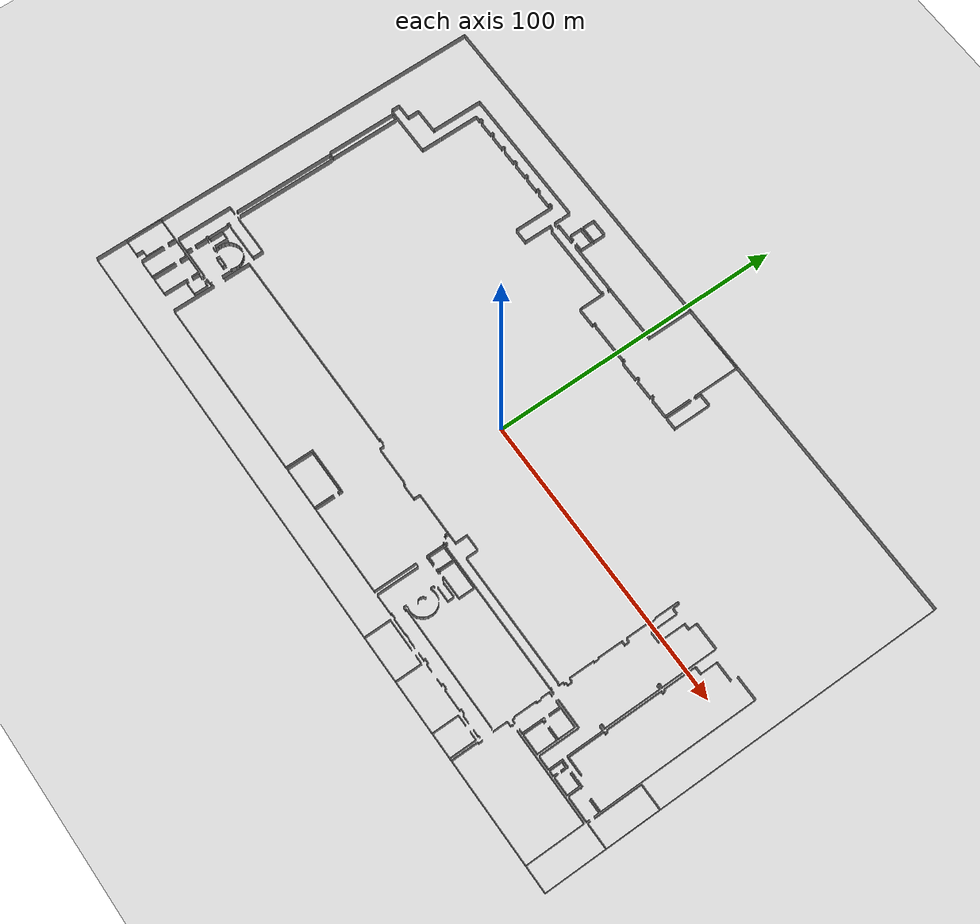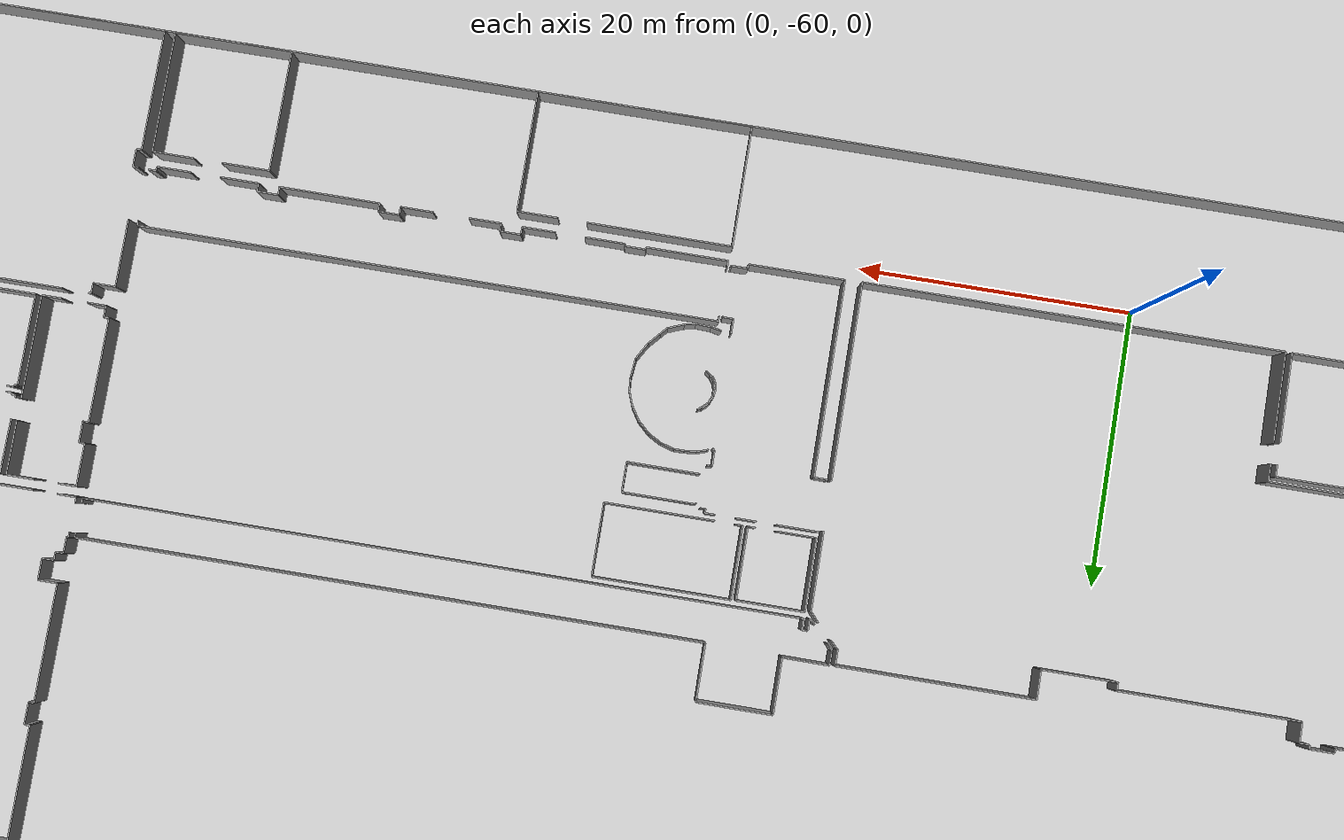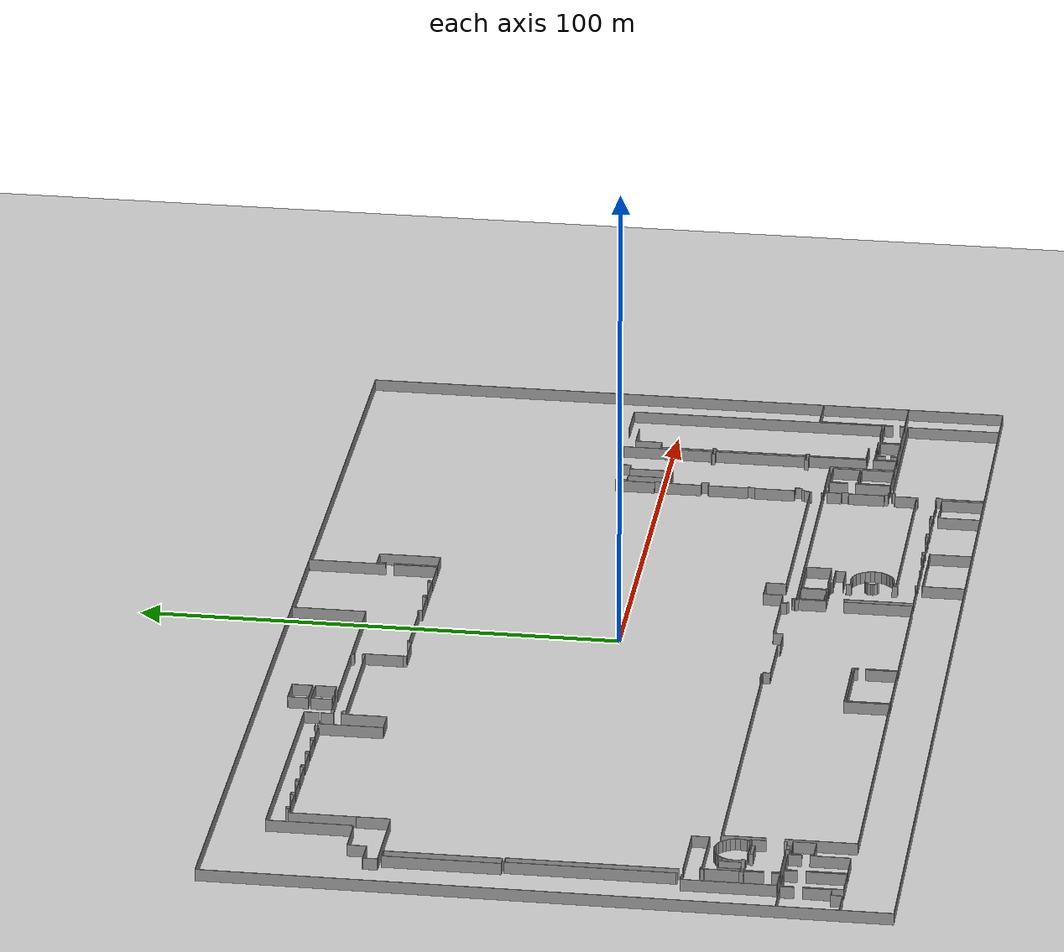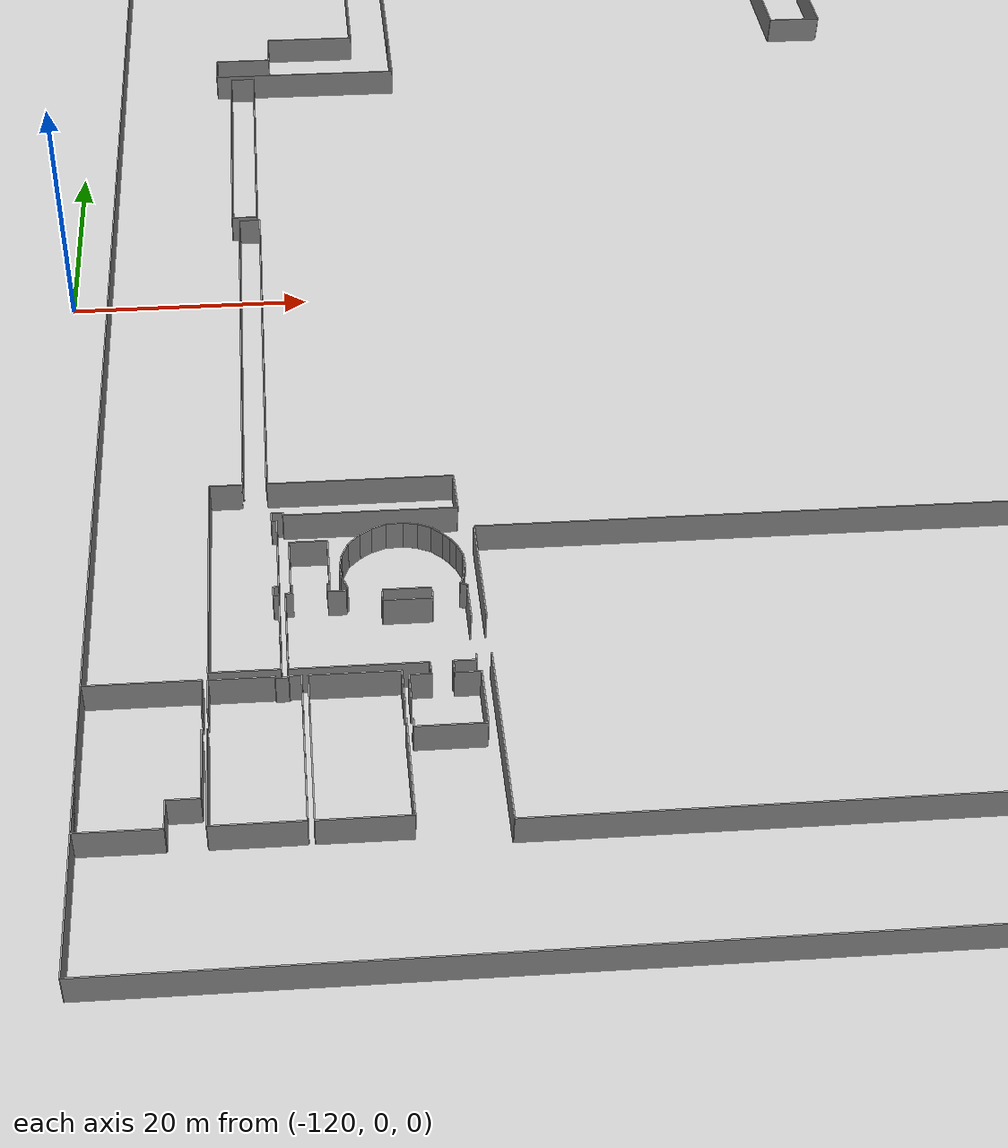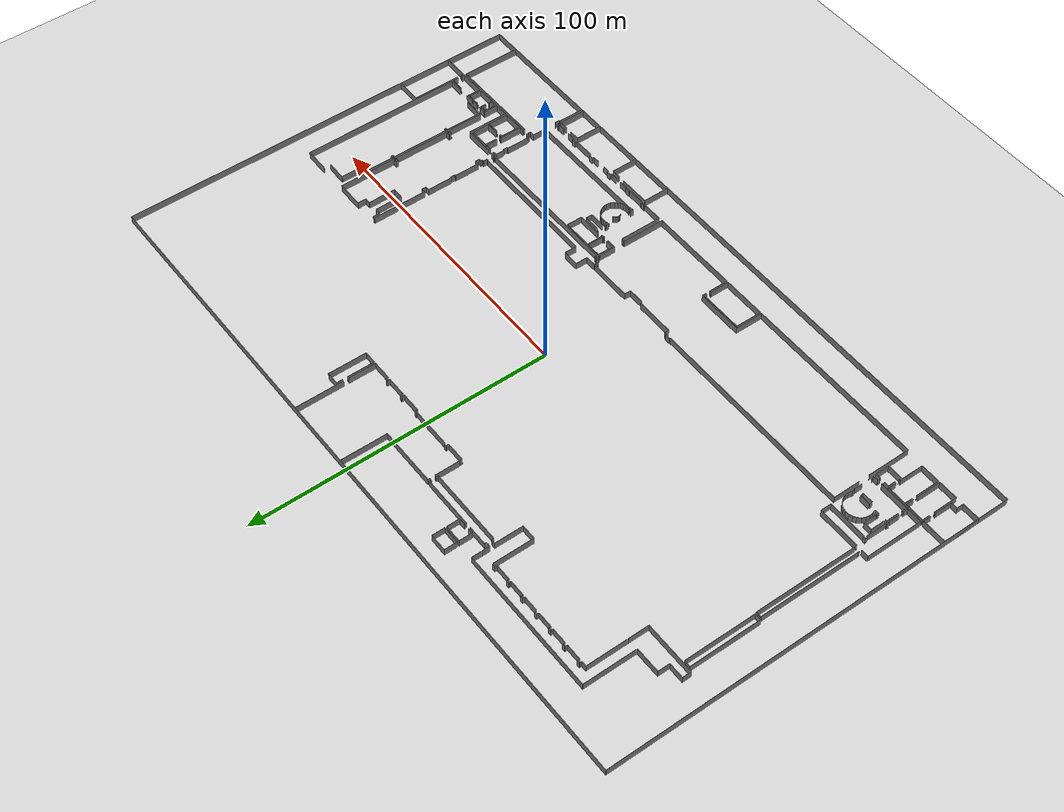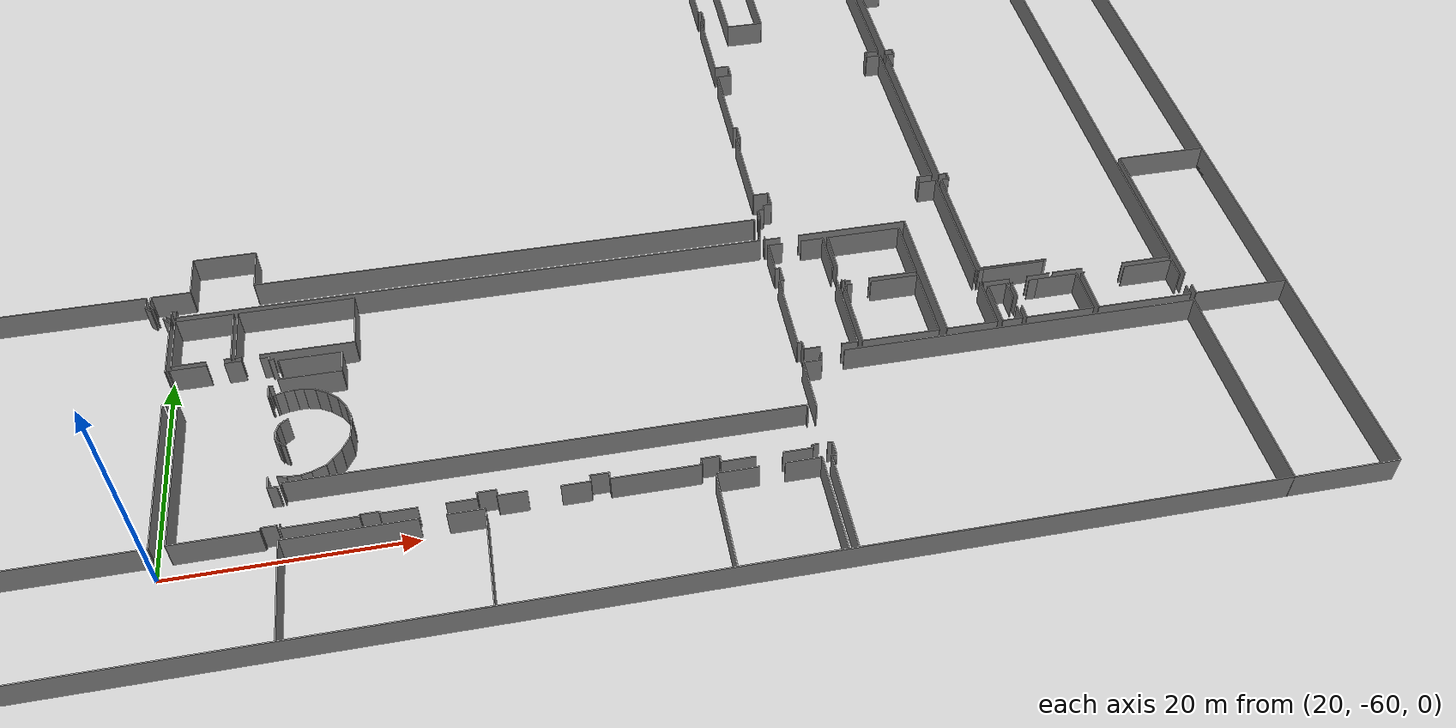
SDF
<sdf version="1.6">
  <world name="default">
    <light name="sun" type="directional">
      <cast_shadows>1</cast_shadows>
      <pose frame="">0 0 10 0 -0 0</pose>
      <diffuse>0.8 0.8 0.8 1</diffuse>
      <specular>0.1 0.1 0.1 1</specular>
      <attenuation>
        <range>1000</range>
        <constant>0.9</constant>
        <linear>0.01</linear>
        <quadratic>0.001</quadratic>
      </attenuation>
      <direction>-0.5 0.5 -1</direction>
    </light>
    <model name="ground_plane">
      <static>1</static>
      <link name="link">
        <collision name="collision">
          <geometry>
            <plane>
              <normal>0 0 1</normal>
              <size>100 100</size>
            </plane>
          </geometry>
          <surface>
            <friction>
              <ode>
                <mu>100</mu>
                <mu2>50</mu2>
              </ode>
              <torsional>
                <ode />
              </torsional>
            </friction>
            <contact>
              <ode />
            </contact>
            <bounce />
          </surface>
          <max_contacts>10</max_contacts>
        </collision>
        <visual name="visual">
          <cast_shadows>0</cast_shadows>
          <geometry>
            <plane>
              <normal>0 0 1</normal>
              <size>100 100</size>
            </plane>
          </geometry>
          <material>
            <script>
              <uri>file://media/materials/scripts/gazebo.material</uri>
              <name>Gazebo/Grey</name>
            </script>
          </material>
        </visual>
        <self_collide>0</self_collide>
        <kinematic>0</kinematic>
        <gravity>1</gravity>
      </link>
    </model>
    <gravity>0 0 -9.8</gravity>
    <magnetic_field>6e-06 2.3e-05 -4.2e-05</magnetic_field>
    <atmosphere type="adiabatic" />
    <physics default="0" name="default_physics" type="ode">
      <max_step_size>0.001</max_step_size>
      <real_time_factor>1</real_time_factor>
      <real_time_update_rate>1000</real_time_update_rate>
    </physics>
    <scene>
      <ambient>0.4 0.4 0.4 1</ambient>
      <background>0.7 0.7 0.7 1</background>
      <shadows>1</shadows>
    </scene>
    <spherical_coordinates>
      <surface_model>EARTH_WGS84</surface_model>
      <latitude_deg>0</latitude_deg>
      <longitude_deg>0</longitude_deg>
      <elevation>0</elevation>
      <heading_deg>0</heading_deg>
    </spherical_coordinates>
  <model name="0510035518_A_40_1_101">
		<static>1</static>
		<link name="Wall_0">
			<collision name="Wall_0_Collision">
				<geometry>
					<box>
						<size>2.94137821531 0.1 2.5</size>
					</box>
				</geometry>
				<pose frame="">1.47068910765 0 1.25 0 0 0</pose>
			</collision>
			<visual name="Wall_0_Visual">
				<pose frame="">1.47068910765 0 1.25 0 0 0</pose>
				<geometry>
					<box>
						<size>2.94137821531 0.1 2.5</size>
					</box>
				</geometry>
				<material>
					<script>
						<uri>file://media/materials/scripts/gazebo.material</uri>
						<name>Gazebo/Grey</name>
					</script>
					<ambient>1 1 1 1</ambient>
				</material>
			</visual>
			<pose frame="">9.22070498571 -34.6560812956 0 0 0 1.57079632679</pose>
		</link>
		<link name="Wall_1">
			<collision name="Wall_1_Collision">
				<geometry>
					<box>
						<size>5.1396633852 0.1 2.5</size>
					</box>
				</geometry>
				<pose frame="">2.5698316926 0 1.25 0 0 0</pose>
			</collision>
			<visual name="Wall_1_Visual">
				<pose frame="">2.5698316926 0 1.25 0 0 0</pose>
				<geometry>
					<box>
						<size>5.1396633852 0.1 2.5</size>
					</box>
				</geometry>
				<material>
					<script>
						<uri>file://media/materials/scripts/gazebo.material</uri>
						<name>Gazebo/Grey</name>
					</script>
					<ambient>1 1 1 1</ambient>
				</material>
			</visual>
			<pose frame="">9.22070498571 -31.7147030803 0 0 0 0.0</pose>
		</link>
		<link name="Wall_2">
			<collision name="Wall_2_Collision">
				<geometry>
					<box>
						<size>3.87958081931 0.1 2.5</size>
					</box>
				</geometry>
				<pose frame="">1.93979040965 0 1.25 0 0 0</pose>
			</collision>
			<visual name="Wall_2_Visual">
				<pose frame="">1.93979040965 0 1.25 0 0 0</pose>
				<geometry>
					<box>
						<size>3.87958081931 0.1 2.5</size>
					</box>
				</geometry>
				<material>
					<script>
						<uri>file://media/materials/scripts/gazebo.material</uri>
						<name>Gazebo/Grey</name>
					</script>
					<ambient>1 1 1 1</ambient>
				</material>
			</visual>
			<pose frame="">14.3603683709 -31.7147030803 0 0 0 1.57079632679</pose>
		</link>
		<link name="Wall_3">
			<collision name="Wall_3_Collision">
				<geometry>
					<box>
						<size>8.40800254049 0.1 2.5</size>
					</box>
				</geometry>
				<pose frame="">4.20400127024 0 1.25 0 0 0</pose>
			</collision>
			<visual name="Wall_3_Visual">
				<pose frame="">4.20400127024 0 1.25 0 0 0</pose>
				<geometry>
					<box>
						<size>8.40800254049 0.1 2.5</size>
					</box>
				</geometry>
				<material>
					<script>
						<uri>file://media/materials/scripts/gazebo.material</uri>
						<name>Gazebo/Grey</name>
					</script>
					<ambient>1 1 1 1</ambient>
				</material>
			</visual>
			<pose frame="">14.3603683709 -27.835122261 0 0 0 0.0</pose>
		</link>
		<link name="Wall_4">
			<collision name="Wall_4_Collision">
				<geometry>
					<box>
						<size>6.82273737695 0.1 2.5</size>
					</box>
				</geometry>
				<pose frame="">3.41136868847 0 1.25 0 0 0</pose>
			</collision>
			<visual name="Wall_4_Visual">
				<pose frame="">3.41136868847 0 1.25 0 0 0</pose>
				<geometry>
					<box>
						<size>6.82273737695 0.1 2.5</size>
					</box>
				</geometry>
				<material>
					<script>
						<uri>file://media/materials/scripts/gazebo.material</uri>
						<name>Gazebo/Grey</name>
					</script>
					<ambient>1 1 1 1</ambient>
				</material>
			</visual>
			<pose frame="">26.5412511909 -27.835122261 0 0 0 -1.57079632679</pose>
		</link>
		<link name="Wall_5">
			<collision name="Wall_5_Collision">
				<geometry>
					<box>
						<size>17.3205462964 0.1 2.5</size>
					</box>
				</geometry>
				<pose frame="">8.66027314822 0 1.25 0 0 0</pose>
			</collision>
			<visual name="Wall_5_Visual">
				<pose frame="">8.66027314822 0 1.25 0 0 0</pose>
				<geometry>
					<box>
						<size>17.3205462964 0.1 2.5</size>
					</box>
				</geometry>
				<material>
					<script>
						<uri>file://media/materials/scripts/gazebo.material</uri>
						<name>Gazebo/Grey</name>
					</script>
					<ambient>1 1 1 1</ambient>
				</material>
			</visual>
			<pose frame="">26.5412511909 -34.657859638 0 0 0 3.14148998117</pose>
		</link>
		<link name="Wall_6">
			<collision name="Wall_6_Collision">
				<geometry>
					<box>
						<size>48.3996189266 0.1 2.5</size>
					</box>
				</geometry>
				<pose frame="">24.1998094633 0 1.25 0 0 0</pose>
			</collision>
			<visual name="Wall_6_Visual">
				<pose frame="">24.1998094633 0 1.25 0 0 0</pose>
				<geometry>
					<box>
						<size>48.3996189266 0.1 2.5</size>
					</box>
				</geometry>
				<material>
					<script>
						<uri>file://media/materials/scripts/gazebo.material</uri>
						<name>Gazebo/Grey</name>
					</script>
					<ambient>1 1 1 1</ambient>
				</material>
			</visual>
			<pose frame="">22.7521117815 -10.2236900603 0 0 0 0.0</pose>
		</link>
		<link name="Wall_7">
			<collision name="Wall_7_Collision">
				<geometry>
					<box>
						<size>3.14639568117 0.1 2.5</size>
					</box>
				</geometry>
				<pose frame="">1.57319784058 0 1.25 0 0 0</pose>
			</collision>
			<visual name="Wall_7_Visual">
				<pose frame="">1.57319784058 0 1.25 0 0 0</pose>
				<geometry>
					<box>
						<size>3.14639568117 0.1 2.5</size>
					</box>
				</geometry>
				<material>
					<script>
						<uri>file://media/materials/scripts/gazebo.material</uri>
						<name>Gazebo/Grey</name>
					</script>
					<ambient>1 1 1 1</ambient>
				</material>
			</visual>
			<pose frame="">71.1517307082 -10.2236900603 0 0 0 -1.57079632679</pose>
		</link>
		<link name="Wall_8">
			<collision name="Wall_8_Collision">
				<geometry>
					<box>
						<size>1.15541441728 0.1 2.5</size>
					</box>
				</geometry>
				<pose frame="">0.577707208638 0 1.25 0 0 0</pose>
			</collision>
			<visual name="Wall_8_Visual">
				<pose frame="">0.577707208638 0 1.25 0 0 0</pose>
				<geometry>
					<box>
						<size>1.15541441728 0.1 2.5</size>
					</box>
				</geometry>
				<material>
					<script>
						<uri>file://media/materials/scripts/gazebo.material</uri>
						<name>Gazebo/Grey</name>
					</script>
					<ambient>1 1 1 1</ambient>
				</material>
			</visual>
			<pose frame="">66.2241981581 -13.3700857415 0 0 0 3.14159265359</pose>
		</link>
		<link name="Wall_9">
			<collision name="Wall_9_Collision">
				<geometry>
					<box>
						<size>0.763925055573 0.1 2.5</size>
					</box>
				</geometry>
				<pose frame="">0.381962527787 0 1.25 0 0 0</pose>
			</collision>
			<visual name="Wall_9_Visual">
				<pose frame="">0.381962527787 0 1.25 0 0 0</pose>
				<geometry>
					<box>
						<size>0.763925055573 0.1 2.5</size>
					</box>
				</geometry>
				<material>
					<script>
						<uri>file://media/materials/scripts/gazebo.material</uri>
						<name>Gazebo/Grey</name>
					</script>
					<ambient>1 1 1 1</ambient>
				</material>
			</visual>
			<pose frame="">65.0687837409 -13.3700857415 0 0 0 -1.57079632679</pose>
		</link>
		<link name="Wall_10">
			<collision name="Wall_10_Collision">
				<geometry>
					<box>
						<size>5.33070816132 0.1 2.5</size>
					</box>
				</geometry>
				<pose frame="">2.66535408066 0 1.25 0 0 0</pose>
			</collision>
			<visual name="Wall_10_Visual">
				<pose frame="">2.66535408066 0 1.25 0 0 0</pose>
				<geometry>
					<box>
						<size>5.33070816132 0.1 2.5</size>
					</box>
				</geometry>
				<material>
					<script>
						<uri>file://media/materials/scripts/gazebo.material</uri>
						<name>Gazebo/Grey</name>
					</script>
					<ambient>1 1 1 1</ambient>
				</material>
			</visual>
			<pose frame="">65.0687837409 -14.1340107971 0 0 0 3.14159265359</pose>
		</link>
		<link name="Wall_11">
			<collision name="Wall_11_Collision">
				<geometry>
					<box>
						<size>0.766973642426 0.1 2.5</size>
					</box>
				</geometry>
				<pose frame="">0.383486821213 0 1.25 0 0 0</pose>
			</collision>
			<visual name="Wall_11_Visual">
				<pose frame="">0.383486821213 0 1.25 0 0 0</pose>
				<geometry>
					<box>
						<size>0.766973642426 0.1 2.5</size>
					</box>
				</geometry>
				<material>
					<script>
						<uri>file://media/materials/scripts/gazebo.material</uri>
						<name>Gazebo/Grey</name>
					</script>
					<ambient>1 1 1 1</ambient>
				</material>
			</visual>
			<pose frame="">59.7380755795 -14.1340107971 0 0 0 1.57079632679</pose>
		</link>
		<link name="Wall_12">
			<collision name="Wall_12_Collision">
				<geometry>
					<box>
						<size>0.988250238171 0.1 2.5</size>
					</box>
				</geometry>
				<pose frame="">0.494125119085 0 1.25 0 0 0</pose>
			</collision>
			<visual name="Wall_12_Visual">
				<pose frame="">0.494125119085 0 1.25 0 0 0</pose>
				<geometry>
					<box>
						<size>0.988250238171 0.1 2.5</size>
					</box>
				</geometry>
				<material>
					<script>
						<uri>file://media/materials/scripts/gazebo.material</uri>
						<name>Gazebo/Grey</name>
					</script>
					<ambient>1 1 1 1</ambient>
				</material>
			</visual>
			<pose frame="">59.7380755795 -13.3670371547 0 0 0 3.14159265359</pose>
		</link>
		<link name="Wall_13">
			<collision name="Wall_13_Collision">
				<geometry>
					<box>
						<size>0.764433153382 0.1 2.5</size>
					</box>
				</geometry>
				<pose frame="">0.382216576691 0 1.25 0 0 0</pose>
			</collision>
			<visual name="Wall_13_Visual">
				<pose frame="">0.382216576691 0 1.25 0 0 0</pose>
				<geometry>
					<box>
						<size>0.764433153382 0.1 2.5</size>
					</box>
				</geometry>
				<material>
					<script>
						<uri>file://media/materials/scripts/gazebo.material</uri>
						<name>Gazebo/Grey</name>
					</script>
					<ambient>1 1 1 1</ambient>
				</material>
			</visual>
			<pose frame="">58.7498253414 -13.3670371547 0 0 0 -1.57079632679</pose>
		</link>
		<link name="Wall_14">
			<collision name="Wall_14_Collision">
				<geometry>
					<box>
						<size>5.11705303271 0.1 2.5</size>
					</box>
				</geometry>
				<pose frame="">2.55852651635 0 1.25 0 0 0</pose>
			</collision>
			<visual name="Wall_14_Visual">
				<pose frame="">2.55852651635 0 1.25 0 0 0</pose>
				<geometry>
					<box>
						<size>5.11705303271 0.1 2.5</size>
					</box>
				</geometry>
				<material>
					<script>
						<uri>file://media/materials/scripts/gazebo.material</uri>
						<name>Gazebo/Grey</name>
					</script>
					<ambient>1 1 1 1</ambient>
				</material>
			</visual>
			<pose frame="">58.7498253414 -14.131470308 0 0 0 3.14159265359</pose>
		</link>
		<link name="Wall_15">
			<collision name="Wall_15_Collision">
				<geometry>
					<box>
						<size>0.769260082566 0.1 2.5</size>
					</box>
				</geometry>
				<pose frame="">0.384630041283 0 1.25 0 0 0</pose>
			</collision>
			<visual name="Wall_15_Visual">
				<pose frame="">0.384630041283 0 1.25 0 0 0</pose>
				<geometry>
					<box>
						<size>0.769260082566 0.1 2.5</size>
					</box>
				</geometry>
				<material>
					<script>
						<uri>file://media/materials/scripts/gazebo.material</uri>
						<name>Gazebo/Grey</name>
					</script>
					<ambient>1 1 1 1</ambient>
				</material>
			</visual>
			<pose frame="">53.6327723087 -14.131470308 0 0 0 1.57079632679</pose>
		</link>
		<link name="Wall_16">
			<collision name="Wall_16_Collision">
				<geometry>
					<box>
						<size>0.992569069546 0.1 2.5</size>
					</box>
				</geometry>
				<pose frame="">0.496284534773 0 1.25 0 0 0</pose>
			</collision>
			<visual name="Wall_16_Visual">
				<pose frame="">0.496284534773 0 1.25 0 0 0</pose>
				<geometry>
					<box>
						<size>0.992569069546 0.1 2.5</size>
					</box>
				</geometry>
				<material>
					<script>
						<uri>file://media/materials/scripts/gazebo.material</uri>
						<name>Gazebo/Grey</name>
					</script>
					<ambient>1 1 1 1</ambient>
				</material>
			</visual>
			<pose frame="">53.6327723087 -13.3622102255 0 0 0 3.14159265359</pose>
		</link>
		<link name="Wall_17">
			<collision name="Wall_17_Collision">
				<geometry>
					<box>
						<size>0.764433153382 0.1 2.5</size>
					</box>
				</geometry>
				<pose frame="">0.382216576691 0 1.25 0 0 0</pose>
			</collision>
			<visual name="Wall_17_Visual">
				<pose frame="">0.382216576691 0 1.25 0 0 0</pose>
				<geometry>
					<box>
						<size>0.764433153382 0.1 2.5</size>
					</box>
				</geometry>
				<material>
					<script>
						<uri>file://media/materials/scripts/gazebo.material</uri>
						<name>Gazebo/Grey</name>
					</script>
					<ambient>1 1 1 1</ambient>
				</material>
			</visual>
			<pose frame="">52.6402032391 -13.3622102255 0 0 0 -1.57079632679</pose>
		</link>
		<link name="Wall_18">
			<collision name="Wall_18_Collision">
				<geometry>
					<box>
						<size>5.0995236583 0.1 2.5</size>
					</box>
				</geometry>
				<pose frame="">2.54976182915 0 1.25 0 0 0</pose>
			</collision>
			<visual name="Wall_18_Visual">
				<pose frame="">2.54976182915 0 1.25 0 0 0</pose>
				<geometry>
					<box>
						<size>5.0995236583 0.1 2.5</size>
					</box>
				</geometry>
				<material>
					<script>
						<uri>file://media/materials/scripts/gazebo.material</uri>
						<name>Gazebo/Grey</name>
					</script>
					<ambient>1 1 1 1</ambient>
				</material>
			</visual>
			<pose frame="">52.6402032391 -14.1266433789 0 0 0 3.14159265359</pose>
		</link>
		<link name="Wall_19">
			<collision name="Wall_19_Collision">
				<geometry>
					<box>
						<size>0.754779295014 0.1 2.5</size>
					</box>
				</geometry>
				<pose frame="">0.377389647507 0 1.25 0 0 0</pose>
			</collision>
			<visual name="Wall_19_Visual">
				<pose frame="">0.377389647507 0 1.25 0 0 0</pose>
				<geometry>
					<box>
						<size>0.754779295014 0.1 2.5</size>
					</box>
				</geometry>
				<material>
					<script>
						<uri>file://media/materials/scripts/gazebo.material</uri>
						<name>Gazebo/Grey</name>
					</script>
					<ambient>1 1 1 1</ambient>
				</material>
			</visual>
			<pose frame="">47.5406795808 -14.1266433789 0 0 0 1.57079632679</pose>
		</link>
		<link name="Wall_20">
			<collision name="Wall_20_Collision">
				<geometry>
					<box>
						<size>1.01162273738 0.1 2.5</size>
					</box>
				</geometry>
				<pose frame="">0.505811368688 0 1.25 0 0 0</pose>
			</collision>
			<visual name="Wall_20_Visual">
				<pose frame="">0.505811368688 0 1.25 0 0 0</pose>
				<geometry>
					<box>
						<size>1.01162273738 0.1 2.5</size>
					</box>
				</geometry>
				<material>
					<script>
						<uri>file://media/materials/scripts/gazebo.material</uri>
						<name>Gazebo/Grey</name>
					</script>
					<ambient>1 1 1 1</ambient>
				</material>
			</visual>
			<pose frame="">47.5406795808 -13.3718640838 0 0 0 3.14159265359</pose>
		</link>
		<link name="Wall_21">
			<collision name="Wall_21_Collision">
				<geometry>
					<box>
						<size>0.754779295014 0.1 2.5</size>
					</box>
				</geometry>
				<pose frame="">0.377389647507 0 1.25 0 0 0</pose>
			</collision>
			<visual name="Wall_21_Visual">
				<pose frame="">0.377389647507 0 1.25 0 0 0</pose>
				<geometry>
					<box>
						<size>0.754779295014 0.1 2.5</size>
					</box>
				</geometry>
				<material>
					<script>
						<uri>file://media/materials/scripts/gazebo.material</uri>
						<name>Gazebo/Grey</name>
					</script>
					<ambient>1 1 1 1</ambient>
				</material>
			</visual>
			<pose frame="">46.5290568434 -13.3718640838 0 0 0 -1.57079632679</pose>
		</link>
		<link name="Wall_22">
			<collision name="Wall_22_Collision">
				<geometry>
					<box>
						<size>5.09672912036 0.1 2.5</size>
					</box>
				</geometry>
				<pose frame="">2.54836456018 0 1.25 0 0 0</pose>
			</collision>
			<visual name="Wall_22_Visual">
				<pose frame="">2.54836456018 0 1.25 0 0 0</pose>
				<geometry>
					<box>
						<size>5.09672912036 0.1 2.5</size>
					</box>
				</geometry>
				<material>
					<script>
						<uri>file://media/materials/scripts/gazebo.material</uri>
						<name>Gazebo/Grey</name>
					</script>
					<ambient>1 1 1 1</ambient>
				</material>
			</visual>
			<pose frame="">46.5290568434 -14.1266433789 0 0 0 3.14159265359</pose>
		</link>
		<link name="Wall_23">
			<collision name="Wall_23_Collision">
				<geometry>
					<box>
						<size>0.772562718323 0.1 2.5</size>
					</box>
				</geometry>
				<pose frame="">0.386281359162 0 1.25 0 0 0</pose>
			</collision>
			<visual name="Wall_23_Visual">
				<pose frame="">0.386281359162 0 1.25 0 0 0</pose>
				<geometry>
					<box>
						<size>0.772562718323 0.1 2.5</size>
					</box>
				</geometry>
				<material>
					<script>
						<uri>file://media/materials/scripts/gazebo.material</uri>
						<name>Gazebo/Grey</name>
					</script>
					<ambient>1 1 1 1</ambient>
				</material>
			</visual>
			<pose frame="">41.4323277231 -14.1266433789 0 0 0 1.57079632679</pose>
		</link>
		<link name="Wall_24">
			<collision name="Wall_24_Collision">
				<geometry>
					<box>
						<size>0.989266433789 0.1 2.5</size>
					</box>
				</geometry>
				<pose frame="">0.494633216894 0 1.25 0 0 0</pose>
			</collision>
			<visual name="Wall_24_Visual">
				<pose frame="">0.494633216894 0 1.25 0 0 0</pose>
				<geometry>
					<box>
						<size>0.989266433789 0.1 2.5</size>
					</box>
				</geometry>
				<material>
					<script>
						<uri>file://media/materials/scripts/gazebo.material</uri>
						<name>Gazebo/Grey</name>
					</script>
					<ambient>1 1 1 1</ambient>
				</material>
			</visual>
			<pose frame="">41.4323277231 -13.3540806605 0 0 0 3.14159265359</pose>
		</link>
		<link name="Wall_25">
			<collision name="Wall_25_Collision">
				<geometry>
					<box>
						<size>0.787043505875 0.1 2.5</size>
					</box>
				</geometry>
				<pose frame="">0.393521752937 0 1.25 0 0 0</pose>
			</collision>
			<visual name="Wall_25_Visual">
				<pose frame="">0.393521752937 0 1.25 0 0 0</pose>
				<geometry>
					<box>
						<size>0.787043505875 0.1 2.5</size>
					</box>
				</geometry>
				<material>
					<script>
						<uri>file://media/materials/scripts/gazebo.material</uri>
						<name>Gazebo/Grey</name>
					</script>
					<ambient>1 1 1 1</ambient>
				</material>
			</visual>
			<pose frame="">40.4430612893 -13.3540806605 0 0 0 -1.57079632679</pose>
		</link>
		<link name="Wall_26">
			<collision name="Wall_26_Collision">
				<geometry>
					<box>
						<size>5.10612892982 0.1 2.5</size>
					</box>
				</geometry>
				<pose frame="">2.55306446491 0 1.25 0 0 0</pose>
			</collision>
			<visual name="Wall_26_Visual">
				<pose frame="">2.55306446491 0 1.25 0 0 0</pose>
				<geometry>
					<box>
						<size>5.10612892982 0.1 2.5</size>
					</box>
				</geometry>
				<material>
					<script>
						<uri>file://media/materials/scripts/gazebo.material</uri>
						<name>Gazebo/Grey</name>
					</script>
					<ambient>1 1 1 1</ambient>
				</material>
			</visual>
			<pose frame="">40.4430612893 -14.1411241664 0 0 0 3.14159265359</pose>
		</link>
		<link name="Wall_27">
			<collision name="Wall_27_Collision">
				<geometry>
					<box>
						<size>0.814734836456 0.1 2.5</size>
					</box>
				</geometry>
				<pose frame="">0.407367418228 0 1.25 0 0 0</pose>
			</collision>
			<visual name="Wall_27_Visual">
				<pose frame="">0.407367418228 0 1.25 0 0 0</pose>
				<geometry>
					<box>
						<size>0.814734836456 0.1 2.5</size>
					</box>
				</geometry>
				<material>
					<script>
						<uri>file://media/materials/scripts/gazebo.material</uri>
						<name>Gazebo/Grey</name>
					</script>
					<ambient>1 1 1 1</ambient>
				</material>
			</visual>
			<pose frame="">35.3369323595 -14.1411241664 0 0 0 1.57079632679</pose>
		</link>
		<link name="Wall_28">
			<collision name="Wall_28_Collision">
				<geometry>
					<box>
						<size>1.00273102572 0.1 2.5</size>
					</box>
				</geometry>
				<pose frame="">0.501365512861 0 1.25 0 0 0</pose>
			</collision>
			<visual name="Wall_28_Visual">
				<pose frame="">0.501365512861 0 1.25 0 0 0</pose>
				<geometry>
					<box>
						<size>1.00273102572 0.1 2.5</size>
					</box>
				</geometry>
				<material>
					<script>
						<uri>file://media/materials/scripts/gazebo.material</uri>
						<name>Gazebo/Grey</name>
					</script>
					<ambient>1 1 1 1</ambient>
				</material>
			</visual>
			<pose frame="">35.3369323595 -13.3263893299 0 0 0 3.14159265359</pose>
		</link>
		<link name="Wall_29">
			<collision name="Wall_29_Collision">
				<geometry>
					<box>
						<size>0.821340107971 0.1 2.5</size>
					</box>
				</geometry>
				<pose frame="">0.410670053985 0 1.25 0 0 0</pose>
			</collision>
			<visual name="Wall_29_Visual">
				<pose frame="">0.410670053985 0 1.25 0 0 0</pose>
				<geometry>
					<box>
						<size>0.821340107971 0.1 2.5</size>
					</box>
				</geometry>
				<material>
					<script>
						<uri>file://media/materials/scripts/gazebo.material</uri>
						<name>Gazebo/Grey</name>
					</script>
					<ambient>1 1 1 1</ambient>
				</material>
			</visual>
			<pose frame="">34.3342013338 -13.3263893299 0 0 0 -1.57079632679</pose>
		</link>
		<link name="Wall_30">
			<collision name="Wall_30_Collision">
				<geometry>
					<box>
						<size>5.1048586853 0.1 2.5</size>
					</box>
				</geometry>
				<pose frame="">2.55242934265 0 1.25 0 0 0</pose>
			</collision>
			<visual name="Wall_30_Visual">
				<pose frame="">2.55242934265 0 1.25 0 0 0</pose>
				<geometry>
					<box>
						<size>5.1048586853 0.1 2.5</size>
					</box>
				</geometry>
				<material>
					<script>
						<uri>file://media/materials/scripts/gazebo.material</uri>
						<name>Gazebo/Grey</name>
					</script>
					<ambient>1 1 1 1</ambient>
				</material>
			</visual>
			<pose frame="">34.3342013338 -14.1477294379 0 0 0 3.14159265359</pose>
		</link>
		<link name="Wall_31">
			<collision name="Wall_31_Collision">
				<geometry>
					<box>
						<size>0.780946332169 0.1 2.5</size>
					</box>
				</geometry>
				<pose frame="">0.390473166084 0 1.25 0 0 0</pose>
			</collision>
			<visual name="Wall_31_Visual">
				<pose frame="">0.390473166084 0 1.25 0 0 0</pose>
				<geometry>
					<box>
						<size>0.780946332169 0.1 2.5</size>
					</box>
				</geometry>
				<material>
					<script>
						<uri>file://media/materials/scripts/gazebo.material</uri>
						<name>Gazebo/Grey</name>
					</script>
					<ambient>1 1 1 1</ambient>
				</material>
			</visual>
			<pose frame="">29.2293426485 -14.1477294379 0 0 0 1.57079632679</pose>
		</link>
		<link name="Wall_32">
			<collision name="Wall_32_Collision">
				<geometry>
					<box>
						<size>0.982915211178 0.1 2.5</size>
					</box>
				</geometry>
				<pose frame="">0.491457605589 0 1.25 0 0 0</pose>
			</collision>
			<visual name="Wall_32_Visual">
				<pose frame="">0.491457605589 0 1.25 0 0 0</pose>
				<geometry>
					<box>
						<size>0.982915211178 0.1 2.5</size>
					</box>
				</geometry>
				<material>
					<script>
						<uri>file://media/materials/scripts/gazebo.material</uri>
						<name>Gazebo/Grey</name>
					</script>
					<ambient>1 1 1 1</ambient>
				</material>
			</visual>
			<pose frame="">29.2293426485 -13.3667831057 0 0 0 3.14159265359</pose>
		</link>
		<link name="Wall_33">
			<collision name="Wall_33_Collision">
				<geometry>
					<box>
						<size>0.772054620514 0.1 2.5</size>
					</box>
				</geometry>
				<pose frame="">0.386027310257 0 1.25 0 0 0</pose>
			</collision>
			<visual name="Wall_33_Visual">
				<pose frame="">0.386027310257 0 1.25 0 0 0</pose>
				<geometry>
					<box>
						<size>0.772054620514 0.1 2.5</size>
					</box>
				</geometry>
				<material>
					<script>
						<uri>file://media/materials/scripts/gazebo.material</uri>
						<name>Gazebo/Grey</name>
					</script>
					<ambient>1 1 1 1</ambient>
				</material>
			</visual>
			<pose frame="">28.2464274373 -13.3667831057 0 0 0 -1.57079632679</pose>
		</link>
		<link name="Wall_34">
			<collision name="Wall_34_Collision">
				<geometry>
					<box>
						<size>1.70568434424 0.1 2.5</size>
					</box>
				</geometry>
				<pose frame="">0.852842172118 0 1.25 0 0 0</pose>
			</collision>
			<visual name="Wall_34_Visual">
				<pose frame="">0.852842172118 0 1.25 0 0 0</pose>
				<geometry>
					<box>
						<size>1.70568434424 0.1 2.5</size>
					</box>
				</geometry>
				<material>
					<script>
						<uri>file://media/materials/scripts/gazebo.material</uri>
						<name>Gazebo/Grey</name>
					</script>
					<ambient>1 1 1 1</ambient>
				</material>
			</visual>
			<pose frame="">28.2464274373 -14.1388377263 0 0 0 3.14159265359</pose>
		</link>
		<link name="Wall_35">
			<collision name="Wall_35_Collision">
				<geometry>
					<box>
						<size>13.4130200064 0.1 2.5</size>
					</box>
				</geometry>
				<pose frame="">6.70651000318 0 1.25 0 0 0</pose>
			</collision>
			<visual name="Wall_35_Visual">
				<pose frame="">6.70651000318 0 1.25 0 0 0</pose>
				<geometry>
					<box>
						<size>13.4130200064 0.1 2.5</size>
					</box>
				</geometry>
				<material>
					<script>
						<uri>file://media/materials/scripts/gazebo.material</uri>
						<name>Gazebo/Grey</name>
					</script>
					<ambient>1 1 1 1</ambient>
				</material>
			</visual>
			<pose frame="">26.540743093 -14.1388377263 0 0 0 -1.57079632679</pose>
		</link>
		<link name="Wall_36">
			<collision name="Wall_36_Collision">
				<geometry>
					<box>
						<size>17.3281690299 0.1 2.5</size>
					</box>
				</geometry>
				<pose frame="">8.66408451495 0 1.25 0 0 0</pose>
			</collision>
			<visual name="Wall_36_Visual">
				<pose frame="">8.66408451495 0 1.25 0 0 0</pose>
				<geometry>
					<box>
						<size>17.3281690299 0.1 2.5</size>
					</box>
				</geometry>
				<material>
					<script>
						<uri>file://media/materials/scripts/gazebo.material</uri>
						<name>Gazebo/Grey</name>
					</script>
					<ambient>1 1 1 1</ambient>
				</material>
			</visual>
			<pose frame="">22.7589711019 -27.5518577326 0 0 0 1.57119217477</pose>
		</link>
		<link name="Wall_37">
			<collision name="Wall_37_Collision">
				<geometry>
					<box>
						<size>13.4506192442 0.1 2.5</size>
					</box>
				</geometry>
				<pose frame="">6.7253096221 0 1.25 0 0 0</pose>
			</collision>
			<visual name="Wall_37_Visual">
				<pose frame="">6.7253096221 0 1.25 0 0 0</pose>
				<geometry>
					<box>
						<size>13.4506192442 0.1 2.5</size>
					</box>
				</geometry>
				<material>
					<script>
						<uri>file://media/materials/scripts/gazebo.material</uri>
						<name>Gazebo/Grey</name>
					</script>
					<ambient>1 1 1 1</ambient>
				</material>
			</visual>
			<pose frame="">66.2282629406 -27.1491902191 0 0 0 1.57079632679</pose>
		</link>
		<link name="Wall_38">
			<collision name="Wall_38_Collision">
				<geometry>
					<box>
						<size>2.49348999682 0.1 2.5</size>
					</box>
				</geometry>
				<pose frame="">1.24674499841 0 1.25 0 0 0</pose>
			</collision>
			<visual name="Wall_38_Visual">
				<pose frame="">1.24674499841 0 1.25 0 0 0</pose>
				<geometry>
					<box>
						<size>2.49348999682 0.1 2.5</size>
					</box>
				</geometry>
				<material>
					<script>
						<uri>file://media/materials/scripts/gazebo.material</uri>
						<name>Gazebo/Grey</name>
					</script>
					<ambient>1 1 1 1</ambient>
				</material>
			</visual>
			<pose frame="">71.1578278819 -13.6985709749 0 0 0 -1.57079632679</pose>
		</link>
		<link name="Wall_39">
			<collision name="Wall_39_Collision">
				<geometry>
					<box>
						<size>0.944807875516 0.1 2.5</size>
					</box>
				</geometry>
				<pose frame="">0.472403937758 0 1.25 0 0 0</pose>
			</collision>
			<visual name="Wall_39_Visual">
				<pose frame="">0.472403937758 0 1.25 0 0 0</pose>
				<geometry>
					<box>
						<size>0.944807875516 0.1 2.5</size>
					</box>
				</geometry>
				<material>
					<script>
						<uri>file://media/materials/scripts/gazebo.material</uri>
						<name>Gazebo/Grey</name>
					</script>
					<ambient>1 1 1 1</ambient>
				</material>
			</visual>
			<pose frame="">71.1578278819 -16.1920609717 0 0 0 0.0</pose>
		</link>
		<link name="Wall_40">
			<collision name="Wall_40_Collision">
				<geometry>
					<box>
						<size>0.932867577009 0.1 2.5</size>
					</box>
				</geometry>
				<pose frame="">0.466433788504 0 1.25 0 0 0</pose>
			</collision>
			<visual name="Wall_40_Visual">
				<pose frame="">0.466433788504 0 1.25 0 0 0</pose>
				<geometry>
					<box>
						<size>0.932867577009 0.1 2.5</size>
					</box>
				</geometry>
				<material>
					<script>
						<uri>file://media/materials/scripts/gazebo.material</uri>
						<name>Gazebo/Grey</name>
					</script>
					<ambient>1 1 1 1</ambient>
				</material>
			</visual>
			<pose frame="">72.1026357574 -17.7730073039 0 0 0 3.14159265359</pose>
		</link>
		<link name="Wall_41">
			<collision name="Wall_41_Collision">
				<geometry>
					<box>
						<size>9.38888536043 0.1 2.5</size>
					</box>
				</geometry>
				<pose frame="">4.69444268022 0 1.25 0 0 0</pose>
			</collision>
			<visual name="Wall_41_Visual">
				<pose frame="">4.69444268022 0 1.25 0 0 0</pose>
				<geometry>
					<box>
						<size>9.38888536043 0.1 2.5</size>
					</box>
				</geometry>
				<material>
					<script>
						<uri>file://media/materials/scripts/gazebo.material</uri>
						<name>Gazebo/Grey</name>
					</script>
					<ambient>1 1 1 1</ambient>
				</material>
			</visual>
			<pose frame="">71.1697681804 -17.7730073039 0 0 0 -1.57079632679</pose>
		</link>
		<link name="Wall_42">
			<collision name="Wall_42_Collision">
				<geometry>
					<box>
						<size>4.94152156594 0.1 2.5</size>
					</box>
				</geometry>
				<pose frame="">2.47076078297 0 1.25 0 0 0</pose>
			</collision>
			<visual name="Wall_42_Visual">
				<pose frame="">2.47076078297 0 1.25 0 0 0</pose>
				<geometry>
					<box>
						<size>4.94152156594 0.1 2.5</size>
					</box>
				</geometry>
				<material>
					<script>
						<uri>file://media/materials/scripts/gazebo.material</uri>
						<name>Gazebo/Grey</name>
					</script>
					<ambient>1 1 1 1</ambient>
				</material>
			</visual>
			<pose frame="">71.1697681804 -27.1618926643 0 0 0 3.13902209733</pose>
		</link>
		<link name="Wall_43">
			<collision name="Wall_43_Collision">
				<geometry>
					<box>
						<size>6.75439822166 0.1 2.5</size>
					</box>
				</geometry>
				<pose frame="">3.37719911083 0 1.25 0 0 0</pose>
			</collision>
			<visual name="Wall_43_Visual">
				<pose frame="">3.37719911083 0 1.25 0 0 0</pose>
				<geometry>
					<box>
						<size>6.75439822166 0.1 2.5</size>
					</box>
				</geometry>
				<material>
					<script>
						<uri>file://media/materials/scripts/gazebo.material</uri>
						<name>Gazebo/Grey</name>
					</script>
					<ambient>1 1 1 1</ambient>
				</material>
			</visual>
			<pose frame="">72.6396951413 -15.5472848523 0 0 0 0.0</pose>
		</link>
		<link name="Wall_44">
			<collision name="Wall_44_Collision">
				<geometry>
					<box>
						<size>17.645220705 0.1 2.5</size>
					</box>
				</geometry>
				<pose frame="">8.82261035249 0 1.25 0 0 0</pose>
			</collision>
			<visual name="Wall_44_Visual">
				<pose frame="">8.82261035249 0 1.25 0 0 0</pose>
				<geometry>
					<box>
						<size>17.645220705 0.1 2.5</size>
					</box>
				</geometry>
				<material>
					<script>
						<uri>file://media/materials/scripts/gazebo.material</uri>
						<name>Gazebo/Grey</name>
					</script>
					<ambient>1 1 1 1</ambient>
				</material>
			</visual>
			<pose frame="">80.9636074944 -15.5472848523 0 0 0 0.0</pose>
		</link>
		<link name="Wall_45">
			<collision name="Wall_45_Collision">
				<geometry>
					<box>
						<size>0.773832962845 0.1 2.5</size>
					</box>
				</geometry>
				<pose frame="">0.386916481423 0 1.25 0 0 0</pose>
			</collision>
			<visual name="Wall_45_Visual">
				<pose frame="">0.386916481423 0 1.25 0 0 0</pose>
				<geometry>
					<box>
						<size>0.773832962845 0.1 2.5</size>
					</box>
				</geometry>
				<material>
					<script>
						<uri>file://media/materials/scripts/gazebo.material</uri>
						<name>Gazebo/Grey</name>
					</script>
					<ambient>1 1 1 1</ambient>
				</material>
			</visual>
			<pose frame="">98.6088281994 -15.5472848523 0 0 0 -1.57079632679</pose>
		</link>
		<link name="Wall_46">
			<collision name="Wall_46_Collision">
				<geometry>
					<box>
						<size>0.65900285805 0.1 2.5</size>
					</box>
				</geometry>
				<pose frame="">0.329501429025 0 1.25 0 0 0</pose>
			</collision>
			<visual name="Wall_46_Visual">
				<pose frame="">0.329501429025 0 1.25 0 0 0</pose>
				<geometry>
					<box>
						<size>0.65900285805 0.1 2.5</size>
					</box>
				</geometry>
				<material>
					<script>
						<uri>file://media/materials/scripts/gazebo.material</uri>
						<name>Gazebo/Grey</name>
					</script>
					<ambient>1 1 1 1</ambient>
				</material>
			</visual>
			<pose frame="">98.6088281994 -17.8476976818 0 0 0 -1.57079632679</pose>
		</link>
		<link name="Wall_47">
			<collision name="Wall_47_Collision">
				<geometry>
					<box>
						<size>25.977516672 0.1 2.5</size>
					</box>
				</geometry>
				<pose frame="">12.988758336 0 1.25 0 0 0</pose>
			</collision>
			<visual name="Wall_47_Visual">
				<pose frame="">12.988758336 0 1.25 0 0 0</pose>
				<geometry>
					<box>
						<size>25.977516672 0.1 2.5</size>
					</box>
				</geometry>
				<material>
					<script>
						<uri>file://media/materials/scripts/gazebo.material</uri>
						<name>Gazebo/Grey</name>
					</script>
					<ambient>1 1 1 1</ambient>
				</material>
			</visual>
			<pose frame="">98.6088281994 -18.5067005399 0 0 0 3.14159265359</pose>
		</link>
		<link name="Wall_48">
			<collision name="Wall_48_Collision">
				<geometry>
					<box>
						<size>0.667386471896 0.1 2.5</size>
					</box>
				</geometry>
				<pose frame="">0.333693235948 0 1.25 0 0 0</pose>
			</collision>
			<visual name="Wall_48_Visual">
				<pose frame="">0.333693235948 0 1.25 0 0 0</pose>
				<geometry>
					<box>
						<size>0.667386471896 0.1 2.5</size>
					</box>
				</geometry>
				<material>
					<script>
						<uri>file://media/materials/scripts/gazebo.material</uri>
						<name>Gazebo/Grey</name>
					</script>
					<ambient>1 1 1 1</ambient>
				</material>
			</visual>
			<pose frame="">72.6313115275 -18.5067005399 0 0 0 1.57079632679</pose>
		</link>
		<link name="Wall_49">
			<collision name="Wall_49_Collision">
				<geometry>
					<box>
						<size>0.639496048185 0.1 2.5</size>
					</box>
				</geometry>
				<pose frame="">0.319748024092 0 1.25 0 0 0</pose>
			</collision>
			<visual name="Wall_49_Visual">
				<pose frame="">0.319748024092 0 1.25 0 0 0</pose>
				<geometry>
					<box>
						<size>0.639496048185 0.1 2.5</size>
					</box>
				</geometry>
				<material>
					<script>
						<uri>file://media/materials/scripts/gazebo.material</uri>
						<name>Gazebo/Grey</name>
					</script>
					<ambient>1 1 1 1</ambient>
				</material>
			</visual>
			<pose frame="">72.6313115275 -16.1867259447 0 0 0 1.5576862317</pose>
		</link>
		<link name="Wall_50">
			<collision name="Wall_50_Collision">
				<geometry>
					<box>
						<size>4.31832327723 0.1 2.5</size>
					</box>
				</geometry>
				<pose frame="">2.15916163862 0 1.25 0 0 0</pose>
			</collision>
			<visual name="Wall_50_Visual">
				<pose frame="">2.15916163862 0 1.25 0 0 0</pose>
				<geometry>
					<box>
						<size>4.31832327723 0.1 2.5</size>
					</box>
				</geometry>
				<material>
					<script>
						<uri>file://media/materials/scripts/gazebo.material</uri>
						<name>Gazebo/Grey</name>
					</script>
					<ambient>1 1 1 1</ambient>
				</material>
			</visual>
			<pose frame="">77.4905049222 -14.939599873 0 0 0 1.57079632679</pose>
		</link>
		<link name="Wall_51">
			<collision name="Wall_51_Collision">
				<geometry>
					<box>
						<size>5.7841854557 0.1 2.5</size>
					</box>
				</geometry>
				<pose frame="">2.89209272785 0 1.25 0 0 0</pose>
			</collision>
			<visual name="Wall_51_Visual">
				<pose frame="">2.89209272785 0 1.25 0 0 0</pose>
				<geometry>
					<box>
						<size>5.7841854557 0.1 2.5</size>
					</box>
				</geometry>
				<material>
					<script>
						<uri>file://media/materials/scripts/gazebo.material</uri>
						<name>Gazebo/Grey</name>
					</script>
					<ambient>1 1 1 1</ambient>
				</material>
			</visual>
			<pose frame="">77.4905049222 -10.6212765957 0 0 0 0.0</pose>
		</link>
		<link name="Wall_52">
			<collision name="Wall_52_Collision">
				<geometry>
					<box>
						<size>4.31832327723 0.1 2.5</size>
					</box>
				</geometry>
				<pose frame="">2.15916163862 0 1.25 0 0 0</pose>
			</collision>
			<visual name="Wall_52_Visual">
				<pose frame="">2.15916163862 0 1.25 0 0 0</pose>
				<geometry>
					<box>
						<size>4.31832327723 0.1 2.5</size>
					</box>
				</geometry>
				<material>
					<script>
						<uri>file://media/materials/scripts/gazebo.material</uri>
						<name>Gazebo/Grey</name>
					</script>
					<ambient>1 1 1 1</ambient>
				</material>
			</visual>
			<pose frame="">83.2746903779 -10.6212765957 0 0 0 -1.57079632679</pose>
		</link>
		<link name="Wall_53">
			<collision name="Wall_53_Collision">
				<geometry>
					<box>
						<size>2.33852016513 0.1 2.5</size>
					</box>
				</geometry>
				<pose frame="">1.16926008257 0 1.25 0 0 0</pose>
			</collision>
			<visual name="Wall_53_Visual">
				<pose frame="">1.16926008257 0 1.25 0 0 0</pose>
				<geometry>
					<box>
						<size>2.33852016513 0.1 2.5</size>
					</box>
				</geometry>
				<material>
					<script>
						<uri>file://media/materials/scripts/gazebo.material</uri>
						<name>Gazebo/Grey</name>
					</script>
					<ambient>1 1 1 1</ambient>
				</material>
			</visual>
			<pose frame="">83.2746903779 -14.939599873 0 0 0 3.14159265359</pose>
		</link>
		<link name="Wall_54">
			<collision name="Wall_54_Collision">
				<geometry>
					<box>
						<size>1.84236265481 0.1 2.5</size>
					</box>
				</geometry>
				<pose frame="">0.921181327406 0 1.25 0 0 0</pose>
			</collision>
			<visual name="Wall_54_Visual">
				<pose frame="">0.921181327406 0 1.25 0 0 0</pose>
				<geometry>
					<box>
						<size>1.84236265481 0.1 2.5</size>
					</box>
				</geometry>
				<material>
					<script>
						<uri>file://media/materials/scripts/gazebo.material</uri>
						<name>Gazebo/Grey</name>
					</script>
					<ambient>1 1 1 1</ambient>
				</material>
			</visual>
			<pose frame="">79.332867577 -14.939599873 0 0 0 3.14159265359</pose>
		</link>
		<link name="Wall_55">
			<collision name="Wall_55_Collision">
				<geometry>
					<box>
						<size>4.2245792315 0.1 2.5</size>
					</box>
				</geometry>
				<pose frame="">2.11228961575 0 1.25 0 0 0</pose>
			</collision>
			<visual name="Wall_55_Visual">
				<pose frame="">2.11228961575 0 1.25 0 0 0</pose>
				<geometry>
					<box>
						<size>4.2245792315 0.1 2.5</size>
					</box>
				</geometry>
				<material>
					<script>
						<uri>file://media/materials/scripts/gazebo.material</uri>
						<name>Gazebo/Grey</name>
					</script>
					<ambient>1 1 1 1</ambient>
				</material>
			</visual>
			<pose frame="">77.488472531 -10.0669418863 0 0 0 1.57079632679</pose>
		</link>
		<link name="Wall_56">
			<collision name="Wall_56_Collision">
				<geometry>
					<box>
						<size>5.78291521118 0.1 2.5</size>
					</box>
				</geometry>
				<pose frame="">2.89145760559 0 1.25 0 0 0</pose>
			</collision>
			<visual name="Wall_56_Visual">
				<pose frame="">2.89145760559 0 1.25 0 0 0</pose>
				<geometry>
					<box>
						<size>5.78291521118 0.1 2.5</size>
					</box>
				</geometry>
				<material>
					<script>
						<uri>file://media/materials/scripts/gazebo.material</uri>
						<name>Gazebo/Grey</name>
					</script>
					<ambient>1 1 1 1</ambient>
				</material>
			</visual>
			<pose frame="">77.488472531 -5.84236265481 0 0 0 0.0</pose>
		</link>
		<link name="Wall_57">
			<collision name="Wall_57_Collision">
				<geometry>
					<box>
						<size>4.24490314386 0.1 2.5</size>
					</box>
				</geometry>
				<pose frame="">2.12245157193 0 1.25 0 0 0</pose>
			</collision>
			<visual name="Wall_57_Visual">
				<pose frame="">2.12245157193 0 1.25 0 0 0</pose>
				<geometry>
					<box>
						<size>4.24490314386 0.1 2.5</size>
					</box>
				</geometry>
				<material>
					<script>
						<uri>file://media/materials/scripts/gazebo.material</uri>
						<name>Gazebo/Grey</name>
					</script>
					<ambient>1 1 1 1</ambient>
				</material>
			</visual>
			<pose frame="">83.2713877421 -5.84236265481 0 0 0 -1.57079632679</pose>
		</link>
		<link name="Wall_58">
			<collision name="Wall_58_Collision">
				<geometry>
					<box>
						<size>5.78295092501 0.1 2.5</size>
					</box>
				</geometry>
				<pose frame="">2.89147546251 0 1.25 0 0 0</pose>
			</collision>
			<visual name="Wall_58_Visual">
				<pose frame="">2.89147546251 0 1.25 0 0 0</pose>
				<geometry>
					<box>
						<size>5.78295092501 0.1 2.5</size>
					</box>
				</geometry>
				<material>
					<script>
						<uri>file://media/materials/scripts/gazebo.material</uri>
						<name>Gazebo/Grey</name>
					</script>
					<ambient>1 1 1 1</ambient>
				</material>
			</visual>
			<pose frame="">83.2713877421 -10.0872657987 0 0 0 3.13807819281</pose>
		</link>
		<link name="Wall_59">
			<collision name="Wall_59_Collision">
				<geometry>
					<box>
						<size>0.837599237853 0.1 2.5</size>
					</box>
				</geometry>
				<pose frame="">0.418799618927 0 1.25 0 0 0</pose>
			</collision>
			<visual name="Wall_59_Visual">
				<pose frame="">0.418799618927 0 1.25 0 0 0</pose>
				<geometry>
					<box>
						<size>0.837599237853 0.1 2.5</size>
					</box>
				</geometry>
				<material>
					<script>
						<uri>file://media/materials/scripts/gazebo.material</uri>
						<name>Gazebo/Grey</name>
					</script>
					<ambient>1 1 1 1</ambient>
				</material>
			</visual>
			<pose frame="">99.2127024452 -27.0318196253 0 0 0 1.57079632679</pose>
		</link>
		<link name="Wall_60">
			<collision name="Wall_60_Collision">
				<geometry>
					<box>
						<size>0.0721498888536 0.1 2.5</size>
					</box>
				</geometry>
				<pose frame="">0.0360749444268 0 1.25 0 0 0</pose>
			</collision>
			<visual name="Wall_60_Visual">
				<pose frame="">0.0360749444268 0 1.25 0 0 0</pose>
				<geometry>
					<box>
						<size>0.0721498888536 0.1 2.5</size>
					</box>
				</geometry>
				<material>
					<script>
						<uri>file://media/materials/scripts/gazebo.material</uri>
						<name>Gazebo/Grey</name>
					</script>
					<ambient>1 1 1 1</ambient>
				</material>
			</visual>
			<pose frame="">99.2127024452 -26.1942203874 0 0 0 3.14159265359</pose>
		</link>
		<link name="Wall_61">
			<collision name="Wall_61_Collision">
				<geometry>
					<box>
						<size>8.33000952683 0.1 2.5</size>
					</box>
				</geometry>
				<pose frame="">4.16500476342 0 1.25 0 0 0</pose>
			</collision>
			<visual name="Wall_61_Visual">
				<pose frame="">4.16500476342 0 1.25 0 0 0</pose>
				<geometry>
					<box>
						<size>8.33000952683 0.1 2.5</size>
					</box>
				</geometry>
				<material>
					<script>
						<uri>file://media/materials/scripts/gazebo.material</uri>
						<name>Gazebo/Grey</name>
					</script>
					<ambient>1 1 1 1</ambient>
				</material>
			</visual>
			<pose frame="">99.1405525564 -26.1942203874 0 0 0 1.57079632679</pose>
		</link>
		<link name="Wall_62">
			<collision name="Wall_62_Collision">
				<geometry>
					<box>
						<size>0.722006986345 0.1 2.5</size>
					</box>
				</geometry>
				<pose frame="">0.361003493172 0 1.25 0 0 0</pose>
			</collision>
			<visual name="Wall_62_Visual">
				<pose frame="">0.361003493172 0 1.25 0 0 0</pose>
				<geometry>
					<box>
						<size>0.722006986345 0.1 2.5</size>
					</box>
				</geometry>
				<material>
					<script>
						<uri>file://media/materials/scripts/gazebo.material</uri>
						<name>Gazebo/Grey</name>
					</script>
					<ambient>1 1 1 1</ambient>
				</material>
			</visual>
			<pose frame="">99.1405525564 -16.2667513496 0 0 0 1.57079632679</pose>
		</link>
		<link name="Wall_63">
			<collision name="Wall_63_Collision">
				<geometry>
					<box>
						<size>19.707589711 0.1 2.5</size>
					</box>
				</geometry>
				<pose frame="">9.85379485551 0 1.25 0 0 0</pose>
			</collision>
			<visual name="Wall_63_Visual">
				<pose frame="">9.85379485551 0 1.25 0 0 0</pose>
				<geometry>
					<box>
						<size>19.707589711 0.1 2.5</size>
					</box>
				</geometry>
				<material>
					<script>
						<uri>file://media/materials/scripts/gazebo.material</uri>
						<name>Gazebo/Grey</name>
					</script>
					<ambient>1 1 1 1</ambient>
				</material>
			</visual>
			<pose frame="">99.1405525564 -15.5447443633 0 0 0 0.0</pose>
		</link>
		<link name="Wall_64">
			<collision name="Wall_64_Collision">
				<geometry>
					<box>
						<size>15.5447443633 0.1 2.5</size>
					</box>
				</geometry>
				<pose frame="">7.77237218164 0 1.25 0 0 0</pose>
			</collision>
			<visual name="Wall_64_Visual">
				<pose frame="">7.77237218164 0 1.25 0 0 0</pose>
				<geometry>
					<box>
						<size>15.5447443633 0.1 2.5</size>
					</box>
				</geometry>
				<material>
					<script>
						<uri>file://media/materials/scripts/gazebo.material</uri>
						<name>Gazebo/Grey</name>
					</script>
					<ambient>1 1 1 1</ambient>
				</material>
			</visual>
			<pose frame="">118.848142267 -15.5447443633 0 0 0 1.57079632679</pose>
		</link>
		<link name="Wall_65">
			<collision name="Wall_65_Collision">
				<geometry>
					<box>
						<size>23.0084471261 0.1 2.5</size>
					</box>
				</geometry>
				<pose frame="">11.504223563 0 1.25 0 0 0</pose>
			</collision>
			<visual name="Wall_65_Visual">
				<pose frame="">11.504223563 0 1.25 0 0 0</pose>
				<geometry>
					<box>
						<size>23.0084471261 0.1 2.5</size>
					</box>
				</geometry>
				<material>
					<script>
						<uri>file://media/materials/scripts/gazebo.material</uri>
						<name>Gazebo/Grey</name>
					</script>
					<ambient>1 1 1 1</ambient>
				</material>
			</visual>
			<pose frame="">118.848142267 -0.0 0 0 0 0.0</pose>
		</link>
		<link name="Wall_66">
			<collision name="Wall_66_Collision">
				<geometry>
					<box>
						<size>16.2210225468 0.1 2.5</size>
					</box>
				</geometry>
				<pose frame="">8.11051127342 0 1.25 0 0 0</pose>
			</collision>
			<visual name="Wall_66_Visual">
				<pose frame="">8.11051127342 0 1.25 0 0 0</pose>
				<geometry>
					<box>
						<size>16.2210225468 0.1 2.5</size>
					</box>
				</geometry>
				<material>
					<script>
						<uri>file://media/materials/scripts/gazebo.material</uri>
						<name>Gazebo/Grey</name>
					</script>
					<ambient>1 1 1 1</ambient>
				</material>
			</visual>
			<pose frame="">141.856589393 -0.0 0 0 0 -1.57079632679</pose>
		</link>
		<link name="Wall_67">
			<collision name="Wall_67_Collision">
				<geometry>
					<box>
						<size>9.12848523341 0.1 2.5</size>
					</box>
				</geometry>
				<pose frame="">4.5642426167 0 1.25 0 0 0</pose>
			</collision>
			<visual name="Wall_67_Visual">
				<pose frame="">4.5642426167 0 1.25 0 0 0</pose>
				<geometry>
					<box>
						<size>9.12848523341 0.1 2.5</size>
					</box>
				</geometry>
				<material>
					<script>
						<uri>file://media/materials/scripts/gazebo.material</uri>
						<name>Gazebo/Grey</name>
					</script>
					<ambient>1 1 1 1</ambient>
				</material>
			</visual>
			<pose frame="">141.856589393 -17.9122261035 0 0 0 -1.57079632679</pose>
		</link>
		<link name="Wall_68">
			<collision name="Wall_68_Collision">
				<geometry>
					<box>
						<size>6.59663385202 0.1 2.5</size>
					</box>
				</geometry>
				<pose frame="">3.29831692601 0 1.25 0 0 0</pose>
			</collision>
			<visual name="Wall_68_Visual">
				<pose frame="">3.29831692601 0 1.25 0 0 0</pose>
				<geometry>
					<box>
						<size>6.59663385202 0.1 2.5</size>
					</box>
				</geometry>
				<material>
					<script>
						<uri>file://media/materials/scripts/gazebo.material</uri>
						<name>Gazebo/Grey</name>
					</script>
					<ambient>1 1 1 1</ambient>
				</material>
			</visual>
			<pose frame="">141.856589393 -27.0407113369 0 0 0 3.14159265359</pose>
		</link>
		<link name="Wall_69">
			<collision name="Wall_69_Collision">
				<geometry>
					<box>
						<size>0.911527469038 0.1 2.5</size>
					</box>
				</geometry>
				<pose frame="">0.455763734519 0 1.25 0 0 0</pose>
			</collision>
			<visual name="Wall_69_Visual">
				<pose frame="">0.455763734519 0 1.25 0 0 0</pose>
				<geometry>
					<box>
						<size>0.911527469038 0.1 2.5</size>
					</box>
				</geometry>
				<material>
					<script>
						<uri>file://media/materials/scripts/gazebo.material</uri>
						<name>Gazebo/Grey</name>
					</script>
					<ambient>1 1 1 1</ambient>
				</material>
			</visual>
			<pose frame="">135.259955541 -27.0407113369 0 0 0 1.57079632679</pose>
		</link>
		<link name="Wall_70">
			<collision name="Wall_70_Collision">
				<geometry>
					<box>
						<size>0.801778342331 0.1 2.5</size>
					</box>
				</geometry>
				<pose frame="">0.400889171165 0 1.25 0 0 0</pose>
			</collision>
			<visual name="Wall_70_Visual">
				<pose frame="">0.400889171165 0 1.25 0 0 0</pose>
				<geometry>
					<box>
						<size>0.801778342331 0.1 2.5</size>
					</box>
				</geometry>
				<material>
					<script>
						<uri>file://media/materials/scripts/gazebo.material</uri>
						<name>Gazebo/Grey</name>
					</script>
					<ambient>1 1 1 1</ambient>
				</material>
			</visual>
			<pose frame="">135.259955541 -26.1291838679 0 0 0 3.14159265359</pose>
		</link>
		<link name="Wall_71">
			<collision name="Wall_71_Collision">
				<geometry>
					<box>
						<size>0.878501111464 0.1 2.5</size>
					</box>
				</geometry>
				<pose frame="">0.439250555732 0 1.25 0 0 0</pose>
			</collision>
			<visual name="Wall_71_Visual">
				<pose frame="">0.439250555732 0 1.25 0 0 0</pose>
				<geometry>
					<box>
						<size>0.878501111464 0.1 2.5</size>
					</box>
				</geometry>
				<material>
					<script>
						<uri>file://media/materials/scripts/gazebo.material</uri>
						<name>Gazebo/Grey</name>
					</script>
					<ambient>1 1 1 1</ambient>
				</material>
			</visual>
			<pose frame="">134.458177199 -26.1291838679 0 0 0 -1.57079632679</pose>
		</link>
		<link name="Wall_72">
			<collision name="Wall_72_Collision">
				<geometry>
					<box>
						<size>6.40330263576 0.1 2.5</size>
					</box>
				</geometry>
				<pose frame="">3.20165131788 0 1.25 0 0 0</pose>
			</collision>
			<visual name="Wall_72_Visual">
				<pose frame="">3.20165131788 0 1.25 0 0 0</pose>
				<geometry>
					<box>
						<size>6.40330263576 0.1 2.5</size>
					</box>
				</geometry>
				<material>
					<script>
						<uri>file://media/materials/scripts/gazebo.material</uri>
						<name>Gazebo/Grey</name>
					</script>
					<ambient>1 1 1 1</ambient>
				</material>
			</visual>
			<pose frame="">134.458177199 -27.0076849794 0 0 0 3.14159265359</pose>
		</link>
		<link name="Wall_73">
			<collision name="Wall_73_Collision">
				<geometry>
					<box>
						<size>0.867577008574 0.1 2.5</size>
					</box>
				</geometry>
				<pose frame="">0.433788504287 0 1.25 0 0 0</pose>
			</collision>
			<visual name="Wall_73_Visual">
				<pose frame="">0.433788504287 0 1.25 0 0 0</pose>
				<geometry>
					<box>
						<size>0.867577008574 0.1 2.5</size>
					</box>
				</geometry>
				<material>
					<script>
						<uri>file://media/materials/scripts/gazebo.material</uri>
						<name>Gazebo/Grey</name>
					</script>
					<ambient>1 1 1 1</ambient>
				</material>
			</visual>
			<pose frame="">128.054874563 -27.0076849794 0 0 0 1.57079632679</pose>
		</link>
		<link name="Wall_74">
			<collision name="Wall_74_Collision">
				<geometry>
					<box>
						<size>0.790600190537 0.1 2.5</size>
					</box>
				</geometry>
				<pose frame="">0.395300095268 0 1.25 0 0 0</pose>
			</collision>
			<visual name="Wall_74_Visual">
				<pose frame="">0.395300095268 0 1.25 0 0 0</pose>
				<geometry>
					<box>
						<size>0.790600190537 0.1 2.5</size>
					</box>
				</geometry>
				<material>
					<script>
						<uri>file://media/materials/scripts/gazebo.material</uri>
						<name>Gazebo/Grey</name>
					</script>
					<ambient>1 1 1 1</ambient>
				</material>
			</visual>
			<pose frame="">128.054874563 -26.1401079708 0 0 0 3.14159265359</pose>
		</link>
		<link name="Wall_75">
			<collision name="Wall_75_Collision">
				<geometry>
					<box>
						<size>0.900603366148 0.1 2.5</size>
					</box>
				</geometry>
				<pose frame="">0.450301683074 0 1.25 0 0 0</pose>
			</collision>
			<visual name="Wall_75_Visual">
				<pose frame="">0.450301683074 0 1.25 0 0 0</pose>
				<geometry>
					<box>
						<size>0.900603366148 0.1 2.5</size>
					</box>
				</geometry>
				<material>
					<script>
						<uri>file://media/materials/scripts/gazebo.material</uri>
						<name>Gazebo/Grey</name>
					</script>
					<ambient>1 1 1 1</ambient>
				</material>
			</visual>
			<pose frame="">127.264274373 -26.1401079708 0 0 0 -1.57079632679</pose>
		</link>
		<link name="Wall_76">
			<collision name="Wall_76_Collision">
				<geometry>
					<box>
						<size>6.40152429343 0.1 2.5</size>
					</box>
				</geometry>
				<pose frame="">3.20076214671 0 1.25 0 0 0</pose>
			</collision>
			<visual name="Wall_76_Visual">
				<pose frame="">3.20076214671 0 1.25 0 0 0</pose>
				<geometry>
					<box>
						<size>6.40152429343 0.1 2.5</size>
					</box>
				</geometry>
				<material>
					<script>
						<uri>file://media/materials/scripts/gazebo.material</uri>
						<name>Gazebo/Grey</name>
					</script>
					<ambient>1 1 1 1</ambient>
				</material>
			</visual>
			<pose frame="">127.264274373 -27.0407113369 0 0 0 3.14159265359</pose>
		</link>
		<link name="Wall_77">
			<collision name="Wall_77_Collision">
				<geometry>
					<box>
						<size>0.87824706256 0.1 2.5</size>
					</box>
				</geometry>
				<pose frame="">0.43912353128 0 1.25 0 0 0</pose>
			</collision>
			<visual name="Wall_77_Visual">
				<pose frame="">0.43912353128 0 1.25 0 0 0</pose>
				<geometry>
					<box>
						<size>0.87824706256 0.1 2.5</size>
					</box>
				</geometry>
				<material>
					<script>
						<uri>file://media/materials/scripts/gazebo.material</uri>
						<name>Gazebo/Grey</name>
					</script>
					<ambient>1 1 1 1</ambient>
				</material>
			</visual>
			<pose frame="">120.862750079 -27.0407113369 0 0 0 1.57079632679</pose>
		</link>
		<link name="Wall_78">
			<collision name="Wall_78_Collision">
				<geometry>
					<box>
						<size>0.802032391235 0.1 2.5</size>
					</box>
				</geometry>
				<pose frame="">0.401016195618 0 1.25 0 0 0</pose>
			</collision>
			<visual name="Wall_78_Visual">
				<pose frame="">0.401016195618 0 1.25 0 0 0</pose>
				<geometry>
					<box>
						<size>0.802032391235 0.1 2.5</size>
					</box>
				</geometry>
				<material>
					<script>
						<uri>file://media/materials/scripts/gazebo.material</uri>
						<name>Gazebo/Grey</name>
					</script>
					<ambient>1 1 1 1</ambient>
				</material>
			</visual>
			<pose frame="">120.862750079 -26.1624642744 0 0 0 3.14159265359</pose>
		</link>
		<link name="Wall_79">
			<collision name="Wall_79_Collision">
				<geometry>
					<box>
						<size>0.267513496348 0.1 2.5</size>
					</box>
				</geometry>
				<pose frame="">0.133756748174 0 1.25 0 0 0</pose>
			</collision>
			<visual name="Wall_79_Visual">
				<pose frame="">0.133756748174 0 1.25 0 0 0</pose>
				<geometry>
					<box>
						<size>0.267513496348 0.1 2.5</size>
					</box>
				</geometry>
				<material>
					<script>
						<uri>file://media/materials/scripts/gazebo.material</uri>
						<name>Gazebo/Grey</name>
					</script>
					<ambient>1 1 1 1</ambient>
				</material>
			</visual>
			<pose frame="">120.060717688 -26.1624642744 0 0 0 -1.57079632679</pose>
		</link>
		<link name="Wall_80">
			<collision name="Wall_80_Collision">
				<geometry>
					<box>
						<size>13.6109241029 0.1 2.5</size>
					</box>
				</geometry>
				<pose frame="">6.80546205144 0 1.25 0 0 0</pose>
			</collision>
			<visual name="Wall_80_Visual">
				<pose frame="">6.80546205144 0 1.25 0 0 0</pose>
				<geometry>
					<box>
						<size>13.6109241029 0.1 2.5</size>
					</box>
				</geometry>
				<material>
					<script>
						<uri>file://media/materials/scripts/gazebo.material</uri>
						<name>Gazebo/Grey</name>
					</script>
					<ambient>1 1 1 1</ambient>
				</material>
			</visual>
			<pose frame="">120.060717688 -26.4299777707 0 0 0 3.14159265359</pose>
		</link>
		<link name="Wall_81">
			<collision name="Wall_81_Collision">
				<geometry>
					<box>
						<size>0.272594474436 0.1 2.5</size>
					</box>
				</geometry>
				<pose frame="">0.136297237218 0 1.25 0 0 0</pose>
			</collision>
			<visual name="Wall_81_Visual">
				<pose frame="">0.136297237218 0 1.25 0 0 0</pose>
				<geometry>
					<box>
						<size>0.272594474436 0.1 2.5</size>
					</box>
				</geometry>
				<material>
					<script>
						<uri>file://media/materials/scripts/gazebo.material</uri>
						<name>Gazebo/Grey</name>
					</script>
					<ambient>1 1 1 1</ambient>
				</material>
			</visual>
			<pose frame="">106.449793585 -26.4299777707 0 0 0 1.57079632679</pose>
		</link>
		<link name="Wall_82">
			<collision name="Wall_82_Collision">
				<geometry>
					<box>
						<size>0.803810733566 0.1 2.5</size>
					</box>
				</geometry>
				<pose frame="">0.401905366783 0 1.25 0 0 0</pose>
			</collision>
			<visual name="Wall_82_Visual">
				<pose frame="">0.401905366783 0 1.25 0 0 0</pose>
				<geometry>
					<box>
						<size>0.803810733566 0.1 2.5</size>
					</box>
				</geometry>
				<material>
					<script>
						<uri>file://media/materials/scripts/gazebo.material</uri>
						<name>Gazebo/Grey</name>
					</script>
					<ambient>1 1 1 1</ambient>
				</material>
			</visual>
			<pose frame="">106.449793585 -26.1573832963 0 0 0 3.14159265359</pose>
		</link>
		<link name="Wall_83">
			<collision name="Wall_83_Collision">
				<geometry>
					<box>
						<size>0.85411241664 0.1 2.5</size>
					</box>
				</geometry>
				<pose frame="">0.42705620832 0 1.25 0 0 0</pose>
			</collision>
			<visual name="Wall_83_Visual">
				<pose frame="">0.42705620832 0 1.25 0 0 0</pose>
				<geometry>
					<box>
						<size>0.85411241664 0.1 2.5</size>
					</box>
				</geometry>
				<material>
					<script>
						<uri>file://media/materials/scripts/gazebo.material</uri>
						<name>Gazebo/Grey</name>
					</script>
					<ambient>1 1 1 1</ambient>
				</material>
			</visual>
			<pose frame="">105.645982852 -26.1573832963 0 0 0 -1.57079632679</pose>
		</link>
		<link name="Wall_84">
			<collision name="Wall_84_Collision">
				<geometry>
					<box>
						<size>6.43331250988 0.1 2.5</size>
					</box>
				</geometry>
				<pose frame="">3.21665625494 0 1.25 0 0 0</pose>
			</collision>
			<visual name="Wall_84_Visual">
				<pose frame="">3.21665625494 0 1.25 0 0 0</pose>
				<geometry>
					<box>
						<size>6.43331250988 0.1 2.5</size>
					</box>
				</geometry>
				<material>
					<script>
						<uri>file://media/materials/scripts/gazebo.material</uri>
						<name>Gazebo/Grey</name>
					</script>
					<ambient>1 1 1 1</ambient>
				</material>
			</visual>
			<pose frame="">105.645982852 -27.0114957129 0 0 0 -3.13843348075</pose>
		</link>
		<link name="Wall_85">
			<collision name="Wall_85_Collision">
				<geometry>
					<box>
						<size>9.18767862814 0.1 2.5</size>
					</box>
				</geometry>
				<pose frame="">4.59383931407 0 1.25 0 0 0</pose>
			</collision>
			<visual name="Wall_85_Visual">
				<pose frame="">4.59383931407 0 1.25 0 0 0</pose>
				<geometry>
					<box>
						<size>9.18767862814 0.1 2.5</size>
					</box>
				</geometry>
				<material>
					<script>
						<uri>file://media/materials/scripts/gazebo.material</uri>
						<name>Gazebo/Grey</name>
					</script>
					<ambient>1 1 1 1</ambient>
				</material>
			</visual>
			<pose frame="">142.437853287 -27.0315655764 0 0 0 1.57079632679</pose>
		</link>
		<link name="Wall_86">
			<collision name="Wall_86_Collision">
				<geometry>
					<box>
						<size>1.98971101937 0.1 2.5</size>
					</box>
				</geometry>
				<pose frame="">0.994855509686 0 1.25 0 0 0</pose>
			</collision>
			<visual name="Wall_86_Visual">
				<pose frame="">0.994855509686 0 1.25 0 0 0</pose>
				<geometry>
					<box>
						<size>1.98971101937 0.1 2.5</size>
					</box>
				</geometry>
				<material>
					<script>
						<uri>file://media/materials/scripts/gazebo.material</uri>
						<name>Gazebo/Grey</name>
					</script>
					<ambient>1 1 1 1</ambient>
				</material>
			</visual>
			<pose frame="">142.437853287 -16.1920609717 0 0 0 1.57079632679</pose>
		</link>
		<link name="Wall_87">
			<collision name="Wall_87_Collision">
				<geometry>
					<box>
						<size>4.20679580819 0.1 2.5</size>
					</box>
				</geometry>
				<pose frame="">2.1033979041 0 1.25 0 0 0</pose>
			</collision>
			<visual name="Wall_87_Visual">
				<pose frame="">2.1033979041 0 1.25 0 0 0</pose>
				<geometry>
					<box>
						<size>4.20679580819 0.1 2.5</size>
					</box>
				</geometry>
				<material>
					<script>
						<uri>file://media/materials/scripts/gazebo.material</uri>
						<name>Gazebo/Grey</name>
					</script>
					<ambient>1 1 1 1</ambient>
				</material>
			</visual>
			<pose frame="">142.437853287 -14.2023499524 0 0 0 0.0</pose>
		</link>
		<link name="Wall_88">
			<collision name="Wall_88_Collision">
				<geometry>
					<box>
						<size>12.8467449984 0.1 2.5</size>
					</box>
				</geometry>
				<pose frame="">6.42337249921 0 1.25 0 0 0</pose>
			</collision>
			<visual name="Wall_88_Visual">
				<pose frame="">6.42337249921 0 1.25 0 0 0</pose>
				<geometry>
					<box>
						<size>12.8467449984 0.1 2.5</size>
					</box>
				</geometry>
				<material>
					<script>
						<uri>file://media/materials/scripts/gazebo.material</uri>
						<name>Gazebo/Grey</name>
					</script>
					<ambient>1 1 1 1</ambient>
				</material>
			</visual>
			<pose frame="">146.644649095 -14.2023499524 0 0 0 -1.57079632679</pose>
		</link>
		<link name="Wall_89">
			<collision name="Wall_89_Collision">
				<geometry>
					<box>
						<size>4.20683232977 0.1 2.5</size>
					</box>
				</geometry>
				<pose frame="">2.10341616488 0 1.25 0 0 0</pose>
			</collision>
			<visual name="Wall_89_Visual">
				<pose frame="">2.10341616488 0 1.25 0 0 0</pose>
				<geometry>
					<box>
						<size>4.20683232977 0.1 2.5</size>
					</box>
				</geometry>
				<material>
					<script>
						<uri>file://media/materials/scripts/gazebo.material</uri>
						<name>Gazebo/Grey</name>
					</script>
					<ambient>1 1 1 1</ambient>
				</material>
			</visual>
			<pose frame="">146.644649095 -27.0490949508 0 0 0 3.13742575941</pose>
		</link>
		<link name="Wall_90">
			<collision name="Wall_90_Collision">
				<geometry>
					<box>
						<size>23.7126706891 0.1 2.5</size>
					</box>
				</geometry>
				<pose frame="">11.8563353446 0 1.25 0 0 0</pose>
			</collision>
			<visual name="Wall_90_Visual">
				<pose frame="">11.8563353446 0 1.25 0 0 0</pose>
				<geometry>
					<box>
						<size>23.7126706891 0.1 2.5</size>
					</box>
				</geometry>
				<material>
					<script>
						<uri>file://media/materials/scripts/gazebo.material</uri>
						<name>Gazebo/Grey</name>
					</script>
					<ambient>1 1 1 1</ambient>
				</material>
			</visual>
			<pose frame="">10.5984121943 -58.9797395999 0 0 0 1.57079632679</pose>
		</link>
		<link name="Wall_91">
			<collision name="Wall_91_Collision">
				<geometry>
					<box>
						<size>2.1985392188 0.1 2.5</size>
					</box>
				</geometry>
				<pose frame="">1.0992696094 0 1.25 0 0 0</pose>
			</collision>
			<visual name="Wall_91_Visual">
				<pose frame="">1.0992696094 0 1.25 0 0 0</pose>
				<geometry>
					<box>
						<size>2.1985392188 0.1 2.5</size>
					</box>
				</geometry>
				<material>
					<script>
						<uri>file://media/materials/scripts/gazebo.material</uri>
						<name>Gazebo/Grey</name>
					</script>
					<ambient>1 1 1 1</ambient>
				</material>
			</visual>
			<pose frame="">10.5984121943 -35.2670689108 0 0 0 0.0</pose>
		</link>
		<link name="Wall_92">
			<collision name="Wall_92_Collision">
				<geometry>
					<box>
						<size>23.7230866942 0.1 2.5</size>
					</box>
				</geometry>
				<pose frame="">11.8615433471 0 1.25 0 0 0</pose>
			</collision>
			<visual name="Wall_92_Visual">
				<pose frame="">11.8615433471 0 1.25 0 0 0</pose>
				<geometry>
					<box>
						<size>23.7230866942 0.1 2.5</size>
					</box>
				</geometry>
				<material>
					<script>
						<uri>file://media/materials/scripts/gazebo.material</uri>
						<name>Gazebo/Grey</name>
					</script>
					<ambient>1 1 1 1</ambient>
				</material>
			</visual>
			<pose frame="">12.7969514131 -35.2670689108 0 0 0 -1.57079632679</pose>
		</link>
		<link name="Wall_93">
			<collision name="Wall_93_Collision">
				<geometry>
					<box>
						<size>2.19856389258 0.1 2.5</size>
					</box>
				</geometry>
				<pose frame="">1.09928194629 0 1.25 0 0 0</pose>
			</collision>
			<visual name="Wall_93_Visual">
				<pose frame="">1.09928194629 0 1.25 0 0 0</pose>
				<geometry>
					<box>
						<size>2.19856389258 0.1 2.5</size>
					</box>
				</geometry>
				<material>
					<script>
						<uri>file://media/materials/scripts/gazebo.material</uri>
						<name>Gazebo/Grey</name>
					</script>
					<ambient>1 1 1 1</ambient>
				</material>
			</visual>
			<pose frame="">12.7969514131 -58.990155605 0 0 0 3.13685499548</pose>
		</link>
		<link name="Wall_94">
			<collision name="Wall_94_Collision">
				<geometry>
					<box>
						<size>33.9015560495 0.1 2.5</size>
					</box>
				</geometry>
				<pose frame="">16.9507780248 0 1.25 0 0 0</pose>
			</collision>
			<visual name="Wall_94_Visual">
				<pose frame="">16.9507780248 0 1.25 0 0 0</pose>
				<geometry>
					<box>
						<size>33.9015560495 0.1 2.5</size>
					</box>
				</geometry>
				<material>
					<script>
						<uri>file://media/materials/scripts/gazebo.material</uri>
						<name>Gazebo/Grey</name>
					</script>
					<ambient>1 1 1 1</ambient>
				</material>
			</visual>
			<pose frame="">11.2332804065 -93.3723721816 0 0 0 1.57079632679</pose>
		</link>
		<link name="Wall_95">
			<collision name="Wall_95_Collision">
				<geometry>
					<box>
						<size>1.80577961258 0.1 2.5</size>
					</box>
				</geometry>
				<pose frame="">0.902889806288 0 1.25 0 0 0</pose>
			</collision>
			<visual name="Wall_95_Visual">
				<pose frame="">0.902889806288 0 1.25 0 0 0</pose>
				<geometry>
					<box>
						<size>1.80577961258 0.1 2.5</size>
					</box>
				</geometry>
				<material>
					<script>
						<uri>file://media/materials/scripts/gazebo.material</uri>
						<name>Gazebo/Grey</name>
					</script>
					<ambient>1 1 1 1</ambient>
				</material>
			</visual>
			<pose frame="">11.2332804065 -59.4708161321 0 0 0 0.0</pose>
		</link>
		<link name="Wall_96">
			<collision name="Wall_96_Collision">
				<geometry>
					<box>
						<size>34.2422356304 0.1 2.5</size>
					</box>
				</geometry>
				<pose frame="">17.1211178152 0 1.25 0 0 0</pose>
			</collision>
			<visual name="Wall_96_Visual">
				<pose frame="">17.1211178152 0 1.25 0 0 0</pose>
				<geometry>
					<box>
						<size>34.2422356304 0.1 2.5</size>
					</box>
				</geometry>
				<material>
					<script>
						<uri>file://media/materials/scripts/gazebo.material</uri>
						<name>Gazebo/Grey</name>
					</script>
					<ambient>1 1 1 1</ambient>
				</material>
			</visual>
			<pose frame="">13.0390600191 -59.4708161321 0 0 0 -1.57079632679</pose>
		</link>
		<link name="Wall_97">
			<collision name="Wall_97_Collision">
				<geometry>
					<box>
						<size>0.340717468184 0.1 2.5</size>
					</box>
				</geometry>
				<pose frame="">0.170358734092 0 1.25 0 0 0</pose>
			</collision>
			<visual name="Wall_97_Visual">
				<pose frame="">0.170358734092 0 1.25 0 0 0</pose>
				<geometry>
					<box>
						<size>0.340717468184 0.1 2.5</size>
					</box>
				</geometry>
				<material>
					<script>
						<uri>file://media/materials/scripts/gazebo.material</uri>
						<name>Gazebo/Grey</name>
					</script>
					<ambient>1 1 1 1</ambient>
				</material>
			</visual>
			<pose frame="">11.2383613846 -93.7130517625 0 0 0 1.58570946423</pose>
		</link>
		<link name="Wall_98">
			<collision name="Wall_98_Collision">
				<geometry>
					<box>
						<size>18.971355986 0.1 2.5</size>
					</box>
				</geometry>
				<pose frame="">9.48567799301 0 1.25 0 0 0</pose>
			</collision>
			<visual name="Wall_98_Visual">
				<pose frame="">9.48567799301 0 1.25 0 0 0</pose>
				<geometry>
					<box>
						<size>18.971355986 0.1 2.5</size>
					</box>
				</geometry>
				<material>
					<script>
						<uri>file://media/materials/scripts/gazebo.material</uri>
						<name>Gazebo/Grey</name>
					</script>
					<ambient>1 1 1 1</ambient>
				</material>
			</visual>
			<pose frame="">8.69177516672 -113.445538266 0 0 0 1.57079632679</pose>
		</link>
		<link name="Wall_99">
			<collision name="Wall_99_Collision">
				<geometry>
					<box>
						<size>2.46986344871 0.1 2.5</size>
					</box>
				</geometry>
				<pose frame="">1.23493172436 0 1.25 0 0 0</pose>
			</collision>
			<visual name="Wall_99_Visual">
				<pose frame="">1.23493172436 0 1.25 0 0 0</pose>
				<geometry>
					<box>
						<size>2.46986344871 0.1 2.5</size>
					</box>
				</geometry>
				<material>
					<script>
						<uri>file://media/materials/scripts/gazebo.material</uri>
						<name>Gazebo/Grey</name>
					</script>
					<ambient>1 1 1 1</ambient>
				</material>
			</visual>
			<pose frame="">8.69177516672 -94.4741822801 0 0 0 0.0</pose>
		</link>
		<link name="Wall_100">
			<collision name="Wall_100_Collision">
				<geometry>
					<box>
						<size>14.2922832645 0.1 2.5</size>
					</box>
				</geometry>
				<pose frame="">7.14614163226 0 1.25 0 0 0</pose>
			</collision>
			<visual name="Wall_100_Visual">
				<pose frame="">7.14614163226 0 1.25 0 0 0</pose>
				<geometry>
					<box>
						<size>14.2922832645 0.1 2.5</size>
					</box>
				</geometry>
				<material>
					<script>
						<uri>file://media/materials/scripts/gazebo.material</uri>
						<name>Gazebo/Grey</name>
					</script>
					<ambient>1 1 1 1</ambient>
				</material>
			</visual>
			<pose frame="">13.0728485233 -94.4741822801 0 0 0 0.0</pose>
		</link>
		<link name="Wall_101">
			<collision name="Wall_101_Collision">
				<geometry>
					<box>
						<size>3.5627818355 0.1 2.5</size>
					</box>
				</geometry>
				<pose frame="">1.78139091775 0 1.25 0 0 0</pose>
			</collision>
			<visual name="Wall_101_Visual">
				<pose frame="">1.78139091775 0 1.25 0 0 0</pose>
				<geometry>
					<box>
						<size>3.5627818355 0.1 2.5</size>
					</box>
				</geometry>
				<material>
					<script>
						<uri>file://media/materials/scripts/gazebo.material</uri>
						<name>Gazebo/Grey</name>
					</script>
					<ambient>1 1 1 1</ambient>
				</material>
			</visual>
			<pose frame="">27.3651317879 -94.4741822801 0 0 0 -1.57079632679</pose>
		</link>
		<link name="Wall_102">
			<collision name="Wall_102_Collision">
				<geometry>
					<box>
						<size>13.1338202604 0.1 2.5</size>
					</box>
				</geometry>
				<pose frame="">6.5669101302 0 1.25 0 0 0</pose>
			</collision>
			<visual name="Wall_102_Visual">
				<pose frame="">6.5669101302 0 1.25 0 0 0</pose>
				<geometry>
					<box>
						<size>13.1338202604 0.1 2.5</size>
					</box>
				</geometry>
				<material>
					<script>
						<uri>file://media/materials/scripts/gazebo.material</uri>
						<name>Gazebo/Grey</name>
					</script>
					<ambient>1 1 1 1</ambient>
				</material>
			</visual>
			<pose frame="">27.3651317879 -98.0369641156 0 0 0 3.14159265359</pose>
		</link>
		<link name="Wall_103">
			<collision name="Wall_103_Collision">
				<geometry>
					<box>
						<size>0.254557002223 0.1 2.5</size>
					</box>
				</geometry>
				<pose frame="">0.127278501111 0 1.25 0 0 0</pose>
			</collision>
			<visual name="Wall_103_Visual">
				<pose frame="">0.127278501111 0 1.25 0 0 0</pose>
				<geometry>
					<box>
						<size>0.254557002223 0.1 2.5</size>
					</box>
				</geometry>
				<material>
					<script>
						<uri>file://media/materials/scripts/gazebo.material</uri>
						<name>Gazebo/Grey</name>
					</script>
					<ambient>1 1 1 1</ambient>
				</material>
			</visual>
			<pose frame="">14.2313115275 -98.0369641156 0 0 0 1.57079632679</pose>
		</link>
		<link name="Wall_104">
			<collision name="Wall_104_Collision">
				<geometry>
					<box>
						<size>0.872149888854 0.1 2.5</size>
					</box>
				</geometry>
				<pose frame="">0.436074944427 0 1.25 0 0 0</pose>
			</collision>
			<visual name="Wall_104_Visual">
				<pose frame="">0.436074944427 0 1.25 0 0 0</pose>
				<geometry>
					<box>
						<size>0.872149888854 0.1 2.5</size>
					</box>
				</geometry>
				<material>
					<script>
						<uri>file://media/materials/scripts/gazebo.material</uri>
						<name>Gazebo/Grey</name>
					</script>
					<ambient>1 1 1 1</ambient>
				</material>
			</visual>
			<pose frame="">14.2313115275 -97.7824071134 0 0 0 3.14159265359</pose>
		</link>
		<link name="Wall_105">
			<collision name="Wall_105_Collision">
				<geometry>
					<box>
						<size>0.805589075897 0.1 2.5</size>
					</box>
				</geometry>
				<pose frame="">0.402794537949 0 1.25 0 0 0</pose>
			</collision>
			<visual name="Wall_105_Visual">
				<pose frame="">0.402794537949 0 1.25 0 0 0</pose>
				<geometry>
					<box>
						<size>0.805589075897 0.1 2.5</size>
					</box>
				</geometry>
				<material>
					<script>
						<uri>file://media/materials/scripts/gazebo.material</uri>
						<name>Gazebo/Grey</name>
					</script>
					<ambient>1 1 1 1</ambient>
				</material>
			</visual>
			<pose frame="">13.3591616386 -97.7824071134 0 0 0 -1.57079632679</pose>
		</link>
		<link name="Wall_106">
			<collision name="Wall_106_Collision">
				<geometry>
					<box>
						<size>0.373705938393 0.1 2.5</size>
					</box>
				</geometry>
				<pose frame="">0.186852969197 0 1.25 0 0 0</pose>
			</collision>
			<visual name="Wall_106_Visual">
				<pose frame="">0.186852969197 0 1.25 0 0 0</pose>
				<geometry>
					<box>
						<size>0.373705938393 0.1 2.5</size>
					</box>
				</geometry>
				<material>
					<script>
						<uri>file://media/materials/scripts/gazebo.material</uri>
						<name>Gazebo/Grey</name>
					</script>
					<ambient>1 1 1 1</ambient>
				</material>
			</visual>
			<pose frame="">13.3591616386 -98.5879961893 0 0 0 0.0</pose>
		</link>
		<link name="Wall_107">
			<collision name="Wall_107_Collision">
				<geometry>
					<box>
						<size>6.91343283582 0.1 2.5</size>
					</box>
				</geometry>
				<pose frame="">3.45671641791 0 1.25 0 0 0</pose>
			</collision>
			<visual name="Wall_107_Visual">
				<pose frame="">3.45671641791 0 1.25 0 0 0</pose>
				<geometry>
					<box>
						<size>6.91343283582 0.1 2.5</size>
					</box>
				</geometry>
				<material>
					<script>
						<uri>file://media/materials/scripts/gazebo.material</uri>
						<name>Gazebo/Grey</name>
					</script>
					<ambient>1 1 1 1</ambient>
				</material>
			</visual>
			<pose frame="">13.732867577 -98.5879961893 0 0 0 -1.57079632679</pose>
		</link>
		<link name="Wall_108">
			<collision name="Wall_108_Collision">
				<geometry>
					<box>
						<size>0.392251508415 0.1 2.5</size>
					</box>
				</geometry>
				<pose frame="">0.196125754208 0 1.25 0 0 0</pose>
			</collision>
			<visual name="Wall_108_Visual">
				<pose frame="">0.196125754208 0 1.25 0 0 0</pose>
				<geometry>
					<box>
						<size>0.392251508415 0.1 2.5</size>
					</box>
				</geometry>
				<material>
					<script>
						<uri>file://media/materials/scripts/gazebo.material</uri>
						<name>Gazebo/Grey</name>
					</script>
					<ambient>1 1 1 1</ambient>
				</material>
			</visual>
			<pose frame="">13.732867577 -105.501429025 0 0 0 3.14159265359</pose>
		</link>
		<link name="Wall_109">
			<collision name="Wall_109_Collision">
				<geometry>
					<box>
						<size>0.85411241664 0.1 2.5</size>
					</box>
				</geometry>
				<pose frame="">0.42705620832 0 1.25 0 0 0</pose>
			</collision>
			<visual name="Wall_109_Visual">
				<pose frame="">0.42705620832 0 1.25 0 0 0</pose>
				<geometry>
					<box>
						<size>0.85411241664 0.1 2.5</size>
					</box>
				</geometry>
				<material>
					<script>
						<uri>file://media/materials/scripts/gazebo.material</uri>
						<name>Gazebo/Grey</name>
					</script>
					<ambient>1 1 1 1</ambient>
				</material>
			</visual>
			<pose frame="">13.3406160686 -105.501429025 0 0 0 -1.57079632679</pose>
		</link>
		<link name="Wall_110">
			<collision name="Wall_110_Collision">
				<geometry>
					<box>
						<size>0.389456970467 0.1 2.5</size>
					</box>
				</geometry>
				<pose frame="">0.194728485233 0 1.25 0 0 0</pose>
			</collision>
			<visual name="Wall_110_Visual">
				<pose frame="">0.194728485233 0 1.25 0 0 0</pose>
				<geometry>
					<box>
						<size>0.389456970467 0.1 2.5</size>
					</box>
				</geometry>
				<material>
					<script>
						<uri>file://media/materials/scripts/gazebo.material</uri>
						<name>Gazebo/Grey</name>
					</script>
					<ambient>1 1 1 1</ambient>
				</material>
			</visual>
			<pose frame="">13.3406160686 -106.355541442 0 0 0 0.0</pose>
		</link>
		<link name="Wall_111">
			<collision name="Wall_111_Collision">
				<geometry>
					<box>
						<size>4.05360431883 0.1 2.5</size>
					</box>
				</geometry>
				<pose frame="">2.02680215942 0 1.25 0 0 0</pose>
			</collision>
			<visual name="Wall_111_Visual">
				<pose frame="">2.02680215942 0 1.25 0 0 0</pose>
				<geometry>
					<box>
						<size>4.05360431883 0.1 2.5</size>
					</box>
				</geometry>
				<material>
					<script>
						<uri>file://media/materials/scripts/gazebo.material</uri>
						<name>Gazebo/Grey</name>
					</script>
					<ambient>1 1 1 1</ambient>
				</material>
			</visual>
			<pose frame="">13.7300730391 -106.355541442 0 0 0 -1.57079632679</pose>
		</link>
		<link name="Wall_112">
			<collision name="Wall_112_Collision">
				<geometry>
					<box>
						<size>1.64699904732 0.1 2.5</size>
					</box>
				</geometry>
				<pose frame="">0.823499523658 0 1.25 0 0 0</pose>
			</collision>
			<visual name="Wall_112_Visual">
				<pose frame="">0.823499523658 0 1.25 0 0 0</pose>
				<geometry>
					<box>
						<size>1.64699904732 0.1 2.5</size>
					</box>
				</geometry>
				<material>
					<script>
						<uri>file://media/materials/scripts/gazebo.material</uri>
						<name>Gazebo/Grey</name>
					</script>
					<ambient>1 1 1 1</ambient>
				</material>
			</visual>
			<pose frame="">13.7300730391 -111.810733566 0 0 0 -1.57079632679</pose>
		</link>
		<link name="Wall_113">
			<collision name="Wall_113_Collision">
				<geometry>
					<box>
						<size>5.0383126295 0.1 2.5</size>
					</box>
				</geometry>
				<pose frame="">2.51915631475 0 1.25 0 0 0</pose>
			</collision>
			<visual name="Wall_113_Visual">
				<pose frame="">2.51915631475 0 1.25 0 0 0</pose>
				<geometry>
					<box>
						<size>5.0383126295 0.1 2.5</size>
					</box>
				</geometry>
				<material>
					<script>
						<uri>file://media/materials/scripts/gazebo.material</uri>
						<name>Gazebo/Grey</name>
					</script>
					<ambient>1 1 1 1</ambient>
				</material>
			</visual>
			<pose frame="">13.7300730391 -113.457732614 0 0 0 3.13917232754</pose>
		</link>
		<link name="Wall_114">
			<collision name="Wall_114_Collision">
				<geometry>
					<box>
						<size>0.571355986027 0.1 2.5</size>
					</box>
				</geometry>
				<pose frame="">0.285677993014 0 1.25 0 0 0</pose>
			</collision>
			<visual name="Wall_114_Visual">
				<pose frame="">0.285677993014 0 1.25 0 0 0</pose>
				<geometry>
					<box>
						<size>0.571355986027 0.1 2.5</size>
					</box>
				</geometry>
				<material>
					<script>
						<uri>file://media/materials/scripts/gazebo.material</uri>
						<name>Gazebo/Grey</name>
					</script>
					<ambient>1 1 1 1</ambient>
				</material>
			</visual>
			<pose frame="">14.1947284852 -106.198539219 0 0 0 0.0</pose>
		</link>
		<link name="Wall_115">
			<collision name="Wall_115_Collision">
				<geometry>
					<box>
						<size>1.35966973642 0.1 2.5</size>
					</box>
				</geometry>
				<pose frame="">0.679834868212 0 1.25 0 0 0</pose>
			</collision>
			<visual name="Wall_115_Visual">
				<pose frame="">0.679834868212 0 1.25 0 0 0</pose>
				<geometry>
					<box>
						<size>1.35966973642 0.1 2.5</size>
					</box>
				</geometry>
				<material>
					<script>
						<uri>file://media/materials/scripts/gazebo.material</uri>
						<name>Gazebo/Grey</name>
					</script>
					<ambient>1 1 1 1</ambient>
				</material>
			</visual>
			<pose frame="">17.243823436 -106.198539219 0 0 0 0.0</pose>
		</link>
		<link name="Wall_116">
			<collision name="Wall_116_Collision">
				<geometry>
					<box>
						<size>0.868339155287 0.1 2.5</size>
					</box>
				</geometry>
				<pose frame="">0.434169577644 0 1.25 0 0 0</pose>
			</collision>
			<visual name="Wall_116_Visual">
				<pose frame="">0.434169577644 0 1.25 0 0 0</pose>
				<geometry>
					<box>
						<size>0.868339155287 0.1 2.5</size>
					</box>
				</geometry>
				<material>
					<script>
						<uri>file://media/materials/scripts/gazebo.material</uri>
						<name>Gazebo/Grey</name>
					</script>
					<ambient>1 1 1 1</ambient>
				</material>
			</visual>
			<pose frame="">21.1589711019 -106.470371547 0 0 0 -1.57079632679</pose>
		</link>
		<link name="Wall_117">
			<collision name="Wall_117_Collision">
				<geometry>
					<box>
						<size>3.59377580184 0.1 2.5</size>
					</box>
				</geometry>
				<pose frame="">1.79688790092 0 1.25 0 0 0</pose>
			</collision>
			<visual name="Wall_117_Visual">
				<pose frame="">1.79688790092 0 1.25 0 0 0</pose>
				<geometry>
					<box>
						<size>3.59377580184 0.1 2.5</size>
					</box>
				</geometry>
				<material>
					<script>
						<uri>file://media/materials/scripts/gazebo.material</uri>
						<name>Gazebo/Grey</name>
					</script>
					<ambient>1 1 1 1</ambient>
				</material>
			</visual>
			<pose frame="">21.1589711019 -107.338710702 0 0 0 0.0</pose>
		</link>
		<link name="Wall_118">
			<collision name="Wall_118_Collision">
				<geometry>
					<box>
						<size>0.811178151794 0.1 2.5</size>
					</box>
				</geometry>
				<pose frame="">0.405589075897 0 1.25 0 0 0</pose>
			</collision>
			<visual name="Wall_118_Visual">
				<pose frame="">0.405589075897 0 1.25 0 0 0</pose>
				<geometry>
					<box>
						<size>0.811178151794 0.1 2.5</size>
					</box>
				</geometry>
				<material>
					<script>
						<uri>file://media/materials/scripts/gazebo.material</uri>
						<name>Gazebo/Grey</name>
					</script>
					<ambient>1 1 1 1</ambient>
				</material>
			</visual>
			<pose frame="">24.7527469038 -107.338710702 0 0 0 1.57079632679</pose>
		</link>
		<link name="Wall_119">
			<collision name="Wall_119_Collision">
				<geometry>
					<box>
						<size>2.73737694506 0.1 2.5</size>
					</box>
				</geometry>
				<pose frame="">1.36868847253 0 1.25 0 0 0</pose>
			</collision>
			<visual name="Wall_119_Visual">
				<pose frame="">1.36868847253 0 1.25 0 0 0</pose>
				<geometry>
					<box>
						<size>2.73737694506 0.1 2.5</size>
					</box>
				</geometry>
				<material>
					<script>
						<uri>file://media/materials/scripts/gazebo.material</uri>
						<name>Gazebo/Grey</name>
					</script>
					<ambient>1 1 1 1</ambient>
				</material>
			</visual>
			<pose frame="">27.3125436647 -106.52753255 0 0 0 -1.57079632679</pose>
		</link>
		<link name="Wall_120">
			<collision name="Wall_120_Collision">
				<geometry>
					<box>
						<size>0.604128294697 0.1 2.5</size>
					</box>
				</geometry>
				<pose frame="">0.302064147348 0 1.25 0 0 0</pose>
			</collision>
			<visual name="Wall_120_Visual">
				<pose frame="">0.302064147348 0 1.25 0 0 0</pose>
				<geometry>
					<box>
						<size>0.604128294697 0.1 2.5</size>
					</box>
				</geometry>
				<material>
					<script>
						<uri>file://media/materials/scripts/gazebo.material</uri>
						<name>Gazebo/Grey</name>
					</script>
					<ambient>1 1 1 1</ambient>
				</material>
			</visual>
			<pose frame="">27.3125436647 -112.863766275 0 0 0 -1.57079632679</pose>
		</link>
		<link name="Wall_121">
			<collision name="Wall_121_Collision">
				<geometry>
					<box>
						<size>1.59923785329 0.1 2.5</size>
					</box>
				</geometry>
				<pose frame="">0.799618926643 0 1.25 0 0 0</pose>
			</collision>
			<visual name="Wall_121_Visual">
				<pose frame="">0.799618926643 0 1.25 0 0 0</pose>
				<geometry>
					<box>
						<size>1.59923785329 0.1 2.5</size>
					</box>
				</geometry>
				<material>
					<script>
						<uri>file://media/materials/scripts/gazebo.material</uri>
						<name>Gazebo/Grey</name>
					</script>
					<ambient>1 1 1 1</ambient>
				</material>
			</visual>
			<pose frame="">27.3125436647 -113.46789457 0 0 0 3.14159265359</pose>
		</link>
		<link name="Wall_122">
			<collision name="Wall_122_Collision">
				<geometry>
					<box>
						<size>0.0386154334709 0.1 2.5</size>
					</box>
				</geometry>
				<pose frame="">0.0193077167355 0 1.25 0 0 0</pose>
			</collision>
			<visual name="Wall_122_Visual">
				<pose frame="">0.0193077167355 0 1.25 0 0 0</pose>
				<geometry>
					<box>
						<size>0.0386154334709 0.1 2.5</size>
					</box>
				</geometry>
				<material>
					<script>
						<uri>file://media/materials/scripts/gazebo.material</uri>
						<name>Gazebo/Grey</name>
					</script>
					<ambient>1 1 1 1</ambient>
				</material>
			</visual>
			<pose frame="">25.7133058114 -113.46789457 0 0 0 3.14159265359</pose>
		</link>
		<link name="Wall_123">
			<collision name="Wall_123_Collision">
				<geometry>
					<box>
						<size>0.685932041918 0.1 2.5</size>
					</box>
				</geometry>
				<pose frame="">0.342966020959 0 1.25 0 0 0</pose>
			</collision>
			<visual name="Wall_123_Visual">
				<pose frame="">0.342966020959 0 1.25 0 0 0</pose>
				<geometry>
					<box>
						<size>0.685932041918 0.1 2.5</size>
					</box>
				</geometry>
				<material>
					<script>
						<uri>file://media/materials/scripts/gazebo.material</uri>
						<name>Gazebo/Grey</name>
					</script>
					<ambient>1 1 1 1</ambient>
				</material>
			</visual>
			<pose frame="">25.6746903779 -113.46789457 0 0 0 -1.57079632679</pose>
		</link>
		<link name="Wall_124">
			<collision name="Wall_124_Collision">
				<geometry>
					<box>
						<size>0.0805335026993 0.1 2.5</size>
					</box>
				</geometry>
				<pose frame="">0.0402667513496 0 1.25 0 0 0</pose>
			</collision>
			<visual name="Wall_124_Visual">
				<pose frame="">0.0402667513496 0 1.25 0 0 0</pose>
				<geometry>
					<box>
						<size>0.0805335026993 0.1 2.5</size>
					</box>
				</geometry>
				<material>
					<script>
						<uri>file://media/materials/scripts/gazebo.material</uri>
						<name>Gazebo/Grey</name>
					</script>
					<ambient>1 1 1 1</ambient>
				</material>
			</visual>
			<pose frame="">24.1310892347 -114.153826612 0 0 0 3.14159265359</pose>
		</link>
		<link name="Wall_125">
			<collision name="Wall_125_Collision">
				<geometry>
					<box>
						<size>0.682121308352 0.1 2.5</size>
					</box>
				</geometry>
				<pose frame="">0.341060654176 0 1.25 0 0 0</pose>
			</collision>
			<visual name="Wall_125_Visual">
				<pose frame="">0.341060654176 0 1.25 0 0 0</pose>
				<geometry>
					<box>
						<size>0.682121308352 0.1 2.5</size>
					</box>
				</geometry>
				<material>
					<script>
						<uri>file://media/materials/scripts/gazebo.material</uri>
						<name>Gazebo/Grey</name>
					</script>
					<ambient>1 1 1 1</ambient>
				</material>
			</visual>
			<pose frame="">24.050555732 -114.153826612 0 0 0 1.57079632679</pose>
		</link>
		<link name="Wall_126">
			<collision name="Wall_126_Collision">
				<geometry>
					<box>
						<size>9.84414099714 0.1 2.5</size>
					</box>
				</geometry>
				<pose frame="">4.92207049857 0 1.25 0 0 0</pose>
			</collision>
			<visual name="Wall_126_Visual">
				<pose frame="">4.92207049857 0 1.25 0 0 0</pose>
				<geometry>
					<box>
						<size>9.84414099714 0.1 2.5</size>
					</box>
				</geometry>
				<material>
					<script>
						<uri>file://media/materials/scripts/gazebo.material</uri>
						<name>Gazebo/Grey</name>
					</script>
					<ambient>1 1 1 1</ambient>
				</material>
			</visual>
			<pose frame="">24.050555732 -113.471705303 0 0 0 3.14159265359</pose>
		</link>
		<link name="Wall_127">
			<collision name="Wall_127_Collision">
				<geometry>
					<box>
						<size>1.69374404573 0.1 2.5</size>
					</box>
				</geometry>
				<pose frame="">0.846872022864 0 1.25 0 0 0</pose>
			</collision>
			<visual name="Wall_127_Visual">
				<pose frame="">0.846872022864 0 1.25 0 0 0</pose>
				<geometry>
					<box>
						<size>1.69374404573 0.1 2.5</size>
					</box>
				</geometry>
				<material>
					<script>
						<uri>file://media/materials/scripts/gazebo.material</uri>
						<name>Gazebo/Grey</name>
					</script>
					<ambient>1 1 1 1</ambient>
				</material>
			</visual>
			<pose frame="">14.2064147348 -113.471705303 0 0 0 1.57079632679</pose>
		</link>
		<link name="Wall_128">
			<collision name="Wall_128_Collision">
				<geometry>
					<box>
						<size>4.11941956128 0.1 2.5</size>
					</box>
				</geometry>
				<pose frame="">2.05970978064 0 1.25 0 0 0</pose>
			</collision>
			<visual name="Wall_128_Visual">
				<pose frame="">2.05970978064 0 1.25 0 0 0</pose>
				<geometry>
					<box>
						<size>4.11941956128 0.1 2.5</size>
					</box>
				</geometry>
				<material>
					<script>
						<uri>file://media/materials/scripts/gazebo.material</uri>
						<name>Gazebo/Grey</name>
					</script>
					<ambient>1 1 1 1</ambient>
				</material>
			</visual>
			<pose frame="">14.2064147348 -110.317942204 0 0 0 1.57363319862</pose>
		</link>
		<link name="Wall_129">
			<collision name="Wall_129_Collision">
				<geometry>
					<box>
						<size>2.85246109876 0.1 2.5</size>
					</box>
				</geometry>
				<pose frame="">1.42623054938 0 1.25 0 0 0</pose>
			</collision>
			<visual name="Wall_129_Visual">
				<pose frame="">1.42623054938 0 1.25 0 0 0</pose>
				<geometry>
					<box>
						<size>2.85246109876 0.1 2.5</size>
					</box>
				</geometry>
				<material>
					<script>
						<uri>file://media/materials/scripts/gazebo.material</uri>
						<name>Gazebo/Grey</name>
					</script>
					<ambient>1 1 1 1</ambient>
				</material>
			</visual>
			<pose frame="">14.5895204827 -100.981644967 0 0 0 0.0</pose>
		</link>
		<link name="Wall_130">
			<collision name="Wall_130_Collision">
				<geometry>
					<box>
						<size>4.47735789139 0.1 2.5</size>
					</box>
				</geometry>
				<pose frame="">2.2386789457 0 1.25 0 0 0</pose>
			</collision>
			<visual name="Wall_130_Visual">
				<pose frame="">2.2386789457 0 1.25 0 0 0</pose>
				<geometry>
					<box>
						<size>4.47735789139 0.1 2.5</size>
					</box>
				</geometry>
				<material>
					<script>
						<uri>file://media/materials/scripts/gazebo.material</uri>
						<name>Gazebo/Grey</name>
					</script>
					<ambient>1 1 1 1</ambient>
				</material>
			</visual>
			<pose frame="">17.4419815815 -100.981644967 0 0 0 -1.57079632679</pose>
		</link>
		<link name="Wall_131">
			<collision name="Wall_131_Collision">
				<geometry>
					<box>
						<size>0.231184503017 0.1 2.5</size>
					</box>
				</geometry>
				<pose frame="">0.115592251508 0 1.25 0 0 0</pose>
			</collision>
			<visual name="Wall_131_Visual">
				<pose frame="">0.115592251508 0 1.25 0 0 0</pose>
				<geometry>
					<box>
						<size>0.231184503017 0.1 2.5</size>
					</box>
				</geometry>
				<material>
					<script>
						<uri>file://media/materials/scripts/gazebo.material</uri>
						<name>Gazebo/Grey</name>
					</script>
					<ambient>1 1 1 1</ambient>
				</material>
			</visual>
			<pose frame="">17.4419815815 -105.459002858 0 0 0 3.14159265359</pose>
		</link>
		<link name="Wall_132">
			<collision name="Wall_132_Collision">
				<geometry>
					<box>
						<size>0.165893934582 0.1 2.5</size>
					</box>
				</geometry>
				<pose frame="">0.0829469672912 0 1.25 0 0 0</pose>
			</collision>
			<visual name="Wall_132_Visual">
				<pose frame="">0.0829469672912 0 1.25 0 0 0</pose>
				<geometry>
					<box>
						<size>0.165893934582 0.1 2.5</size>
					</box>
				</geometry>
				<material>
					<script>
						<uri>file://media/materials/scripts/gazebo.material</uri>
						<name>Gazebo/Grey</name>
					</script>
					<ambient>1 1 1 1</ambient>
				</material>
			</visual>
			<pose frame="">14.7554144173 -105.459002858 0 0 0 3.14159265359</pose>
		</link>
		<link name="Wall_133">
			<collision name="Wall_133_Collision">
				<geometry>
					<box>
						<size>4.47735789139 0.1 2.5</size>
					</box>
				</geometry>
				<pose frame="">2.2386789457 0 1.25 0 0 0</pose>
			</collision>
			<visual name="Wall_133_Visual">
				<pose frame="">2.2386789457 0 1.25 0 0 0</pose>
				<geometry>
					<box>
						<size>4.47735789139 0.1 2.5</size>
					</box>
				</geometry>
				<material>
					<script>
						<uri>file://media/materials/scripts/gazebo.material</uri>
						<name>Gazebo/Grey</name>
					</script>
					<ambient>1 1 1 1</ambient>
				</material>
			</visual>
			<pose frame="">14.5895204827 -105.459002858 0 0 0 1.57079632679</pose>
		</link>
		<link name="Wall_134">
			<collision name="Wall_134_Collision">
				<geometry>
					<box>
						<size>1.02847035635 0.1 2.5</size>
					</box>
				</geometry>
				<pose frame="">0.514235178177 0 1.25 0 0 0</pose>
			</collision>
			<visual name="Wall_134_Visual">
				<pose frame="">0.514235178177 0 1.25 0 0 0</pose>
				<geometry>
					<box>
						<size>1.02847035635 0.1 2.5</size>
					</box>
				</geometry>
				<material>
					<script>
						<uri>file://media/materials/scripts/gazebo.material</uri>
						<name>Gazebo/Grey</name>
					</script>
					<ambient>1 1 1 1</ambient>
				</material>
			</visual>
			<pose frame="">18.3204826929 -104.797967609 0 0 0 1.66852323415</pose>
		</link>
		<link name="Wall_135">
			<collision name="Wall_135_Collision">
				<geometry>
					<box>
						<size>1.08481404796 0.1 2.5</size>
					</box>
				</geometry>
				<pose frame="">0.542407023978 0 1.25 0 0 0</pose>
			</collision>
			<visual name="Wall_135_Visual">
				<pose frame="">0.542407023978 0 1.25 0 0 0</pose>
				<geometry>
					<box>
						<size>1.08481404796 0.1 2.5</size>
					</box>
				</geometry>
				<material>
					<script>
						<uri>file://media/materials/scripts/gazebo.material</uri>
						<name>Gazebo/Grey</name>
					</script>
					<ambient>1 1 1 1</ambient>
				</material>
			</visual>
			<pose frame="">18.2201333757 -103.774404573 0 0 0 1.40564764938</pose>
		</link>
		<link name="Wall_136">
			<collision name="Wall_136_Collision">
				<geometry>
					<box>
						<size>1.32826587692 0.1 2.5</size>
					</box>
				</geometry>
				<pose frame="">0.664132938458 0 1.25 0 0 0</pose>
			</collision>
			<visual name="Wall_136_Visual">
				<pose frame="">0.664132938458 0 1.25 0 0 0</pose>
				<geometry>
					<box>
						<size>1.32826587692 0.1 2.5</size>
					</box>
				</geometry>
				<material>
					<script>
						<uri>file://media/materials/scripts/gazebo.material</uri>
						<name>Gazebo/Grey</name>
					</script>
					<ambient>1 1 1 1</ambient>
				</material>
			</visual>
			<pose frame="">18.3984757066 -102.704350587 0 0 0 1.16268992503</pose>
		</link>
		<link name="Wall_137">
			<collision name="Wall_137_Collision">
				<geometry>
					<box>
						<size>1.32941645864 0.1 2.5</size>
					</box>
				</geometry>
				<pose frame="">0.664708229322 0 1.25 0 0 0</pose>
			</collision>
			<visual name="Wall_137_Visual">
				<pose frame="">0.664708229322 0 1.25 0 0 0</pose>
				<geometry>
					<box>
						<size>1.32941645864 0.1 2.5</size>
					</box>
				</geometry>
				<material>
					<script>
						<uri>file://media/materials/scripts/gazebo.material</uri>
						<name>Gazebo/Grey</name>
					</script>
					<ambient>1 1 1 1</ambient>
				</material>
			</visual>
			<pose frame="">18.9256271832 -101.485169895 0 0 0 0.805263099649</pose>
		</link>
		<link name="Wall_138">
			<collision name="Wall_138_Collision">
				<geometry>
					<box>
						<size>1.07409641517 0.1 2.5</size>
					</box>
				</geometry>
				<pose frame="">0.537048207586 0 1.25 0 0 0</pose>
			</collision>
			<visual name="Wall_138_Visual">
				<pose frame="">0.537048207586 0 1.25 0 0 0</pose>
				<geometry>
					<box>
						<size>1.07409641517 0.1 2.5</size>
					</box>
				</geometry>
				<material>
					<script>
						<uri>file://media/materials/scripts/gazebo.material</uri>
						<name>Gazebo/Grey</name>
					</script>
					<ambient>1 1 1 1</ambient>
				</material>
			</visual>
			<pose frame="">19.8468085106 -100.526643379 0 0 0 0.56005345863</pose>
		</link>
		<link name="Wall_139">
			<collision name="Wall_139_Collision">
				<geometry>
					<box>
						<size>1.17326289136 0.1 2.5</size>
					</box>
				</geometry>
				<pose frame="">0.586631445682 0 1.25 0 0 0</pose>
			</collision>
			<visual name="Wall_139_Visual">
				<pose frame="">0.586631445682 0 1.25 0 0 0</pose>
				<geometry>
					<box>
						<size>1.17326289136 0.1 2.5</size>
					</box>
				</geometry>
				<material>
					<script>
						<uri>file://media/materials/scripts/gazebo.material</uri>
						<name>Gazebo/Grey</name>
					</script>
					<ambient>1 1 1 1</ambient>
				</material>
			</visual>
			<pose frame="">20.7568116862 -99.9560495395 0 0 0 0.378134045415</pose>
		</link>
		<link name="Wall_140">
			<collision name="Wall_140_Collision">
				<geometry>
					<box>
						<size>1.32953384314 0.1 2.5</size>
					</box>
				</geometry>
				<pose frame="">0.664766921568 0 1.25 0 0 0</pose>
			</collision>
			<visual name="Wall_140_Visual">
				<pose frame="">0.664766921568 0 1.25 0 0 0</pose>
				<geometry>
					<box>
						<size>1.32953384314 0.1 2.5</size>
					</box>
				</geometry>
				<material>
					<script>
						<uri>file://media/materials/scripts/gazebo.material</uri>
						<name>Gazebo/Grey</name>
					</script>
					<ambient>1 1 1 1</ambient>
				</material>
			</visual>
			<pose frame="">21.847189584 -99.5228961575 0 0 0 0.0565902310113</pose>
		</link>
		<link name="Wall_141">
			<collision name="Wall_141_Collision">
				<geometry>
					<box>
						<size>1.05184214302 0.1 2.5</size>
					</box>
				</geometry>
				<pose frame="">0.52592107151 0 1.25 0 0 0</pose>
			</collision>
			<visual name="Wall_141_Visual">
				<pose frame="">0.52592107151 0 1.25 0 0 0</pose>
				<geometry>
					<box>
						<size>1.05184214302 0.1 2.5</size>
					</box>
				</geometry>
				<material>
					<script>
						<uri>file://media/materials/scripts/gazebo.material</uri>
						<name>Gazebo/Grey</name>
					</script>
					<ambient>1 1 1 1</ambient>
				</material>
			</visual>
			<pose frame="">23.1745951096 -99.4476976818 0 0 0 -0.2045481071</pose>
		</link>
		<link name="Wall_142">
			<collision name="Wall_142_Collision">
				<geometry>
					<box>
						<size>1.11086641834 0.1 2.5</size>
					</box>
				</geometry>
				<pose frame="">0.555433209168 0 1.25 0 0 0</pose>
			</collision>
			<visual name="Wall_142_Visual">
				<pose frame="">0.555433209168 0 1.25 0 0 0</pose>
				<geometry>
					<box>
						<size>1.11086641834 0.1 2.5</size>
					</box>
				</geometry>
				<material>
					<script>
						<uri>file://media/materials/scripts/gazebo.material</uri>
						<name>Gazebo/Grey</name>
					</script>
					<ambient>1 1 1 1</ambient>
				</material>
			</visual>
			<pose frame="">24.2045093681 -99.6613528104 0 0 0 -0.412999716721</pose>
		</link>
		<link name="Wall_143">
			<collision name="Wall_143_Collision">
				<geometry>
					<box>
						<size>1.09474601668 0.1 2.5</size>
					</box>
				</geometry>
				<pose frame="">0.547373008341 0 1.25 0 0 0</pose>
			</collision>
			<visual name="Wall_143_Visual">
				<pose frame="">0.547373008341 0 1.25 0 0 0</pose>
				<geometry>
					<box>
						<size>1.09474601668 0.1 2.5</size>
					</box>
				</geometry>
				<material>
					<script>
						<uri>file://media/materials/scripts/gazebo.material</uri>
						<name>Gazebo/Grey</name>
					</script>
					<ambient>1 1 1 1</ambient>
				</material>
			</visual>
			<pose frame="">25.2219752302 -100.107208638 0 0 0 -0.753394646598</pose>
		</link>
		<link name="Wall_144">
			<collision name="Wall_144_Collision">
				<geometry>
					<box>
						<size>0.790638231649 0.1 2.5</size>
					</box>
				</geometry>
				<pose frame="">0.395319115824 0 1.25 0 0 0</pose>
			</collision>
			<visual name="Wall_144_Visual">
				<pose frame="">0.395319115824 0 1.25 0 0 0</pose>
				<geometry>
					<box>
						<size>0.790638231649 0.1 2.5</size>
					</box>
				</geometry>
				<material>
					<script>
						<uri>file://media/materials/scripts/gazebo.material</uri>
						<name>Gazebo/Grey</name>
					</script>
					<ambient>1 1 1 1</ambient>
				</material>
			</visual>
			<pose frame="">26.0204509368 -100.856144808 0 0 0 -0.868652607105</pose>
		</link>
		<link name="Wall_145">
			<collision name="Wall_145_Collision">
				<geometry>
					<box>
						<size>0.784764961032 0.1 2.5</size>
					</box>
				</geometry>
				<pose frame="">0.392382480516 0 1.25 0 0 0</pose>
			</collision>
			<visual name="Wall_145_Visual">
				<pose frame="">0.392382480516 0 1.25 0 0 0</pose>
				<geometry>
					<box>
						<size>0.784764961032 0.1 2.5</size>
					</box>
				</geometry>
				<material>
					<script>
						<uri>file://media/materials/scripts/gazebo.material</uri>
						<name>Gazebo/Grey</name>
					</script>
					<ambient>1 1 1 1</ambient>
				</material>
			</visual>
			<pose frame="">26.5310892347 -101.459765005 0 0 0 -1.01988362442</pose>
		</link>
		<link name="Wall_146">
			<collision name="Wall_146_Collision">
				<geometry>
					<box>
						<size>1.07608557578 0.1 2.5</size>
					</box>
				</geometry>
				<pose frame="">0.538042787889 0 1.25 0 0 0</pose>
			</collision>
			<visual name="Wall_146_Visual">
				<pose frame="">0.538042787889 0 1.25 0 0 0</pose>
				<geometry>
					<box>
						<size>1.07608557578 0.1 2.5</size>
					</box>
				</geometry>
				<material>
					<script>
						<uri>file://media/materials/scripts/gazebo.material</uri>
						<name>Gazebo/Grey</name>
					</script>
					<ambient>1 1 1 1</ambient>
				</material>
			</visual>
			<pose frame="">26.9418863131 -102.128421721 0 0 0 -1.22014949339</pose>
		</link>
		<link name="Wall_147">
			<collision name="Wall_147_Collision">
				<geometry>
					<box>
						<size>1.02236962185 0.1 2.5</size>
					</box>
				</geometry>
				<pose frame="">0.511184810927 0 1.25 0 0 0</pose>
			</collision>
			<visual name="Wall_147_Visual">
				<pose frame="">0.511184810927 0 1.25 0 0 0</pose>
				<geometry>
					<box>
						<size>1.02236962185 0.1 2.5</size>
					</box>
				</geometry>
				<material>
					<script>
						<uri>file://media/materials/scripts/gazebo.material</uri>
						<name>Gazebo/Grey</name>
					</script>
					<ambient>1 1 1 1</ambient>
				</material>
			</visual>
			<pose frame="">27.311527469 -103.139028263 0 0 0 -1.53028132954</pose>
		</link>
		<link name="Wall_148">
			<collision name="Wall_148_Collision">
				<geometry>
					<box>
						<size>1.46410977861 0.1 2.5</size>
					</box>
				</geometry>
				<pose frame="">0.732054889304 0 1.25 0 0 0</pose>
			</collision>
			<visual name="Wall_148_Visual">
				<pose frame="">0.732054889304 0 1.25 0 0 0</pose>
				<geometry>
					<box>
						<size>1.46410977861 0.1 2.5</size>
					</box>
				</geometry>
				<material>
					<script>
						<uri>file://media/materials/scripts/gazebo.material</uri>
						<name>Gazebo/Grey</name>
					</script>
					<ambient>1 1 1 1</ambient>
				</material>
			</visual>
			<pose frame="">27.3529374405 -104.160558908 0 0 0 -1.76478891877</pose>
		</link>
		<link name="Wall_149">
			<collision name="Wall_149_Collision">
				<geometry>
					<box>
						<size>0.464714613994 0.1 2.5</size>
					</box>
				</geometry>
				<pose frame="">0.232357306997 0 1.25 0 0 0</pose>
			</collision>
			<visual name="Wall_149_Visual">
				<pose frame="">0.232357306997 0 1.25 0 0 0</pose>
				<geometry>
					<box>
						<size>0.464714613994 0.1 2.5</size>
					</box>
				</geometry>
				<material>
					<script>
						<uri>file://media/materials/scripts/gazebo.material</uri>
						<name>Gazebo/Grey</name>
					</script>
					<ambient>1 1 1 1</ambient>
				</material>
			</visual>
			<pose frame="">27.0706891077 -105.597205462 0 0 0 -2.07454965171</pose>
		</link>
		<link name="Wall_150">
			<collision name="Wall_150_Collision">
				<geometry>
					<box>
						<size>0.549253085058 0.1 2.5</size>
					</box>
				</geometry>
				<pose frame="">0.274626542529 0 1.25 0 0 0</pose>
			</collision>
			<visual name="Wall_150_Visual">
				<pose frame="">0.274626542529 0 1.25 0 0 0</pose>
				<geometry>
					<box>
						<size>0.549253085058 0.1 2.5</size>
					</box>
				</geometry>
				<material>
					<script>
						<uri>file://media/materials/scripts/gazebo.material</uri>
						<name>Gazebo/Grey</name>
					</script>
					<ambient>1 1 1 1</ambient>
				</material>
			</visual>
			<pose frame="">26.8463639251 -106.004191807 0 0 0 -0.35525184547</pose>
		</link>
		<link name="Wall_151">
			<collision name="Wall_151_Collision">
				<geometry>
					<box>
						<size>0.0830739917434 0.1 2.5</size>
					</box>
				</geometry>
				<pose frame="">0.0415369958717 0 1.25 0 0 0</pose>
			</collision>
			<visual name="Wall_151_Visual">
				<pose frame="">0.0415369958717 0 1.25 0 0 0</pose>
				<geometry>
					<box>
						<size>0.0830739917434 0.1 2.5</size>
					</box>
				</geometry>
				<material>
					<script>
						<uri>file://media/materials/scripts/gazebo.material</uri>
						<name>Gazebo/Grey</name>
					</script>
					<ambient>1 1 1 1</ambient>
				</material>
			</visual>
			<pose frame="">27.3613210543 -106.195236583 0 0 0 -1.57079632679</pose>
		</link>
		<link name="Wall_152">
			<collision name="Wall_152_Collision">
				<geometry>
					<box>
						<size>3.58081930772 0.1 2.5</size>
					</box>
				</geometry>
				<pose frame="">1.79040965386 0 1.25 0 0 0</pose>
			</collision>
			<visual name="Wall_152_Visual">
				<pose frame="">1.79040965386 0 1.25 0 0 0</pose>
				<geometry>
					<box>
						<size>3.58081930772 0.1 2.5</size>
					</box>
				</geometry>
				<material>
					<script>
						<uri>file://media/materials/scripts/gazebo.material</uri>
						<name>Gazebo/Grey</name>
					</script>
					<ambient>1 1 1 1</ambient>
				</material>
			</visual>
			<pose frame="">24.7491902191 -106.278310575 0 0 0 3.14159265359</pose>
		</link>
		<link name="Wall_153">
			<collision name="Wall_153_Collision">
				<geometry>
					<box>
						<size>1.25906047526 0.1 2.5</size>
					</box>
				</geometry>
				<pose frame="">0.629530237631 0 1.25 0 0 0</pose>
			</collision>
			<visual name="Wall_153_Visual">
				<pose frame="">0.629530237631 0 1.25 0 0 0</pose>
				<geometry>
					<box>
						<size>1.25906047526 0.1 2.5</size>
					</box>
				</geometry>
				<material>
					<script>
						<uri>file://media/materials/scripts/gazebo.material</uri>
						<name>Gazebo/Grey</name>
					</script>
					<ambient>1 1 1 1</ambient>
				</material>
			</visual>
			<pose frame="">18.7129882502 -105.9942839 0 0 0 1.88782511945</pose>
		</link>
		<link name="Wall_154">
			<collision name="Wall_154_Collision">
				<geometry>
					<box>
						<size>1.62006986345 0.1 2.5</size>
					</box>
				</geometry>
				<pose frame="">0.810034931724 0 1.25 0 0 0</pose>
			</collision>
			<visual name="Wall_154_Visual">
				<pose frame="">0.810034931724 0 1.25 0 0 0</pose>
				<geometry>
					<box>
						<size>1.62006986345 0.1 2.5</size>
					</box>
				</geometry>
				<material>
					<script>
						<uri>file://media/materials/scripts/gazebo.material</uri>
						<name>Gazebo/Grey</name>
					</script>
					<ambient>1 1 1 1</ambient>
				</material>
			</visual>
			<pose frame="">22.5153382026 -114.531597332 0 0 0 0.0</pose>
		</link>
		<link name="Wall_155">
			<collision name="Wall_155_Collision">
				<geometry>
					<box>
						<size>1.88402667513 0.1 2.5</size>
					</box>
				</geometry>
				<pose frame="">0.942013337567 0 1.25 0 0 0</pose>
			</collision>
			<visual name="Wall_155_Visual">
				<pose frame="">0.942013337567 0 1.25 0 0 0</pose>
				<geometry>
					<box>
						<size>1.88402667513 0.1 2.5</size>
					</box>
				</geometry>
				<material>
					<script>
						<uri>file://media/materials/scripts/gazebo.material</uri>
						<name>Gazebo/Grey</name>
					</script>
					<ambient>1 1 1 1</ambient>
				</material>
			</visual>
			<pose frame="">25.6614798349 -114.531597332 0 0 0 0.0</pose>
		</link>
		<link name="Wall_156">
			<collision name="Wall_156_Collision">
				<geometry>
					<box>
						<size>4.64503016831 0.1 2.5</size>
					</box>
				</geometry>
				<pose frame="">2.32251508415 0 1.25 0 0 0</pose>
			</collision>
			<visual name="Wall_156_Visual">
				<pose frame="">2.32251508415 0 1.25 0 0 0</pose>
				<geometry>
					<box>
						<size>4.64503016831 0.1 2.5</size>
					</box>
				</geometry>
				<material>
					<script>
						<uri>file://media/materials/scripts/gazebo.material</uri>
						<name>Gazebo/Grey</name>
					</script>
					<ambient>1 1 1 1</ambient>
				</material>
			</visual>
			<pose frame="">27.54550651 -114.531597332 0 0 0 -1.57079632679</pose>
		</link>
		<link name="Wall_157">
			<collision name="Wall_157_Collision">
				<geometry>
					<box>
						<size>5.02584947602 0.1 2.5</size>
					</box>
				</geometry>
				<pose frame="">2.51292473801 0 1.25 0 0 0</pose>
			</collision>
			<visual name="Wall_157_Visual">
				<pose frame="">2.51292473801 0 1.25 0 0 0</pose>
				<geometry>
					<box>
						<size>5.02584947602 0.1 2.5</size>
					</box>
				</geometry>
				<material>
					<script>
						<uri>file://media/materials/scripts/gazebo.material</uri>
						<name>Gazebo/Grey</name>
					</script>
					<ambient>1 1 1 1</ambient>
				</material>
			</visual>
			<pose frame="">27.54550651 -119.176627501 0 0 0 3.14159265359</pose>
		</link>
		<link name="Wall_158">
			<collision name="Wall_158_Collision">
				<geometry>
					<box>
						<size>0.772054620514 0.1 2.5</size>
					</box>
				</geometry>
				<pose frame="">0.386027310257 0 1.25 0 0 0</pose>
			</collision>
			<visual name="Wall_158_Visual">
				<pose frame="">0.386027310257 0 1.25 0 0 0</pose>
				<geometry>
					<box>
						<size>0.772054620514 0.1 2.5</size>
					</box>
				</geometry>
				<material>
					<script>
						<uri>file://media/materials/scripts/gazebo.material</uri>
						<name>Gazebo/Grey</name>
					</script>
					<ambient>1 1 1 1</ambient>
				</material>
			</visual>
			<pose frame="">22.519657034 -119.176627501 0 0 0 1.57079632679</pose>
		</link>
		<link name="Wall_159">
			<collision name="Wall_159_Collision">
				<geometry>
					<box>
						<size>2.33598366848 0.1 2.5</size>
					</box>
				</geometry>
				<pose frame="">1.16799183424 0 1.25 0 0 0</pose>
			</collision>
			<visual name="Wall_159_Visual">
				<pose frame="">1.16799183424 0 1.25 0 0 0</pose>
				<geometry>
					<box>
						<size>2.33598366848 0.1 2.5</size>
					</box>
				</geometry>
				<material>
					<script>
						<uri>file://media/materials/scripts/gazebo.material</uri>
						<name>Gazebo/Grey</name>
					</script>
					<ambient>1 1 1 1</ambient>
				</material>
			</visual>
			<pose frame="">22.519657034 -116.867577009 0 0 0 1.57264515557</pose>
		</link>
		<link name="Wall_160">
			<collision name="Wall_160_Collision">
				<geometry>
					<box>
						<size>8.09298189902 0.1 2.5</size>
					</box>
				</geometry>
				<pose frame="">4.04649094951 0 1.25 0 0 0</pose>
			</collision>
			<visual name="Wall_160_Visual">
				<pose frame="">4.04649094951 0 1.25 0 0 0</pose>
				<geometry>
					<box>
						<size>8.09298189902 0.1 2.5</size>
					</box>
				</geometry>
				<material>
					<script>
						<uri>file://media/materials/scripts/gazebo.material</uri>
						<name>Gazebo/Grey</name>
					</script>
					<ambient>1 1 1 1</ambient>
				</material>
			</visual>
			<pose frame="">15.5859002858 -126.546332169 0 0 0 1.57079632679</pose>
		</link>
		<link name="Wall_161">
			<collision name="Wall_161_Collision">
				<geometry>
					<box>
						<size>2.66014607812 0.1 2.5</size>
					</box>
				</geometry>
				<pose frame="">1.33007303906 0 1.25 0 0 0</pose>
			</collision>
			<visual name="Wall_161_Visual">
				<pose frame="">1.33007303906 0 1.25 0 0 0</pose>
				<geometry>
					<box>
						<size>2.66014607812 0.1 2.5</size>
					</box>
				</geometry>
				<material>
					<script>
						<uri>file://media/materials/scripts/gazebo.material</uri>
						<name>Gazebo/Grey</name>
					</script>
					<ambient>1 1 1 1</ambient>
				</material>
			</visual>
			<pose frame="">15.5859002858 -116.775357256 0 0 0 1.57079632679</pose>
		</link>
		<link name="Wall_162">
			<collision name="Wall_162_Collision">
				<geometry>
					<box>
						<size>6.46859320419 0.1 2.5</size>
					</box>
				</geometry>
				<pose frame="">3.2342966021 0 1.25 0 0 0</pose>
			</collision>
			<visual name="Wall_162_Visual">
				<pose frame="">3.2342966021 0 1.25 0 0 0</pose>
				<geometry>
					<box>
						<size>6.46859320419 0.1 2.5</size>
					</box>
				</geometry>
				<material>
					<script>
						<uri>file://media/materials/scripts/gazebo.material</uri>
						<name>Gazebo/Grey</name>
					</script>
					<ambient>1 1 1 1</ambient>
				</material>
			</visual>
			<pose frame="">15.5859002858 -114.115211178 0 0 0 0.0</pose>
		</link>
		<link name="Wall_163">
			<collision name="Wall_163_Collision">
				<geometry>
					<box>
						<size>2.81511590981 0.1 2.5</size>
					</box>
				</geometry>
				<pose frame="">1.40755795491 0 1.25 0 0 0</pose>
			</collision>
			<visual name="Wall_163_Visual">
				<pose frame="">1.40755795491 0 1.25 0 0 0</pose>
				<geometry>
					<box>
						<size>2.81511590981 0.1 2.5</size>
					</box>
				</geometry>
				<material>
					<script>
						<uri>file://media/materials/scripts/gazebo.material</uri>
						<name>Gazebo/Grey</name>
					</script>
					<ambient>1 1 1 1</ambient>
				</material>
			</visual>
			<pose frame="">22.05449349 -114.115211178 0 0 0 -1.57079632679</pose>
		</link>
		<link name="Wall_164">
			<collision name="Wall_164_Collision">
				<geometry>
					<box>
						<size>8.11559225151 0.1 2.5</size>
					</box>
				</geometry>
				<pose frame="">4.05779612575 0 1.25 0 0 0</pose>
			</collision>
			<visual name="Wall_164_Visual">
				<pose frame="">4.05779612575 0 1.25 0 0 0</pose>
				<geometry>
					<box>
						<size>8.11559225151 0.1 2.5</size>
					</box>
				</geometry>
				<material>
					<script>
						<uri>file://media/materials/scripts/gazebo.material</uri>
						<name>Gazebo/Grey</name>
					</script>
					<ambient>1 1 1 1</ambient>
				</material>
			</visual>
			<pose frame="">22.05449349 -118.443188314 0 0 0 -1.57079632679</pose>
		</link>
		<link name="Wall_165">
			<collision name="Wall_165_Collision">
				<geometry>
					<box>
						<size>6.46860518225 0.1 2.5</size>
					</box>
				</geometry>
				<pose frame="">3.23430259113 0 1.25 0 0 0</pose>
			</collision>
			<visual name="Wall_165_Visual">
				<pose frame="">3.23430259113 0 1.25 0 0 0</pose>
				<geometry>
					<box>
						<size>6.46860518225 0.1 2.5</size>
					</box>
				</geometry>
				<material>
					<script>
						<uri>file://media/materials/scripts/gazebo.material</uri>
						<name>Gazebo/Grey</name>
					</script>
					<ambient>1 1 1 1</ambient>
				</material>
			</visual>
			<pose frame="">22.05449349 -126.558780565 0 0 0 3.13966821955</pose>
		</link>
		<link name="Wall_166">
			<collision name="Wall_166_Collision">
				<geometry>
					<box>
						<size>4.64071133693 0.1 2.5</size>
					</box>
				</geometry>
				<pose frame="">2.32035566847 0 1.25 0 0 0</pose>
			</collision>
			<visual name="Wall_166_Visual">
				<pose frame="">2.32035566847 0 1.25 0 0 0</pose>
				<geometry>
					<box>
						<size>4.64071133693 0.1 2.5</size>
					</box>
				</geometry>
				<material>
					<script>
						<uri>file://media/materials/scripts/gazebo.material</uri>
						<name>Gazebo/Grey</name>
					</script>
					<ambient>1 1 1 1</ambient>
				</material>
			</visual>
			<pose frame="">8.68110511273 -114.104541124 0 0 0 0.0</pose>
		</link>
		<link name="Wall_167">
			<collision name="Wall_167_Collision">
				<geometry>
					<box>
						<size>0.138202604001 0.1 2.5</size>
					</box>
				</geometry>
				<pose frame="">0.0691013020006 0 1.25 0 0 0</pose>
			</collision>
			<visual name="Wall_167_Visual">
				<pose frame="">0.0691013020006 0 1.25 0 0 0</pose>
				<geometry>
					<box>
						<size>0.138202604001 0.1 2.5</size>
					</box>
				</geometry>
				<material>
					<script>
						<uri>file://media/materials/scripts/gazebo.material</uri>
						<name>Gazebo/Grey</name>
					</script>
					<ambient>1 1 1 1</ambient>
				</material>
			</visual>
			<pose frame="">13.3218164497 -114.104541124 0 0 0 -1.57079632679</pose>
		</link>
		<link name="Wall_168">
			<collision name="Wall_168_Collision">
				<geometry>
					<box>
						<size>0.904414099714 0.1 2.5</size>
					</box>
				</geometry>
				<pose frame="">0.452207049857 0 1.25 0 0 0</pose>
			</collision>
			<visual name="Wall_168_Visual">
				<pose frame="">0.452207049857 0 1.25 0 0 0</pose>
				<geometry>
					<box>
						<size>0.904414099714 0.1 2.5</size>
					</box>
				</geometry>
				<material>
					<script>
						<uri>file://media/materials/scripts/gazebo.material</uri>
						<name>Gazebo/Grey</name>
					</script>
					<ambient>1 1 1 1</ambient>
				</material>
			</visual>
			<pose frame="">13.3218164497 -114.242743728 0 0 0 0.0</pose>
		</link>
		<link name="Wall_169">
			<collision name="Wall_169_Collision">
				<geometry>
					<box>
						<size>0.131851381391 0.1 2.5</size>
					</box>
				</geometry>
				<pose frame="">0.0659256906955 0 1.25 0 0 0</pose>
			</collision>
			<visual name="Wall_169_Visual">
				<pose frame="">0.0659256906955 0 1.25 0 0 0</pose>
				<geometry>
					<box>
						<size>0.131851381391 0.1 2.5</size>
					</box>
				</geometry>
				<material>
					<script>
						<uri>file://media/materials/scripts/gazebo.material</uri>
						<name>Gazebo/Grey</name>
					</script>
					<ambient>1 1 1 1</ambient>
				</material>
			</visual>
			<pose frame="">14.2262305494 -114.242743728 0 0 0 1.57079632679</pose>
		</link>
		<link name="Wall_170">
			<collision name="Wall_170_Collision">
				<geometry>
					<box>
						<size>0.90416005081 0.1 2.5</size>
					</box>
				</geometry>
				<pose frame="">0.452080025405 0 1.25 0 0 0</pose>
			</collision>
			<visual name="Wall_170_Visual">
				<pose frame="">0.452080025405 0 1.25 0 0 0</pose>
				<geometry>
					<box>
						<size>0.90416005081 0.1 2.5</size>
					</box>
				</geometry>
				<material>
					<script>
						<uri>file://media/materials/scripts/gazebo.material</uri>
						<name>Gazebo/Grey</name>
					</script>
					<ambient>1 1 1 1</ambient>
				</material>
			</visual>
			<pose frame="">14.2262305494 -114.110892347 0 0 0 0.0</pose>
		</link>
		<link name="Wall_171">
			<collision name="Wall_171_Collision">
				<geometry>
					<box>
						<size>2.71781517942 0.1 2.5</size>
					</box>
				</geometry>
				<pose frame="">1.35890758971 0 1.25 0 0 0</pose>
			</collision>
			<visual name="Wall_171_Visual">
				<pose frame="">1.35890758971 0 1.25 0 0 0</pose>
				<geometry>
					<box>
						<size>2.71781517942 0.1 2.5</size>
					</box>
				</geometry>
				<material>
					<script>
						<uri>file://media/materials/scripts/gazebo.material</uri>
						<name>Gazebo/Grey</name>
					</script>
					<ambient>1 1 1 1</ambient>
				</material>
			</visual>
			<pose frame="">15.1303906002 -114.110892347 0 0 0 -1.57079632679</pose>
		</link>
		<link name="Wall_172">
			<collision name="Wall_172_Collision">
				<geometry>
					<box>
						<size>8.0348046999 0.1 2.5</size>
					</box>
				</geometry>
				<pose frame="">4.01740234995 0 1.25 0 0 0</pose>
			</collision>
			<visual name="Wall_172_Visual">
				<pose frame="">4.01740234995 0 1.25 0 0 0</pose>
				<geometry>
					<box>
						<size>8.0348046999 0.1 2.5</size>
					</box>
				</geometry>
				<material>
					<script>
						<uri>file://media/materials/scripts/gazebo.material</uri>
						<name>Gazebo/Grey</name>
					</script>
					<ambient>1 1 1 1</ambient>
				</material>
			</visual>
			<pose frame="">15.1303906002 -118.511527469 0 0 0 -1.57079632679</pose>
		</link>
		<link name="Wall_173">
			<collision name="Wall_173_Collision">
				<geometry>
					<box>
						<size>6.44928548746 0.1 2.5</size>
					</box>
				</geometry>
				<pose frame="">3.22464274373 0 1.25 0 0 0</pose>
			</collision>
			<visual name="Wall_173_Visual">
				<pose frame="">3.22464274373 0 1.25 0 0 0</pose>
				<geometry>
					<box>
						<size>6.44928548746 0.1 2.5</size>
					</box>
				</geometry>
				<material>
					<script>
						<uri>file://media/materials/scripts/gazebo.material</uri>
						<name>Gazebo/Grey</name>
					</script>
					<ambient>1 1 1 1</ambient>
				</material>
			</visual>
			<pose frame="">15.1303906002 -126.546332169 0 0 0 3.14159265359</pose>
		</link>
		<link name="Wall_174">
			<collision name="Wall_174_Collision">
				<geometry>
					<box>
						<size>8.08104160051 0.1 2.5</size>
					</box>
				</geometry>
				<pose frame="">4.04052080025 0 1.25 0 0 0</pose>
			</collision>
			<visual name="Wall_174_Visual">
				<pose frame="">4.04052080025 0 1.25 0 0 0</pose>
				<geometry>
					<box>
						<size>8.08104160051 0.1 2.5</size>
					</box>
				</geometry>
				<material>
					<script>
						<uri>file://media/materials/scripts/gazebo.material</uri>
						<name>Gazebo/Grey</name>
					</script>
					<ambient>1 1 1 1</ambient>
				</material>
			</visual>
			<pose frame="">8.68110511273 -126.546332169 0 0 0 1.57079632679</pose>
		</link>
		<link name="Wall_175">
			<collision name="Wall_175_Collision">
				<geometry>
					<box>
						<size>2.62661162274 0.1 2.5</size>
					</box>
				</geometry>
				<pose frame="">1.31330581137 0 1.25 0 0 0</pose>
			</collision>
			<visual name="Wall_175_Visual">
				<pose frame="">1.31330581137 0 1.25 0 0 0</pose>
				<geometry>
					<box>
						<size>2.62661162274 0.1 2.5</size>
					</box>
				</geometry>
				<material>
					<script>
						<uri>file://media/materials/scripts/gazebo.material</uri>
						<name>Gazebo/Grey</name>
					</script>
					<ambient>1 1 1 1</ambient>
				</material>
			</visual>
			<pose frame="">8.68110511273 -116.731152747 0 0 0 1.57079632679</pose>
		</link>
		<link name="Wall_176">
			<collision name="Wall_176_Collision">
				<geometry>
					<box>
						<size>12.4534772944 0.1 2.5</size>
					</box>
				</geometry>
				<pose frame="">6.22673864719 0 1.25 0 0 0</pose>
			</collision>
			<visual name="Wall_176_Visual">
				<pose frame="">6.22673864719 0 1.25 0 0 0</pose>
				<geometry>
					<box>
						<size>12.4534772944 0.1 2.5</size>
					</box>
				</geometry>
				<material>
					<script>
						<uri>file://media/materials/scripts/gazebo.material</uri>
						<name>Gazebo/Grey</name>
					</script>
					<ambient>1 1 1 1</ambient>
				</material>
			</visual>
			<pose frame="">0.0 -126.548872658 0 0 0 1.57079632679</pose>
		</link>
		<link name="Wall_177">
			<collision name="Wall_177_Collision">
				<geometry>
					<box>
						<size>8.29215624008 0.1 2.5</size>
					</box>
				</geometry>
				<pose frame="">4.14607812004 0 1.25 0 0 0</pose>
			</collision>
			<visual name="Wall_177_Visual">
				<pose frame="">4.14607812004 0 1.25 0 0 0</pose>
				<geometry>
					<box>
						<size>8.29215624008 0.1 2.5</size>
					</box>
				</geometry>
				<material>
					<script>
						<uri>file://media/materials/scripts/gazebo.material</uri>
						<name>Gazebo/Grey</name>
					</script>
					<ambient>1 1 1 1</ambient>
				</material>
			</visual>
			<pose frame="">0.0 -114.095395364 0 0 0 0.0</pose>
		</link>
		<link name="Wall_178">
			<collision name="Wall_178_Collision">
				<geometry>
					<box>
						<size>2.73763099397 0.1 2.5</size>
					</box>
				</geometry>
				<pose frame="">1.36881549698 0 1.25 0 0 0</pose>
			</collision>
			<visual name="Wall_178_Visual">
				<pose frame="">1.36881549698 0 1.25 0 0 0</pose>
				<geometry>
					<box>
						<size>2.73763099397 0.1 2.5</size>
					</box>
				</geometry>
				<material>
					<script>
						<uri>file://media/materials/scripts/gazebo.material</uri>
						<name>Gazebo/Grey</name>
					</script>
					<ambient>1 1 1 1</ambient>
				</material>
			</visual>
			<pose frame="">8.29215624008 -114.095395364 0 0 0 -1.57079632679</pose>
		</link>
		<link name="Wall_179">
			<collision name="Wall_179_Collision">
				<geometry>
					<box>
						<size>5.79485550969 0.1 2.5</size>
					</box>
				</geometry>
				<pose frame="">2.89742775484 0 1.25 0 0 0</pose>
			</collision>
			<visual name="Wall_179_Visual">
				<pose frame="">2.89742775484 0 1.25 0 0 0</pose>
				<geometry>
					<box>
						<size>5.79485550969 0.1 2.5</size>
					</box>
				</geometry>
				<material>
					<script>
						<uri>file://media/materials/scripts/gazebo.material</uri>
						<name>Gazebo/Grey</name>
					</script>
					<ambient>1 1 1 1</ambient>
				</material>
			</visual>
			<pose frame="">8.29215624008 -118.490949508 0 0 0 -1.57079632679</pose>
		</link>
		<link name="Wall_180">
			<collision name="Wall_180_Collision">
				<geometry>
					<box>
						<size>2.33293108923 0.1 2.5</size>
					</box>
				</geometry>
				<pose frame="">1.16646554462 0 1.25 0 0 0</pose>
			</collision>
			<visual name="Wall_180_Visual">
				<pose frame="">1.16646554462 0 1.25 0 0 0</pose>
				<geometry>
					<box>
						<size>2.33293108923 0.1 2.5</size>
					</box>
				</geometry>
				<material>
					<script>
						<uri>file://media/materials/scripts/gazebo.material</uri>
						<name>Gazebo/Grey</name>
					</script>
					<ambient>1 1 1 1</ambient>
				</material>
			</visual>
			<pose frame="">8.29215624008 -124.285805017 0 0 0 3.14159265359</pose>
		</link>
		<link name="Wall_181">
			<collision name="Wall_181_Collision">
				<geometry>
					<box>
						<size>2.28262940616 0.1 2.5</size>
					</box>
				</geometry>
				<pose frame="">1.14131470308 0 1.25 0 0 0</pose>
			</collision>
			<visual name="Wall_181_Visual">
				<pose frame="">1.14131470308 0 1.25 0 0 0</pose>
				<geometry>
					<box>
						<size>2.28262940616 0.1 2.5</size>
					</box>
				</geometry>
				<material>
					<script>
						<uri>file://media/materials/scripts/gazebo.material</uri>
						<name>Gazebo/Grey</name>
					</script>
					<ambient>1 1 1 1</ambient>
				</material>
			</visual>
			<pose frame="">5.95922515084 -124.285805017 0 0 0 -1.57079632679</pose>
		</link>
		<link name="Wall_182">
			<collision name="Wall_182_Collision">
				<geometry>
					<box>
						<size>5.9592572575 0.1 2.5</size>
					</box>
				</geometry>
				<pose frame="">2.97962862875 0 1.25 0 0 0</pose>
			</collision>
			<visual name="Wall_182_Visual">
				<pose frame="">2.97962862875 0 1.25 0 0 0</pose>
				<geometry>
					<box>
						<size>5.9592572575 0.1 2.5</size>
					</box>
				</geometry>
				<material>
					<script>
						<uri>file://media/materials/scripts/gazebo.material</uri>
						<name>Gazebo/Grey</name>
					</script>
					<ambient>1 1 1 1</ambient>
				</material>
			</visual>
			<pose frame="">5.95922515084 -126.568434424 0 0 0 3.13831006317</pose>
		</link>
		<link name="Wall_183">
			<collision name="Wall_183_Collision">
				<geometry>
					<box>
						<size>14.3590981264 0.1 2.5</size>
					</box>
				</geometry>
				<pose frame="">7.17954906319 0 1.25 0 0 0</pose>
			</collision>
			<visual name="Wall_183_Visual">
				<pose frame="">7.17954906319 0 1.25 0 0 0</pose>
				<geometry>
					<box>
						<size>14.3590981264 0.1 2.5</size>
					</box>
				</geometry>
				<material>
					<script>
						<uri>file://media/materials/scripts/gazebo.material</uri>
						<name>Gazebo/Grey</name>
					</script>
					<ambient>1 1 1 1</ambient>
				</material>
			</visual>
			<pose frame="">28.4057161003 -127.260463639 0 0 0 1.57079632679</pose>
		</link>
		<link name="Wall_184">
			<collision name="Wall_184_Collision">
				<geometry>
					<box>
						<size>9.00984439505 0.1 2.5</size>
					</box>
				</geometry>
				<pose frame="">4.50492219752 0 1.25 0 0 0</pose>
			</collision>
			<visual name="Wall_184_Visual">
				<pose frame="">4.50492219752 0 1.25 0 0 0</pose>
				<geometry>
					<box>
						<size>9.00984439505 0.1 2.5</size>
					</box>
				</geometry>
				<material>
					<script>
						<uri>file://media/materials/scripts/gazebo.material</uri>
						<name>Gazebo/Grey</name>
					</script>
					<ambient>1 1 1 1</ambient>
				</material>
			</visual>
			<pose frame="">28.4057161003 -109.16862496 0 0 0 1.57079632679</pose>
		</link>
		<link name="Wall_185">
			<collision name="Wall_185_Collision">
				<geometry>
					<box>
						<size>70.6261035249 0.1 2.5</size>
					</box>
				</geometry>
				<pose frame="">35.3130517625 0 1.25 0 0 0</pose>
			</collision>
			<visual name="Wall_185_Visual">
				<pose frame="">35.3130517625 0 1.25 0 0 0</pose>
				<geometry>
					<box>
						<size>70.6261035249 0.1 2.5</size>
					</box>
				</geometry>
				<material>
					<script>
						<uri>file://media/materials/scripts/gazebo.material</uri>
						<name>Gazebo/Grey</name>
					</script>
					<ambient>1 1 1 1</ambient>
				</material>
			</visual>
			<pose frame="">28.4057161003 -100.158780565 0 0 0 0.0</pose>
		</link>
		<link name="Wall_186">
			<collision name="Wall_186_Collision">
				<geometry>
					<box>
						<size>0.315782788187 0.1 2.5</size>
					</box>
				</geometry>
				<pose frame="">0.157891394093 0 1.25 0 0 0</pose>
			</collision>
			<visual name="Wall_186_Visual">
				<pose frame="">0.157891394093 0 1.25 0 0 0</pose>
				<geometry>
					<box>
						<size>0.315782788187 0.1 2.5</size>
					</box>
				</geometry>
				<material>
					<script>
						<uri>file://media/materials/scripts/gazebo.material</uri>
						<name>Gazebo/Grey</name>
					</script>
					<ambient>1 1 1 1</ambient>
				</material>
			</visual>
			<pose frame="">99.0318196253 -100.158780565 0 0 0 1.57079632679</pose>
		</link>
		<link name="Wall_187">
			<collision name="Wall_187_Collision">
				<geometry>
					<box>
						<size>1.79358526516 0.1 2.5</size>
					</box>
				</geometry>
				<pose frame="">0.896792632582 0 1.25 0 0 0</pose>
			</collision>
			<visual name="Wall_187_Visual">
				<pose frame="">0.896792632582 0 1.25 0 0 0</pose>
				<geometry>
					<box>
						<size>1.79358526516 0.1 2.5</size>
					</box>
				</geometry>
				<material>
					<script>
						<uri>file://media/materials/scripts/gazebo.material</uri>
						<name>Gazebo/Grey</name>
					</script>
					<ambient>1 1 1 1</ambient>
				</material>
			</visual>
			<pose frame="">99.0318196253 -99.8429977771 0 0 0 0.0</pose>
		</link>
		<link name="Wall_188">
			<collision name="Wall_188_Collision">
				<geometry>
					<box>
						<size>0.29063194665 0.1 2.5</size>
					</box>
				</geometry>
				<pose frame="">0.145315973325 0 1.25 0 0 0</pose>
			</collision>
			<visual name="Wall_188_Visual">
				<pose frame="">0.145315973325 0 1.25 0 0 0</pose>
				<geometry>
					<box>
						<size>0.29063194665 0.1 2.5</size>
					</box>
				</geometry>
				<material>
					<script>
						<uri>file://media/materials/scripts/gazebo.material</uri>
						<name>Gazebo/Grey</name>
					</script>
					<ambient>1 1 1 1</ambient>
				</material>
			</visual>
			<pose frame="">100.82540489 -99.8429977771 0 0 0 -1.57079632679</pose>
		</link>
		<link name="Wall_189">
			<collision name="Wall_189_Collision">
				<geometry>
					<box>
						<size>0.732422991426 0.1 2.5</size>
					</box>
				</geometry>
				<pose frame="">0.366211495713 0 1.25 0 0 0</pose>
			</collision>
			<visual name="Wall_189_Visual">
				<pose frame="">0.366211495713 0 1.25 0 0 0</pose>
				<geometry>
					<box>
						<size>0.732422991426 0.1 2.5</size>
					</box>
				</geometry>
				<material>
					<script>
						<uri>file://media/materials/scripts/gazebo.material</uri>
						<name>Gazebo/Grey</name>
					</script>
					<ambient>1 1 1 1</ambient>
				</material>
			</visual>
			<pose frame="">100.82540489 -100.133629724 0 0 0 0.0</pose>
		</link>
		<link name="Wall_190">
			<collision name="Wall_190_Collision">
				<geometry>
					<box>
						<size>1.4905049222 0.1 2.5</size>
					</box>
				</geometry>
				<pose frame="">0.745252461099 0 1.25 0 0 0</pose>
			</collision>
			<visual name="Wall_190_Visual">
				<pose frame="">0.745252461099 0 1.25 0 0 0</pose>
				<geometry>
					<box>
						<size>1.4905049222 0.1 2.5</size>
					</box>
				</geometry>
				<material>
					<script>
						<uri>file://media/materials/scripts/gazebo.material</uri>
						<name>Gazebo/Grey</name>
					</script>
					<ambient>1 1 1 1</ambient>
				</material>
			</visual>
			<pose frame="">101.557827882 -100.133629724 0 0 0 -1.57079632679</pose>
		</link>
		<link name="Wall_191">
			<collision name="Wall_191_Collision">
				<geometry>
					<box>
						<size>13.0974912671 0.1 2.5</size>
					</box>
				</geometry>
				<pose frame="">6.54874563353 0 1.25 0 0 0</pose>
			</collision>
			<visual name="Wall_191_Visual">
				<pose frame="">6.54874563353 0 1.25 0 0 0</pose>
				<geometry>
					<box>
						<size>13.0974912671 0.1 2.5</size>
					</box>
				</geometry>
				<material>
					<script>
						<uri>file://media/materials/scripts/gazebo.material</uri>
						<name>Gazebo/Grey</name>
					</script>
					<ambient>1 1 1 1</ambient>
				</material>
			</visual>
			<pose frame="">101.557827882 -101.624134646 0 0 0 0.0</pose>
		</link>
		<link name="Wall_192">
			<collision name="Wall_192_Collision">
				<geometry>
					<box>
						<size>0.596760876469 0.1 2.5</size>
					</box>
				</geometry>
				<pose frame="">0.298380438234 0 1.25 0 0 0</pose>
			</collision>
			<visual name="Wall_192_Visual">
				<pose frame="">0.298380438234 0 1.25 0 0 0</pose>
				<geometry>
					<box>
						<size>0.596760876469 0.1 2.5</size>
					</box>
				</geometry>
				<material>
					<script>
						<uri>file://media/materials/scripts/gazebo.material</uri>
						<name>Gazebo/Grey</name>
					</script>
					<ambient>1 1 1 1</ambient>
				</material>
			</visual>
			<pose frame="">114.655319149 -101.624134646 0 0 0 -1.57079632679</pose>
		</link>
		<link name="Wall_193">
			<collision name="Wall_193_Collision">
				<geometry>
					<box>
						<size>5.45874880915 0.1 2.5</size>
					</box>
				</geometry>
				<pose frame="">2.72937440457 0 1.25 0 0 0</pose>
			</collision>
			<visual name="Wall_193_Visual">
				<pose frame="">2.72937440457 0 1.25 0 0 0</pose>
				<geometry>
					<box>
						<size>5.45874880915 0.1 2.5</size>
					</box>
				</geometry>
				<material>
					<script>
						<uri>file://media/materials/scripts/gazebo.material</uri>
						<name>Gazebo/Grey</name>
					</script>
					<ambient>1 1 1 1</ambient>
				</material>
			</visual>
			<pose frame="">114.655319149 -102.220895522 0 0 0 0.0</pose>
		</link>
		<link name="Wall_194">
			<collision name="Wall_194_Collision">
				<geometry>
					<box>
						<size>2.13070816132 0.1 2.5</size>
					</box>
				</geometry>
				<pose frame="">1.06535408066 0 1.25 0 0 0</pose>
			</collision>
			<visual name="Wall_194_Visual">
				<pose frame="">1.06535408066 0 1.25 0 0 0</pose>
				<geometry>
					<box>
						<size>2.13070816132 0.1 2.5</size>
					</box>
				</geometry>
				<material>
					<script>
						<uri>file://media/materials/scripts/gazebo.material</uri>
						<name>Gazebo/Grey</name>
					</script>
					<ambient>1 1 1 1</ambient>
				</material>
			</visual>
			<pose frame="">120.114067958 -102.220895522 0 0 0 1.57079632679</pose>
		</link>
		<link name="Wall_195">
			<collision name="Wall_195_Collision">
				<geometry>
					<box>
						<size>14.2973642426 0.1 2.5</size>
					</box>
				</geometry>
				<pose frame="">7.14868212131 0 1.25 0 0 0</pose>
			</collision>
			<visual name="Wall_195_Visual">
				<pose frame="">7.14868212131 0 1.25 0 0 0</pose>
				<geometry>
					<box>
						<size>14.2973642426 0.1 2.5</size>
					</box>
				</geometry>
				<material>
					<script>
						<uri>file://media/materials/scripts/gazebo.material</uri>
						<name>Gazebo/Grey</name>
					</script>
					<ambient>1 1 1 1</ambient>
				</material>
			</visual>
			<pose frame="">120.114067958 -100.090187361 0 0 0 0.0</pose>
		</link>
		<link name="Wall_196">
			<collision name="Wall_196_Collision">
				<geometry>
					<box>
						<size>1.14703080343 0.1 2.5</size>
					</box>
				</geometry>
				<pose frame="">0.573515401715 0 1.25 0 0 0</pose>
			</collision>
			<visual name="Wall_196_Visual">
				<pose frame="">0.573515401715 0 1.25 0 0 0</pose>
				<geometry>
					<box>
						<size>1.14703080343 0.1 2.5</size>
					</box>
				</geometry>
				<material>
					<script>
						<uri>file://media/materials/scripts/gazebo.material</uri>
						<name>Gazebo/Grey</name>
					</script>
					<ambient>1 1 1 1</ambient>
				</material>
			</visual>
			<pose frame="">134.411432201 -100.090187361 0 0 0 -1.57079632679</pose>
		</link>
		<link name="Wall_197">
			<collision name="Wall_197_Collision">
				<geometry>
					<box>
						<size>0.781094582162 0.1 2.5</size>
					</box>
				</geometry>
				<pose frame="">0.390547291081 0 1.25 0 0 0</pose>
			</collision>
			<visual name="Wall_197_Visual">
				<pose frame="">0.390547291081 0 1.25 0 0 0</pose>
				<geometry>
					<box>
						<size>0.781094582162 0.1 2.5</size>
					</box>
				</geometry>
				<material>
					<script>
						<uri>file://media/materials/scripts/gazebo.material</uri>
						<name>Gazebo/Grey</name>
					</script>
					<ambient>1 1 1 1</ambient>
				</material>
			</visual>
			<pose frame="">134.411432201 -101.237218164 0 0 0 -0.778038590661</pose>
		</link>
		<link name="Wall_198">
			<collision name="Wall_198_Collision">
				<geometry>
					<box>
						<size>0.926943826988 0.1 2.5</size>
					</box>
				</geometry>
				<pose frame="">0.463471913494 0 1.25 0 0 0</pose>
			</collision>
			<visual name="Wall_198_Visual">
				<pose frame="">0.463471913494 0 1.25 0 0 0</pose>
				<geometry>
					<box>
						<size>0.926943826988 0.1 2.5</size>
					</box>
				</geometry>
				<material>
					<script>
						<uri>file://media/materials/scripts/gazebo.material</uri>
						<name>Gazebo/Grey</name>
					</script>
					<ambient>1 1 1 1</ambient>
				</material>
			</visual>
			<pose frame="">136.052334074 -102.876595745 0 0 0 -0.837553421905</pose>
		</link>
		<link name="Wall_199">
			<collision name="Wall_199_Collision">
				<geometry>
					<box>
						<size>5.73972689743 0.1 2.5</size>
					</box>
				</geometry>
				<pose frame="">2.86986344871 0 1.25 0 0 0</pose>
			</collision>
			<visual name="Wall_199_Visual">
				<pose frame="">2.86986344871 0 1.25 0 0 0</pose>
				<geometry>
					<box>
						<size>5.73972689743 0.1 2.5</size>
					</box>
				</geometry>
				<material>
					<script>
						<uri>file://media/materials/scripts/gazebo.material</uri>
						<name>Gazebo/Grey</name>
					</script>
					<ambient>1 1 1 1</ambient>
				</material>
			</visual>
			<pose frame="">136.672721499 -103.565322325 0 0 0 -1.57079632679</pose>
		</link>
		<link name="Wall_200">
			<collision name="Wall_200_Collision">
				<geometry>
					<box>
						<size>14.4259129883 0.1 2.5</size>
					</box>
				</geometry>
				<pose frame="">7.21295649413 0 1.25 0 0 0</pose>
			</collision>
			<visual name="Wall_200_Visual">
				<pose frame="">7.21295649413 0 1.25 0 0 0</pose>
				<geometry>
					<box>
						<size>14.4259129883 0.1 2.5</size>
					</box>
				</geometry>
				<material>
					<script>
						<uri>file://media/materials/scripts/gazebo.material</uri>
						<name>Gazebo/Grey</name>
					</script>
					<ambient>1 1 1 1</ambient>
				</material>
			</visual>
			<pose frame="">136.672721499 -112.880787552 0 0 0 -1.57079632679</pose>
		</link>
		<link name="Wall_201">
			<collision name="Wall_201_Collision">
				<geometry>
					<box>
						<size>30.5559860273 0.1 2.5</size>
					</box>
				</geometry>
				<pose frame="">15.2779930137 0 1.25 0 0 0</pose>
			</collision>
			<visual name="Wall_201_Visual">
				<pose frame="">15.2779930137 0 1.25 0 0 0</pose>
				<geometry>
					<box>
						<size>30.5559860273 0.1 2.5</size>
					</box>
				</geometry>
				<material>
					<script>
						<uri>file://media/materials/scripts/gazebo.material</uri>
						<name>Gazebo/Grey</name>
					</script>
					<ambient>1 1 1 1</ambient>
				</material>
			</visual>
			<pose frame="">136.672721499 -127.30670054 0 0 0 3.14159265359</pose>
		</link>
		<link name="Wall_202">
			<collision name="Wall_202_Collision">
				<geometry>
					<box>
						<size>6.6243251826 0.1 2.5</size>
					</box>
				</geometry>
				<pose frame="">3.3121625913 0 1.25 0 0 0</pose>
			</collision>
			<visual name="Wall_202_Visual">
				<pose frame="">3.3121625913 0 1.25 0 0 0</pose>
				<geometry>
					<box>
						<size>6.6243251826 0.1 2.5</size>
					</box>
				</geometry>
				<material>
					<script>
						<uri>file://media/materials/scripts/gazebo.material</uri>
						<name>Gazebo/Grey</name>
					</script>
					<ambient>1 1 1 1</ambient>
				</material>
			</visual>
			<pose frame="">106.116735472 -127.30670054 0 0 0 1.57079632679</pose>
		</link>
		<link name="Wall_203">
			<collision name="Wall_203_Collision">
				<geometry>
					<box>
						<size>1.29056843442 0.1 2.5</size>
					</box>
				</geometry>
				<pose frame="">0.645284217212 0 1.25 0 0 0</pose>
			</collision>
			<visual name="Wall_203_Visual">
				<pose frame="">0.645284217212 0 1.25 0 0 0</pose>
				<geometry>
					<box>
						<size>1.29056843442 0.1 2.5</size>
					</box>
				</geometry>
				<material>
					<script>
						<uri>file://media/materials/scripts/gazebo.material</uri>
						<name>Gazebo/Grey</name>
					</script>
					<ambient>1 1 1 1</ambient>
				</material>
			</visual>
			<pose frame="">106.116735472 -119.188059701 0 0 0 1.57079632679</pose>
		</link>
		<link name="Wall_204">
			<collision name="Wall_204_Collision">
				<geometry>
					<box>
						<size>15.6349317244 0.1 2.5</size>
					</box>
				</geometry>
				<pose frame="">7.81746586218 0 1.25 0 0 0</pose>
			</collision>
			<visual name="Wall_204_Visual">
				<pose frame="">7.81746586218 0 1.25 0 0 0</pose>
				<geometry>
					<box>
						<size>15.6349317244 0.1 2.5</size>
					</box>
				</geometry>
				<material>
					<script>
						<uri>file://media/materials/scripts/gazebo.material</uri>
						<name>Gazebo/Grey</name>
					</script>
					<ambient>1 1 1 1</ambient>
				</material>
			</visual>
			<pose frame="">106.116735472 -117.897491267 0 0 0 3.14159265359</pose>
		</link>
		<link name="Wall_205">
			<collision name="Wall_205_Collision">
				<geometry>
					<box>
						<size>9.34493489997 0.1 2.5</size>
					</box>
				</geometry>
				<pose frame="">4.67246744998 0 1.25 0 0 0</pose>
			</collision>
			<visual name="Wall_205_Visual">
				<pose frame="">4.67246744998 0 1.25 0 0 0</pose>
				<geometry>
					<box>
						<size>9.34493489997 0.1 2.5</size>
					</box>
				</geometry>
				<material>
					<script>
						<uri>file://media/materials/scripts/gazebo.material</uri>
						<name>Gazebo/Grey</name>
					</script>
					<ambient>1 1 1 1</ambient>
				</material>
			</visual>
			<pose frame="">90.4818037472 -117.897491267 0 0 0 -1.57079632679</pose>
		</link>
		<link name="Wall_206">
			<collision name="Wall_206_Collision">
				<geometry>
					<box>
						<size>62.0760902674 0.1 2.5</size>
					</box>
				</geometry>
				<pose frame="">31.0380451337 0 1.25 0 0 0</pose>
			</collision>
			<visual name="Wall_206_Visual">
				<pose frame="">31.0380451337 0 1.25 0 0 0</pose>
				<geometry>
					<box>
						<size>62.0760902674 0.1 2.5</size>
					</box>
				</geometry>
				<material>
					<script>
						<uri>file://media/materials/scripts/gazebo.material</uri>
						<name>Gazebo/Grey</name>
					</script>
					<ambient>1 1 1 1</ambient>
				</material>
			</visual>
			<pose frame="">90.4818037472 -127.242426167 0 0 0 -3.14130208322</pose>
		</link>
		<link name="Wall_207">
			<collision name="Wall_207_Collision">
				<geometry>
					<box>
						<size>8.90314385519 0.1 2.5</size>
					</box>
				</geometry>
				<pose frame="">4.4515719276 0 1.25 0 0 0</pose>
			</collision>
			<visual name="Wall_207_Visual">
				<pose frame="">4.4515719276 0 1.25 0 0 0</pose>
				<geometry>
					<box>
						<size>8.90314385519 0.1 2.5</size>
					</box>
				</geometry>
				<material>
					<script>
						<uri>file://media/materials/scripts/gazebo.material</uri>
						<name>Gazebo/Grey</name>
					</script>
					<ambient>1 1 1 1</ambient>
				</material>
			</visual>
			<pose frame="">90.9406160686 -127.24649095 0 0 0 1.57079632679</pose>
		</link>
		<link name="Wall_208">
			<collision name="Wall_208_Collision">
				<geometry>
					<box>
						<size>14.7246744998 0.1 2.5</size>
					</box>
				</geometry>
				<pose frame="">7.36233724992 0 1.25 0 0 0</pose>
			</collision>
			<visual name="Wall_208_Visual">
				<pose frame="">7.36233724992 0 1.25 0 0 0</pose>
				<geometry>
					<box>
						<size>14.7246744998 0.1 2.5</size>
					</box>
				</geometry>
				<material>
					<script>
						<uri>file://media/materials/scripts/gazebo.material</uri>
						<name>Gazebo/Grey</name>
					</script>
					<ambient>1 1 1 1</ambient>
				</material>
			</visual>
			<pose frame="">90.9406160686 -118.343347094 0 0 0 0.0</pose>
		</link>
		<link name="Wall_209">
			<collision name="Wall_209_Collision">
				<geometry>
					<box>
						<size>0.890187361067 0.1 2.5</size>
					</box>
				</geometry>
				<pose frame="">0.445093680534 0 1.25 0 0 0</pose>
			</collision>
			<visual name="Wall_209_Visual">
				<pose frame="">0.445093680534 0 1.25 0 0 0</pose>
				<geometry>
					<box>
						<size>0.890187361067 0.1 2.5</size>
					</box>
				</geometry>
				<material>
					<script>
						<uri>file://media/materials/scripts/gazebo.material</uri>
						<name>Gazebo/Grey</name>
					</script>
					<ambient>1 1 1 1</ambient>
				</material>
			</visual>
			<pose frame="">105.665290568 -118.343347094 0 0 0 -1.57079632679</pose>
		</link>
		<link name="Wall_210">
			<collision name="Wall_210_Collision">
				<geometry>
					<box>
						<size>6.54074309305 0.1 2.5</size>
					</box>
				</geometry>
				<pose frame="">3.27037154652 0 1.25 0 0 0</pose>
			</collision>
			<visual name="Wall_210_Visual">
				<pose frame="">3.27037154652 0 1.25 0 0 0</pose>
				<geometry>
					<box>
						<size>6.54074309305 0.1 2.5</size>
					</box>
				</geometry>
				<material>
					<script>
						<uri>file://media/materials/scripts/gazebo.material</uri>
						<name>Gazebo/Grey</name>
					</script>
					<ambient>1 1 1 1</ambient>
				</material>
			</visual>
			<pose frame="">105.665290568 -120.732931089 0 0 0 -1.57079632679</pose>
		</link>
		<link name="Wall_211">
			<collision name="Wall_211_Collision">
				<geometry>
					<box>
						<size>14.7246995913 0.1 2.5</size>
					</box>
				</geometry>
				<pose frame="">7.36234979566 0 1.25 0 0 0</pose>
			</collision>
			<visual name="Wall_211_Visual">
				<pose frame="">7.36234979566 0 1.25 0 0 0</pose>
				<geometry>
					<box>
						<size>14.7246995913 0.1 2.5</size>
					</box>
				</geometry>
				<material>
					<script>
						<uri>file://media/materials/scripts/gazebo.material</uri>
						<name>Gazebo/Grey</name>
					</script>
					<ambient>1 1 1 1</ambient>
				</material>
			</visual>
			<pose frame="">105.665290568 -127.273674182 0 0 0 3.13974655493</pose>
		</link>
		<link name="Wall_212">
			<collision name="Wall_212_Collision">
				<geometry>
					<box>
						<size>14.3380120673 0.1 2.5</size>
					</box>
				</geometry>
				<pose frame="">7.16900603366 0 1.25 0 0 0</pose>
			</collision>
			<visual name="Wall_212_Visual">
				<pose frame="">7.16900603366 0 1.25 0 0 0</pose>
				<geometry>
					<box>
						<size>14.3380120673 0.1 2.5</size>
					</box>
				</geometry>
				<material>
					<script>
						<uri>file://media/materials/scripts/gazebo.material</uri>
						<name>Gazebo/Grey</name>
					</script>
					<ambient>1 1 1 1</ambient>
				</material>
			</visual>
			<pose frame="">137.92696094 -127.268593204 0 0 0 1.57079632679</pose>
		</link>
		<link name="Wall_213">
			<collision name="Wall_213_Collision">
				<geometry>
					<box>
						<size>0.974277548428 0.1 2.5</size>
					</box>
				</geometry>
				<pose frame="">0.487138774214 0 1.25 0 0 0</pose>
			</collision>
			<visual name="Wall_213_Visual">
				<pose frame="">0.487138774214 0 1.25 0 0 0</pose>
				<geometry>
					<box>
						<size>0.974277548428 0.1 2.5</size>
					</box>
				</geometry>
				<material>
					<script>
						<uri>file://media/materials/scripts/gazebo.material</uri>
						<name>Gazebo/Grey</name>
					</script>
					<ambient>1 1 1 1</ambient>
				</material>
			</visual>
			<pose frame="">137.92696094 -112.930581137 0 0 0 3.14159265359</pose>
		</link>
		<link name="Wall_214">
			<collision name="Wall_214_Collision">
				<geometry>
					<box>
						<size>0.0830739917434 0.1 2.5</size>
					</box>
				</geometry>
				<pose frame="">0.0415369958717 0 1.25 0 0 0</pose>
			</collision>
			<visual name="Wall_214_Visual">
				<pose frame="">0.0415369958717 0 1.25 0 0 0</pose>
				<geometry>
					<box>
						<size>0.0830739917434 0.1 2.5</size>
					</box>
				</geometry>
				<material>
					<script>
						<uri>file://media/materials/scripts/gazebo.material</uri>
						<name>Gazebo/Grey</name>
					</script>
					<ambient>1 1 1 1</ambient>
				</material>
			</visual>
			<pose frame="">136.952683392 -112.930581137 0 0 0 1.57079632679</pose>
		</link>
		<link name="Wall_215">
			<collision name="Wall_215_Collision">
				<geometry>
					<box>
						<size>0.0759606224198 0.1 2.5</size>
					</box>
				</geometry>
				<pose frame="">0.0379803112099 0 1.25 0 0 0</pose>
			</collision>
			<visual name="Wall_215_Visual">
				<pose frame="">0.0379803112099 0 1.25 0 0 0</pose>
				<geometry>
					<box>
						<size>0.0759606224198 0.1 2.5</size>
					</box>
				</geometry>
				<material>
					<script>
						<uri>file://media/materials/scripts/gazebo.material</uri>
						<name>Gazebo/Grey</name>
					</script>
					<ambient>1 1 1 1</ambient>
				</material>
			</visual>
			<pose frame="">136.952683392 -109.255255637 0 0 0 1.57079632679</pose>
		</link>
		<link name="Wall_216">
			<collision name="Wall_216_Collision">
				<geometry>
					<box>
						<size>3.07678628136 0.1 2.5</size>
					</box>
				</geometry>
				<pose frame="">1.53839314068 0 1.25 0 0 0</pose>
			</collision>
			<visual name="Wall_216_Visual">
				<pose frame="">1.53839314068 0 1.25 0 0 0</pose>
				<geometry>
					<box>
						<size>3.07678628136 0.1 2.5</size>
					</box>
				</geometry>
				<material>
					<script>
						<uri>file://media/materials/scripts/gazebo.material</uri>
						<name>Gazebo/Grey</name>
					</script>
					<ambient>1 1 1 1</ambient>
				</material>
			</visual>
			<pose frame="">136.952683392 -109.179295014 0 0 0 0.0</pose>
		</link>
		<link name="Wall_217">
			<collision name="Wall_217_Collision">
				<geometry>
					<box>
						<size>1.4386789457 0.1 2.5</size>
					</box>
				</geometry>
				<pose frame="">0.719339472849 0 1.25 0 0 0</pose>
			</collision>
			<visual name="Wall_217_Visual">
				<pose frame="">0.719339472849 0 1.25 0 0 0</pose>
				<geometry>
					<box>
						<size>1.4386789457 0.1 2.5</size>
					</box>
				</geometry>
				<material>
					<script>
						<uri>file://media/materials/scripts/gazebo.material</uri>
						<name>Gazebo/Grey</name>
					</script>
					<ambient>1 1 1 1</ambient>
				</material>
			</visual>
			<pose frame="">141.453667831 -109.179295014 0 0 0 0.0</pose>
		</link>
		<link name="Wall_218">
			<collision name="Wall_218_Collision">
				<geometry>
					<box>
						<size>0.755795490632 0.1 2.5</size>
					</box>
				</geometry>
				<pose frame="">0.377897745316 0 1.25 0 0 0</pose>
			</collision>
			<visual name="Wall_218_Visual">
				<pose frame="">0.377897745316 0 1.25 0 0 0</pose>
				<geometry>
					<box>
						<size>0.755795490632 0.1 2.5</size>
					</box>
				</geometry>
				<material>
					<script>
						<uri>file://media/materials/scripts/gazebo.material</uri>
						<name>Gazebo/Grey</name>
					</script>
					<ambient>1 1 1 1</ambient>
				</material>
			</visual>
			<pose frame="">144.402159416 -109.179295014 0 0 0 0.0</pose>
		</link>
		<link name="Wall_219">
			<collision name="Wall_219_Collision">
				<geometry>
					<box>
						<size>0.297237218164 0.1 2.5</size>
					</box>
				</geometry>
				<pose frame="">0.148618609082 0 1.25 0 0 0</pose>
			</collision>
			<visual name="Wall_219_Visual">
				<pose frame="">0.148618609082 0 1.25 0 0 0</pose>
				<geometry>
					<box>
						<size>0.297237218164 0.1 2.5</size>
					</box>
				</geometry>
				<material>
					<script>
						<uri>file://media/materials/scripts/gazebo.material</uri>
						<name>Gazebo/Grey</name>
					</script>
					<ambient>1 1 1 1</ambient>
				</material>
			</visual>
			<pose frame="">145.157954906 -109.179295014 0 0 0 -1.57079632679</pose>
		</link>
		<link name="Wall_220">
			<collision name="Wall_220_Collision">
				<geometry>
					<box>
						<size>0.395554144173 0.1 2.5</size>
					</box>
				</geometry>
				<pose frame="">0.197777072086 0 1.25 0 0 0</pose>
			</collision>
			<visual name="Wall_220_Visual">
				<pose frame="">0.197777072086 0 1.25 0 0 0</pose>
				<geometry>
					<box>
						<size>0.395554144173 0.1 2.5</size>
					</box>
				</geometry>
				<material>
					<script>
						<uri>file://media/materials/scripts/gazebo.material</uri>
						<name>Gazebo/Grey</name>
					</script>
					<ambient>1 1 1 1</ambient>
				</material>
			</visual>
			<pose frame="">145.157954906 -109.476532232 0 0 0 0.0</pose>
		</link>
		<link name="Wall_221">
			<collision name="Wall_221_Collision">
				<geometry>
					<box>
						<size>0.362273737694 0.1 2.5</size>
					</box>
				</geometry>
				<pose frame="">0.181136868847 0 1.25 0 0 0</pose>
			</collision>
			<visual name="Wall_221_Visual">
				<pose frame="">0.181136868847 0 1.25 0 0 0</pose>
				<geometry>
					<box>
						<size>0.362273737694 0.1 2.5</size>
					</box>
				</geometry>
				<material>
					<script>
						<uri>file://media/materials/scripts/gazebo.material</uri>
						<name>Gazebo/Grey</name>
					</script>
					<ambient>1 1 1 1</ambient>
				</material>
			</visual>
			<pose frame="">145.55350905 -112.537059384 0 0 0 3.14159265359</pose>
		</link>
		<link name="Wall_222">
			<collision name="Wall_222_Collision">
				<geometry>
					<box>
						<size>1.09037789775 0.1 2.5</size>
					</box>
				</geometry>
				<pose frame="">0.545188948873 0 1.25 0 0 0</pose>
			</collision>
			<visual name="Wall_222_Visual">
				<pose frame="">0.545188948873 0 1.25 0 0 0</pose>
				<geometry>
					<box>
						<size>1.09037789775 0.1 2.5</size>
					</box>
				</geometry>
				<material>
					<script>
						<uri>file://media/materials/scripts/gazebo.material</uri>
						<name>Gazebo/Grey</name>
					</script>
					<ambient>1 1 1 1</ambient>
				</material>
			</visual>
			<pose frame="">145.191235313 -112.537059384 0 0 0 -1.57079632679</pose>
		</link>
		<link name="Wall_223">
			<collision name="Wall_223_Collision">
				<geometry>
					<box>
						<size>0.235053866503 0.1 2.5</size>
					</box>
				</geometry>
				<pose frame="">0.117526933251 0 1.25 0 0 0</pose>
			</collision>
			<visual name="Wall_223_Visual">
				<pose frame="">0.117526933251 0 1.25 0 0 0</pose>
				<geometry>
					<box>
						<size>0.235053866503 0.1 2.5</size>
					</box>
				</geometry>
				<material>
					<script>
						<uri>file://media/materials/scripts/gazebo.material</uri>
						<name>Gazebo/Grey</name>
					</script>
					<ambient>1 1 1 1</ambient>
				</material>
			</visual>
			<pose frame="">145.191235313 -113.627437282 0 0 0 -0.884914724635</pose>
		</link>
		<link name="Wall_224">
			<collision name="Wall_224_Collision">
				<geometry>
					<box>
						<size>0.614897545727 0.1 2.5</size>
					</box>
				</geometry>
				<pose frame="">0.307448772863 0 1.25 0 0 0</pose>
			</collision>
			<visual name="Wall_224_Visual">
				<pose frame="">0.307448772863 0 1.25 0 0 0</pose>
				<geometry>
					<box>
						<size>0.614897545727 0.1 2.5</size>
					</box>
				</geometry>
				<material>
					<script>
						<uri>file://media/materials/scripts/gazebo.material</uri>
						<name>Gazebo/Grey</name>
					</script>
					<ambient>1 1 1 1</ambient>
				</material>
			</visual>
			<pose frame="">146.570720864 -116.490822483 0 0 0 -2.40997522958</pose>
		</link>
		<link name="Wall_225">
			<collision name="Wall_225_Collision">
				<geometry>
					<box>
						<size>0.684761901372 0.1 2.5</size>
					</box>
				</geometry>
				<pose frame="">0.342380950686 0 1.25 0 0 0</pose>
			</collision>
			<visual name="Wall_225_Visual">
				<pose frame="">0.342380950686 0 1.25 0 0 0</pose>
				<geometry>
					<box>
						<size>0.684761901372 0.1 2.5</size>
					</box>
				</geometry>
				<material>
					<script>
						<uri>file://media/materials/scripts/gazebo.material</uri>
						<name>Gazebo/Grey</name>
					</script>
					<ambient>1 1 1 1</ambient>
				</material>
			</visual>
			<pose frame="">146.113178787 -116.901619562 0 0 0 -1.94689350065</pose>
		</link>
		<link name="Wall_226">
			<collision name="Wall_226_Collision">
				<geometry>
					<box>
						<size>0.429461764337 0.1 2.5</size>
					</box>
				</geometry>
				<pose frame="">0.214730882168 0 1.25 0 0 0</pose>
			</collision>
			<visual name="Wall_226_Visual">
				<pose frame="">0.214730882168 0 1.25 0 0 0</pose>
				<geometry>
					<box>
						<size>0.429461764337 0.1 2.5</size>
					</box>
				</geometry>
				<material>
					<script>
						<uri>file://media/materials/scripts/gazebo.material</uri>
						<name>Gazebo/Grey</name>
					</script>
					<ambient>1 1 1 1</ambient>
				</material>
			</visual>
			<pose frame="">145.861670372 -117.538520165 0 0 0 -1.67093587218</pose>
		</link>
		<link name="Wall_227">
			<collision name="Wall_227_Collision">
				<geometry>
					<box>
						<size>0.371400035721 0.1 2.5</size>
					</box>
				</geometry>
				<pose frame="">0.18570001786 0 1.25 0 0 0</pose>
			</collision>
			<visual name="Wall_227_Visual">
				<pose frame="">0.18570001786 0 1.25 0 0 0</pose>
				<geometry>
					<box>
						<size>0.371400035721 0.1 2.5</size>
					</box>
				</geometry>
				<material>
					<script>
						<uri>file://media/materials/scripts/gazebo.material</uri>
						<name>Gazebo/Grey</name>
					</script>
					<ambient>1 1 1 1</ambient>
				</material>
			</visual>
			<pose frame="">145.818736107 -117.965830422 0 0 0 -1.46663546385</pose>
		</link>
		<link name="Wall_228">
			<collision name="Wall_228_Collision">
				<geometry>
					<box>
						<size>0.650359687576 0.1 2.5</size>
					</box>
				</geometry>
				<pose frame="">0.325179843788 0 1.25 0 0 0</pose>
			</collision>
			<visual name="Wall_228_Visual">
				<pose frame="">0.325179843788 0 1.25 0 0 0</pose>
				<geometry>
					<box>
						<size>0.650359687576 0.1 2.5</size>
					</box>
				</geometry>
				<material>
					<script>
						<uri>file://media/materials/scripts/gazebo.material</uri>
						<name>Gazebo/Grey</name>
					</script>
					<ambient>1 1 1 1</ambient>
				</material>
			</visual>
			<pose frame="">145.85735154 -118.335217529 0 0 0 -1.04719266176</pose>
		</link>
		<link name="Wall_229">
			<collision name="Wall_229_Collision">
				<geometry>
					<box>
						<size>1.07411876786 0.1 2.5</size>
					</box>
				</geometry>
				<pose frame="">0.537059383931 0 1.25 0 0 0</pose>
			</collision>
			<visual name="Wall_229_Visual">
				<pose frame="">0.537059383931 0 1.25 0 0 0</pose>
				<geometry>
					<box>
						<size>1.07411876786 0.1 2.5</size>
					</box>
				</geometry>
				<material>
					<script>
						<uri>file://media/materials/scripts/gazebo.material</uri>
						<name>Gazebo/Grey</name>
					</script>
					<ambient>1 1 1 1</ambient>
				</material>
			</visual>
			<pose frame="">145.36119403 -122.111146396 0 0 0 -1.57079632679</pose>
		</link>
		<link name="Wall_230">
			<collision name="Wall_230_Collision">
				<geometry>
					<box>
						<size>0.785519212448 0.1 2.5</size>
					</box>
				</geometry>
				<pose frame="">0.392759606224 0 1.25 0 0 0</pose>
			</collision>
			<visual name="Wall_230_Visual">
				<pose frame="">0.392759606224 0 1.25 0 0 0</pose>
				<geometry>
					<box>
						<size>0.785519212448 0.1 2.5</size>
					</box>
				</geometry>
				<material>
					<script>
						<uri>file://media/materials/scripts/gazebo.material</uri>
						<name>Gazebo/Grey</name>
					</script>
					<ambient>1 1 1 1</ambient>
				</material>
			</visual>
			<pose frame="">145.36119403 -123.185265164 0 0 0 0.0</pose>
		</link>
		<link name="Wall_231">
			<collision name="Wall_231_Collision">
				<geometry>
					<box>
						<size>0.109241028898 0.1 2.5</size>
					</box>
				</geometry>
				<pose frame="">0.054620514449 0 1.25 0 0 0</pose>
			</collision>
			<visual name="Wall_231_Visual">
				<pose frame="">0.054620514449 0 1.25 0 0 0</pose>
				<geometry>
					<box>
						<size>0.109241028898 0.1 2.5</size>
					</box>
				</geometry>
				<material>
					<script>
						<uri>file://media/materials/scripts/gazebo.material</uri>
						<name>Gazebo/Grey</name>
					</script>
					<ambient>1 1 1 1</ambient>
				</material>
			</visual>
			<pose frame="">146.146713242 -123.185265164 0 0 0 -1.57079632679</pose>
		</link>
		<link name="Wall_232">
			<collision name="Wall_232_Collision">
				<geometry>
					<box>
						<size>0.0815496983169 0.1 2.5</size>
					</box>
				</geometry>
				<pose frame="">0.0407748491585 0 1.25 0 0 0</pose>
			</collision>
			<visual name="Wall_232_Visual">
				<pose frame="">0.0407748491585 0 1.25 0 0 0</pose>
				<geometry>
					<box>
						<size>0.0815496983169 0.1 2.5</size>
					</box>
				</geometry>
				<material>
					<script>
						<uri>file://media/materials/scripts/gazebo.material</uri>
						<name>Gazebo/Grey</name>
					</script>
					<ambient>1 1 1 1</ambient>
				</material>
			</visual>
			<pose frame="">146.146713242 -126.864909495 0 0 0 -1.57079632679</pose>
		</link>
		<link name="Wall_233">
			<collision name="Wall_233_Collision">
				<geometry>
					<box>
						<size>1.22121308352 0.1 2.5</size>
					</box>
				</geometry>
				<pose frame="">0.610606541759 0 1.25 0 0 0</pose>
			</collision>
			<visual name="Wall_233_Visual">
				<pose frame="">0.610606541759 0 1.25 0 0 0</pose>
				<geometry>
					<box>
						<size>1.22121308352 0.1 2.5</size>
					</box>
				</geometry>
				<material>
					<script>
						<uri>file://media/materials/scripts/gazebo.material</uri>
						<name>Gazebo/Grey</name>
					</script>
					<ambient>1 1 1 1</ambient>
				</material>
			</visual>
			<pose frame="">146.146713242 -126.946459193 0 0 0 3.14159265359</pose>
		</link>
		<link name="Wall_234">
			<collision name="Wall_234_Collision">
				<geometry>
					<box>
						<size>0.30790727215 0.1 2.5</size>
					</box>
				</geometry>
				<pose frame="">0.153953636075 0 1.25 0 0 0</pose>
			</collision>
			<visual name="Wall_234_Visual">
				<pose frame="">0.153953636075 0 1.25 0 0 0</pose>
				<geometry>
					<box>
						<size>0.30790727215 0.1 2.5</size>
					</box>
				</geometry>
				<material>
					<script>
						<uri>file://media/materials/scripts/gazebo.material</uri>
						<name>Gazebo/Grey</name>
					</script>
					<ambient>1 1 1 1</ambient>
				</material>
			</visual>
			<pose frame="">144.925500159 -126.946459193 0 0 0 -1.57079632679</pose>
		</link>
		<link name="Wall_235">
			<collision name="Wall_235_Collision">
				<geometry>
					<box>
						<size>6.99855367895 0.1 2.5</size>
					</box>
				</geometry>
				<pose frame="">3.49927683948 0 1.25 0 0 0</pose>
			</collision>
			<visual name="Wall_235_Visual">
				<pose frame="">3.49927683948 0 1.25 0 0 0</pose>
				<geometry>
					<box>
						<size>6.99855367895 0.1 2.5</size>
					</box>
				</geometry>
				<material>
					<script>
						<uri>file://media/materials/scripts/gazebo.material</uri>
						<name>Gazebo/Grey</name>
					</script>
					<ambient>1 1 1 1</ambient>
				</material>
			</visual>
			<pose frame="">144.925500159 -127.254366466 0 0 0 -3.13955984094</pose>
		</link>
		<link name="Wall_236">
			<collision name="Wall_236_Collision">
				<geometry>
					<box>
						<size>5.28167672277 0.1 2.5</size>
					</box>
				</geometry>
				<pose frame="">2.64083836138 0 1.25 0 0 0</pose>
			</collision>
			<visual name="Wall_236_Visual">
				<pose frame="">2.64083836138 0 1.25 0 0 0</pose>
				<geometry>
					<box>
						<size>5.28167672277 0.1 2.5</size>
					</box>
				</geometry>
				<material>
					<script>
						<uri>file://media/materials/scripts/gazebo.material</uri>
						<name>Gazebo/Grey</name>
					</script>
					<ambient>1 1 1 1</ambient>
				</material>
			</visual>
			<pose frame="">145.929755478 -109.690949508 0 0 0 0.0</pose>
		</link>
		<link name="Wall_237">
			<collision name="Wall_237_Collision">
				<geometry>
					<box>
						<size>2.16348046999 0.1 2.5</size>
					</box>
				</geometry>
				<pose frame="">1.081740235 0 1.25 0 0 0</pose>
			</collision>
			<visual name="Wall_237_Visual">
				<pose frame="">1.081740235 0 1.25 0 0 0</pose>
				<geometry>
					<box>
						<size>2.16348046999 0.1 2.5</size>
					</box>
				</geometry>
				<material>
					<script>
						<uri>file://media/materials/scripts/gazebo.material</uri>
						<name>Gazebo/Grey</name>
					</script>
					<ambient>1 1 1 1</ambient>
				</material>
			</visual>
			<pose frame="">151.211432201 -109.690949508 0 0 0 -1.57079632679</pose>
		</link>
		<link name="Wall_238">
			<collision name="Wall_238_Collision">
				<geometry>
					<box>
						<size>5.30403302636 0.1 2.5</size>
					</box>
				</geometry>
				<pose frame="">2.65201651318 0 1.25 0 0 0</pose>
			</collision>
			<visual name="Wall_238_Visual">
				<pose frame="">2.65201651318 0 1.25 0 0 0</pose>
				<geometry>
					<box>
						<size>5.30403302636 0.1 2.5</size>
					</box>
				</geometry>
				<material>
					<script>
						<uri>file://media/materials/scripts/gazebo.material</uri>
						<name>Gazebo/Grey</name>
					</script>
					<ambient>1 1 1 1</ambient>
				</material>
			</visual>
			<pose frame="">151.211432201 -111.854429978 0 0 0 3.14159265359</pose>
		</link>
		<link name="Wall_239">
			<collision name="Wall_239_Collision">
				<geometry>
					<box>
						<size>0.100603366148 0.1 2.5</size>
					</box>
				</geometry>
				<pose frame="">0.050301683074 0 1.25 0 0 0</pose>
			</collision>
			<visual name="Wall_239_Visual">
				<pose frame="">0.050301683074 0 1.25 0 0 0</pose>
				<geometry>
					<box>
						<size>0.100603366148 0.1 2.5</size>
					</box>
				</geometry>
				<material>
					<script>
						<uri>file://media/materials/scripts/gazebo.material</uri>
						<name>Gazebo/Grey</name>
					</script>
					<ambient>1 1 1 1</ambient>
				</material>
			</visual>
			<pose frame="">145.907399174 -109.790790727 0 0 0 1.57079632679</pose>
		</link>
		<link name="Wall_240">
			<collision name="Wall_240_Collision">
				<geometry>
					<box>
						<size>0.0223692909533 0.1 2.5</size>
					</box>
				</geometry>
				<pose frame="">0.0111846454766 0 1.25 0 0 0</pose>
			</collision>
			<visual name="Wall_240_Visual">
				<pose frame="">0.0111846454766 0 1.25 0 0 0</pose>
				<geometry>
					<box>
						<size>0.0223692909533 0.1 2.5</size>
					</box>
				</geometry>
				<material>
					<script>
						<uri>file://media/materials/scripts/gazebo.material</uri>
						<name>Gazebo/Grey</name>
					</script>
					<ambient>1 1 1 1</ambient>
				</material>
			</visual>
			<pose frame="">145.907399174 -109.690187361 0 0 0 -0.0340777115883</pose>
		</link>
		<link name="Wall_241">
			<collision name="Wall_241_Collision">
				<geometry>
					<box>
						<size>0.716326465024 0.1 2.5</size>
					</box>
				</geometry>
				<pose frame="">0.358163232512 0 1.25 0 0 0</pose>
			</collision>
			<visual name="Wall_241_Visual">
				<pose frame="">0.358163232512 0 1.25 0 0 0</pose>
				<geometry>
					<box>
						<size>0.716326465024 0.1 2.5</size>
					</box>
				</geometry>
				<material>
					<script>
						<uri>file://media/materials/scripts/gazebo.material</uri>
						<name>Gazebo/Grey</name>
					</script>
					<ambient>1 1 1 1</ambient>
				</material>
			</visual>
			<pose frame="">145.770974913 -113.589075897 0 0 0 0.283609688504</pose>
		</link>
		<link name="Wall_242">
			<collision name="Wall_242_Collision">
				<geometry>
					<box>
						<size>0.844795121287 0.1 2.5</size>
					</box>
				</geometry>
				<pose frame="">0.422397560644 0 1.25 0 0 0</pose>
			</collision>
			<visual name="Wall_242_Visual">
				<pose frame="">0.422397560644 0 1.25 0 0 0</pose>
				<geometry>
					<box>
						<size>0.844795121287 0.1 2.5</size>
					</box>
				</geometry>
				<material>
					<script>
						<uri>file://media/materials/scripts/gazebo.material</uri>
						<name>Gazebo/Grey</name>
					</script>
					<ambient>1 1 1 1</ambient>
				</material>
			</visual>
			<pose frame="">146.458685297 -113.388631312 0 0 0 0.102122341573</pose>
		</link>
		<link name="Wall_243">
			<collision name="Wall_243_Collision">
				<geometry>
					<box>
						<size>0.763925055573 0.1 2.5</size>
					</box>
				</geometry>
				<pose frame="">0.381962527787 0 1.25 0 0 0</pose>
			</collision>
			<visual name="Wall_243_Visual">
				<pose frame="">0.381962527787 0 1.25 0 0 0</pose>
				<geometry>
					<box>
						<size>0.763925055573 0.1 2.5</size>
					</box>
				</geometry>
				<material>
					<script>
						<uri>file://media/materials/scripts/gazebo.material</uri>
						<name>Gazebo/Grey</name>
					</script>
					<ambient>1 1 1 1</ambient>
				</material>
			</visual>
			<pose frame="">147.299079073 -113.302508733 0 0 0 0.0</pose>
		</link>
		<link name="Wall_244">
			<collision name="Wall_244_Collision">
				<geometry>
					<box>
						<size>1.01964919654 0.1 2.5</size>
					</box>
				</geometry>
				<pose frame="">0.509824598271 0 1.25 0 0 0</pose>
			</collision>
			<visual name="Wall_244_Visual">
				<pose frame="">0.509824598271 0 1.25 0 0 0</pose>
				<geometry>
					<box>
						<size>1.01964919654 0.1 2.5</size>
					</box>
				</geometry>
				<material>
					<script>
						<uri>file://media/materials/scripts/gazebo.material</uri>
						<name>Gazebo/Grey</name>
					</script>
					<ambient>1 1 1 1</ambient>
				</material>
			</visual>
			<pose frame="">148.063004128 -113.302508733 0 0 0 -0.265465370409</pose>
		</link>
		<link name="Wall_245">
			<collision name="Wall_245_Collision">
				<geometry>
					<box>
						<size>1.06859975546 0.1 2.5</size>
					</box>
				</geometry>
				<pose frame="">0.534299877731 0 1.25 0 0 0</pose>
			</collision>
			<visual name="Wall_245_Visual">
				<pose frame="">0.534299877731 0 1.25 0 0 0</pose>
				<geometry>
					<box>
						<size>1.06859975546 0.1 2.5</size>
					</box>
				</geometry>
				<material>
					<script>
						<uri>file://media/materials/scripts/gazebo.material</uri>
						<name>Gazebo/Grey</name>
					</script>
					<ambient>1 1 1 1</ambient>
				</material>
			</visual>
			<pose frame="">149.046935535 -113.570022229 0 0 0 -0.503634794972</pose>
		</link>
		<link name="Wall_246">
			<collision name="Wall_246_Collision">
				<geometry>
					<box>
						<size>1.17211361581 0.1 2.5</size>
					</box>
				</geometry>
				<pose frame="">0.586056807905 0 1.25 0 0 0</pose>
			</collision>
			<visual name="Wall_246_Visual">
				<pose frame="">0.586056807905 0 1.25 0 0 0</pose>
				<geometry>
					<box>
						<size>1.17211361581 0.1 2.5</size>
					</box>
				</geometry>
				<material>
					<script>
						<uri>file://media/materials/scripts/gazebo.material</uri>
						<name>Gazebo/Grey</name>
					</script>
					<ambient>1 1 1 1</ambient>
				</material>
			</visual>
			<pose frame="">149.982851699 -114.085741505 0 0 0 -0.7364882982</pose>
		</link>
		<link name="Wall_247">
			<collision name="Wall_247_Collision">
				<geometry>
					<box>
						<size>1.15650143411 0.1 2.5</size>
					</box>
				</geometry>
				<pose frame="">0.578250717056 0 1.25 0 0 0</pose>
			</collision>
			<visual name="Wall_247_Visual">
				<pose frame="">0.578250717056 0 1.25 0 0 0</pose>
				<geometry>
					<box>
						<size>1.15650143411 0.1 2.5</size>
					</box>
				</geometry>
				<material>
					<script>
						<uri>file://media/materials/scripts/gazebo.material</uri>
						<name>Gazebo/Grey</name>
					</script>
					<ambient>1 1 1 1</ambient>
				</material>
			</visual>
			<pose frame="">150.851190854 -114.87303906 0 0 0 -1.00015837829</pose>
		</link>
		<link name="Wall_248">
			<collision name="Wall_248_Collision">
				<geometry>
					<box>
						<size>1.11672642494 0.1 2.5</size>
					</box>
				</geometry>
				<pose frame="">0.558363212471 0 1.25 0 0 0</pose>
			</collision>
			<visual name="Wall_248_Visual">
				<pose frame="">0.558363212471 0 1.25 0 0 0</pose>
				<geometry>
					<box>
						<size>1.11672642494 0.1 2.5</size>
					</box>
				</geometry>
				<material>
					<script>
						<uri>file://media/materials/scripts/gazebo.material</uri>
						<name>Gazebo/Grey</name>
					</script>
					<ambient>1 1 1 1</ambient>
				</material>
			</visual>
			<pose frame="">151.47589711 -115.846300413 0 0 0 -1.2121321613</pose>
		</link>
		<link name="Wall_249">
			<collision name="Wall_249_Collision">
				<geometry>
					<box>
						<size>0.874664847197 0.1 2.5</size>
					</box>
				</geometry>
				<pose frame="">0.437332423598 0 1.25 0 0 0</pose>
			</collision>
			<visual name="Wall_249_Visual">
				<pose frame="">0.437332423598 0 1.25 0 0 0</pose>
				<geometry>
					<box>
						<size>0.874664847197 0.1 2.5</size>
					</box>
				</geometry>
				<material>
					<script>
						<uri>file://media/materials/scripts/gazebo.material</uri>
						<name>Gazebo/Grey</name>
					</script>
					<ambient>1 1 1 1</ambient>
				</material>
			</visual>
			<pose frame="">151.86789457 -116.891965703 0 0 0 -1.48763097411</pose>
		</link>
		<link name="Wall_250">
			<collision name="Wall_250_Collision">
				<geometry>
					<box>
						<size>1.47431145919 0.1 2.5</size>
					</box>
				</geometry>
				<pose frame="">0.737155729595 0 1.25 0 0 0</pose>
			</collision>
			<visual name="Wall_250_Visual">
				<pose frame="">0.737155729595 0 1.25 0 0 0</pose>
				<geometry>
					<box>
						<size>1.47431145919 0.1 2.5</size>
					</box>
				</geometry>
				<material>
					<script>
						<uri>file://media/materials/scripts/gazebo.material</uri>
						<name>Gazebo/Grey</name>
					</script>
					<ambient>1 1 1 1</ambient>
				</material>
			</visual>
			<pose frame="">151.940552556 -117.763607494 0 0 0 -1.6695219392</pose>
		</link>
		<link name="Wall_251">
			<collision name="Wall_251_Collision">
				<geometry>
					<box>
						<size>1.39251620445 0.1 2.5</size>
					</box>
				</geometry>
				<pose frame="">0.696258102224 0 1.25 0 0 0</pose>
			</collision>
			<visual name="Wall_251_Visual">
				<pose frame="">0.696258102224 0 1.25 0 0 0</pose>
				<geometry>
					<box>
						<size>1.39251620445 0.1 2.5</size>
					</box>
				</geometry>
				<material>
					<script>
						<uri>file://media/materials/scripts/gazebo.material</uri>
						<name>Gazebo/Grey</name>
					</script>
					<ambient>1 1 1 1</ambient>
				</material>
			</visual>
			<pose frame="">151.795236583 -119.230739917 0 0 0 -2.09510181686</pose>
		</link>
		<link name="Wall_252">
			<collision name="Wall_252_Collision">
				<geometry>
					<box>
						<size>1.0700927374 0.1 2.5</size>
					</box>
				</geometry>
				<pose frame="">0.535046368701 0 1.25 0 0 0</pose>
			</collision>
			<visual name="Wall_252_Visual">
				<pose frame="">0.535046368701 0 1.25 0 0 0</pose>
				<geometry>
					<box>
						<size>1.0700927374 0.1 2.5</size>
					</box>
				</geometry>
				<material>
					<script>
						<uri>file://media/materials/scripts/gazebo.material</uri>
						<name>Gazebo/Grey</name>
					</script>
					<ambient>1 1 1 1</ambient>
				</material>
			</visual>
			<pose frame="">151.098126389 -120.436201969 0 0 0 -2.29858217756</pose>
		</link>
		<link name="Wall_253">
			<collision name="Wall_253_Collision">
				<geometry>
					<box>
						<size>0.709172408828 0.1 2.5</size>
					</box>
				</geometry>
				<pose frame="">0.354586204414 0 1.25 0 0 0</pose>
			</collision>
			<visual name="Wall_253_Visual">
				<pose frame="">0.354586204414 0 1.25 0 0 0</pose>
				<geometry>
					<box>
						<size>0.709172408828 0.1 2.5</size>
					</box>
				</geometry>
				<material>
					<script>
						<uri>file://media/materials/scripts/gazebo.material</uri>
						<name>Gazebo/Grey</name>
					</script>
					<ambient>1 1 1 1</ambient>
				</material>
			</visual>
			<pose frame="">150.386281359 -121.235185773 0 0 0 -2.31261155836</pose>
		</link>
		<link name="Wall_254">
			<collision name="Wall_254_Collision">
				<geometry>
					<box>
						<size>1.21930583102 0.1 2.5</size>
					</box>
				</geometry>
				<pose frame="">0.609652915509 0 1.25 0 0 0</pose>
			</collision>
			<visual name="Wall_254_Visual">
				<pose frame="">0.609652915509 0 1.25 0 0 0</pose>
				<geometry>
					<box>
						<size>1.21930583102 0.1 2.5</size>
					</box>
				</geometry>
				<material>
					<script>
						<uri>file://media/materials/scripts/gazebo.material</uri>
						<name>Gazebo/Grey</name>
					</script>
					<ambient>1 1 1 1</ambient>
				</material>
			</visual>
			<pose frame="">149.907145125 -121.758018419 0 0 0 -2.76321426212</pose>
		</link>
		<link name="Wall_255">
			<collision name="Wall_255_Collision">
				<geometry>
					<box>
						<size>0.835077452535 0.1 2.5</size>
					</box>
				</geometry>
				<pose frame="">0.417538726267 0 1.25 0 0 0</pose>
			</collision>
			<visual name="Wall_255_Visual">
				<pose frame="">0.417538726267 0 1.25 0 0 0</pose>
				<geometry>
					<box>
						<size>0.835077452535 0.1 2.5</size>
					</box>
				</geometry>
				<material>
					<script>
						<uri>file://media/materials/scripts/gazebo.material</uri>
						<name>Gazebo/Grey</name>
					</script>
					<ambient>1 1 1 1</ambient>
				</material>
			</visual>
			<pose frame="">148.774087012 -122.208447126 0 0 0 -2.91358527802</pose>
		</link>
		<link name="Wall_256">
			<collision name="Wall_256_Collision">
				<geometry>
					<box>
						<size>1.10470702831 0.1 2.5</size>
					</box>
				</geometry>
				<pose frame="">0.552353514157 0 1.25 0 0 0</pose>
			</collision>
			<visual name="Wall_256_Visual">
				<pose frame="">0.552353514157 0 1.25 0 0 0</pose>
				<geometry>
					<box>
						<size>1.10470702831 0.1 2.5</size>
					</box>
				</geometry>
				<material>
					<script>
						<uri>file://media/materials/scripts/gazebo.material</uri>
						<name>Gazebo/Grey</name>
					</script>
					<ambient>1 1 1 1</ambient>
				</material>
			</visual>
			<pose frame="">147.96062242 -122.397205462 0 0 0 3.10202758079</pose>
		</link>
		<link name="Wall_257">
			<collision name="Wall_257_Collision">
				<geometry>
					<box>
						<size>0.800612258339 0.1 2.5</size>
					</box>
				</geometry>
				<pose frame="">0.40030612917 0 1.25 0 0 0</pose>
			</collision>
			<visual name="Wall_257_Visual">
				<pose frame="">0.40030612917 0 1.25 0 0 0</pose>
				<geometry>
					<box>
						<size>0.800612258339 0.1 2.5</size>
					</box>
				</geometry>
				<material>
					<script>
						<uri>file://media/materials/scripts/gazebo.material</uri>
						<name>Gazebo/Grey</name>
					</script>
					<ambient>1 1 1 1</ambient>
				</material>
			</visual>
			<pose frame="">146.85677993 -122.35350905 0 0 0 2.94064990593</pose>
		</link>
		<link name="Wall_258">
			<collision name="Wall_258_Collision">
				<geometry>
					<box>
						<size>0.44632604023 0.1 2.5</size>
					</box>
				</geometry>
				<pose frame="">0.223163020115 0 1.25 0 0 0</pose>
			</collision>
			<visual name="Wall_258_Visual">
				<pose frame="">0.223163020115 0 1.25 0 0 0</pose>
				<geometry>
					<box>
						<size>0.44632604023 0.1 2.5</size>
					</box>
				</geometry>
				<material>
					<script>
						<uri>file://media/materials/scripts/gazebo.material</uri>
						<name>Gazebo/Grey</name>
					</script>
					<ambient>1 1 1 1</ambient>
				</material>
			</visual>
			<pose frame="">146.711463957 -119.201524293 0 0 0 2.52074765388</pose>
		</link>
		<link name="Wall_259">
			<collision name="Wall_259_Collision">
				<geometry>
					<box>
						<size>0.527150742059 0.1 2.5</size>
					</box>
				</geometry>
				<pose frame="">0.26357537103 0 1.25 0 0 0</pose>
			</collision>
			<visual name="Wall_259_Visual">
				<pose frame="">0.26357537103 0 1.25 0 0 0</pose>
				<geometry>
					<box>
						<size>0.527150742059 0.1 2.5</size>
					</box>
				</geometry>
				<material>
					<script>
						<uri>file://media/materials/scripts/gazebo.material</uri>
						<name>Gazebo/Grey</name>
					</script>
					<ambient>1 1 1 1</ambient>
				</material>
			</visual>
			<pose frame="">146.348428072 -118.941886313 0 0 0 2.2005138474</pose>
		</link>
		<link name="Wall_260">
			<collision name="Wall_260_Collision">
				<geometry>
					<box>
						<size>0.411086061507 0.1 2.5</size>
					</box>
				</geometry>
				<pose frame="">0.205543030754 0 1.25 0 0 0</pose>
			</collision>
			<visual name="Wall_260_Visual">
				<pose frame="">0.205543030754 0 1.25 0 0 0</pose>
				<geometry>
					<box>
						<size>0.411086061507 0.1 2.5</size>
					</box>
				</geometry>
				<material>
					<script>
						<uri>file://media/materials/scripts/gazebo.material</uri>
						<name>Gazebo/Grey</name>
					</script>
					<ambient>1 1 1 1</ambient>
				</material>
			</visual>
			<pose frame="">146.037980311 -118.5158463 0 0 0 1.8927423082</pose>
		</link>
		<link name="Wall_261">
			<collision name="Wall_261_Collision">
				<geometry>
					<box>
						<size>0.54943425031 0.1 2.5</size>
					</box>
				</geometry>
				<pose frame="">0.274717125155 0 1.25 0 0 0</pose>
			</collision>
			<visual name="Wall_261_Visual">
				<pose frame="">0.274717125155 0 1.25 0 0 0</pose>
				<geometry>
					<box>
						<size>0.54943425031 0.1 2.5</size>
					</box>
				</geometry>
				<material>
					<script>
						<uri>file://media/materials/scripts/gazebo.material</uri>
						<name>Gazebo/Grey</name>
					</script>
					<ambient>1 1 1 1</ambient>
				</material>
			</visual>
			<pose frame="">145.907907272 -118.125881232 0 0 0 1.53102092551</pose>
		</link>
		<link name="Wall_262">
			<collision name="Wall_262_Collision">
				<geometry>
					<box>
						<size>0.688001582581 0.1 2.5</size>
					</box>
				</geometry>
				<pose frame="">0.344000791291 0 1.25 0 0 0</pose>
			</collision>
			<visual name="Wall_262_Visual">
				<pose frame="">0.344000791291 0 1.25 0 0 0</pose>
				<geometry>
					<box>
						<size>0.688001582581 0.1 2.5</size>
					</box>
				</geometry>
				<material>
					<script>
						<uri>file://media/materials/scripts/gazebo.material</uri>
						<name>Gazebo/Grey</name>
					</script>
					<ambient>1 1 1 1</ambient>
				</material>
			</visual>
			<pose frame="">145.929755478 -117.57688155 0 0 0 1.20606151253</pose>
		</link>
		<link name="Wall_263">
			<collision name="Wall_263_Collision">
				<geometry>
					<box>
						<size>0.901591071188 0.1 2.5</size>
					</box>
				</geometry>
				<pose frame="">0.450795535594 0 1.25 0 0 0</pose>
			</collision>
			<visual name="Wall_263_Visual">
				<pose frame="">0.450795535594 0 1.25 0 0 0</pose>
				<geometry>
					<box>
						<size>0.901591071188 0.1 2.5</size>
					</box>
				</geometry>
				<material>
					<script>
						<uri>file://media/materials/scripts/gazebo.material</uri>
						<name>Gazebo/Grey</name>
					</script>
					<ambient>1 1 1 1</ambient>
				</material>
			</visual>
			<pose frame="">146.17516672 -116.934137822 0 0 0 0.705814457661</pose>
		</link>
		<link name="Wall_264">
			<collision name="Wall_264_Collision">
				<geometry>
					<box>
						<size>0.175645561685 0.1 2.5</size>
					</box>
				</geometry>
				<pose frame="">0.0878227808425 0 1.25 0 0 0</pose>
			</collision>
			<visual name="Wall_264_Visual">
				<pose frame="">0.0878227808425 0 1.25 0 0 0</pose>
				<geometry>
					<box>
						<size>0.175645561685 0.1 2.5</size>
					</box>
				</geometry>
				<material>
					<script>
						<uri>file://media/materials/scripts/gazebo.material</uri>
						<name>Gazebo/Grey</name>
					</script>
					<ambient>1 1 1 1</ambient>
				</material>
			</visual>
			<pose frame="">145.619053668 -113.677230867 0 0 0 0.52578397872</pose>
		</link>
		<link name="Wall_265">
			<collision name="Wall_265_Collision">
				<geometry>
					<box>
						<size>5.27634169578 0.1 2.5</size>
					</box>
				</geometry>
				<pose frame="">2.63817084789 0 1.25 0 0 0</pose>
			</collision>
			<visual name="Wall_265_Visual">
				<pose frame="">2.63817084789 0 1.25 0 0 0</pose>
				<geometry>
					<box>
						<size>5.27634169578 0.1 2.5</size>
					</box>
				</geometry>
				<material>
					<script>
						<uri>file://media/materials/scripts/gazebo.material</uri>
						<name>Gazebo/Grey</name>
					</script>
					<ambient>1 1 1 1</ambient>
				</material>
			</visual>
			<pose frame="">137.098507463 -108.74207685 0 0 0 1.57079632679</pose>
		</link>
		<link name="Wall_266">
			<collision name="Wall_266_Collision">
				<geometry>
					<box>
						<size>4.903651953 0.1 2.5</size>
					</box>
				</geometry>
				<pose frame="">2.4518259765 0 1.25 0 0 0</pose>
			</collision>
			<visual name="Wall_266_Visual">
				<pose frame="">2.4518259765 0 1.25 0 0 0</pose>
				<geometry>
					<box>
						<size>4.903651953 0.1 2.5</size>
					</box>
				</geometry>
				<material>
					<script>
						<uri>file://media/materials/scripts/gazebo.material</uri>
						<name>Gazebo/Grey</name>
					</script>
					<ambient>1 1 1 1</ambient>
				</material>
			</visual>
			<pose frame="">137.098507463 -103.465735154 0 0 0 0.0</pose>
		</link>
		<link name="Wall_267">
			<collision name="Wall_267_Collision">
				<geometry>
					<box>
						<size>5.27608764687 0.1 2.5</size>
					</box>
				</geometry>
				<pose frame="">2.63804382344 0 1.25 0 0 0</pose>
			</collision>
			<visual name="Wall_267_Visual">
				<pose frame="">2.63804382344 0 1.25 0 0 0</pose>
				<geometry>
					<box>
						<size>5.27608764687 0.1 2.5</size>
					</box>
				</geometry>
				<material>
					<script>
						<uri>file://media/materials/scripts/gazebo.material</uri>
						<name>Gazebo/Grey</name>
					</script>
					<ambient>1 1 1 1</ambient>
				</material>
			</visual>
			<pose frame="">142.002159416 -103.465735154 0 0 0 -1.57079632679</pose>
		</link>
		<link name="Wall_268">
			<collision name="Wall_268_Collision">
				<geometry>
					<box>
						<size>0.56805335027 0.1 2.5</size>
					</box>
				</geometry>
				<pose frame="">0.284026675135 0 1.25 0 0 0</pose>
			</collision>
			<visual name="Wall_268_Visual">
				<pose frame="">0.284026675135 0 1.25 0 0 0</pose>
				<geometry>
					<box>
						<size>0.56805335027 0.1 2.5</size>
					</box>
				</geometry>
				<material>
					<script>
						<uri>file://media/materials/scripts/gazebo.material</uri>
						<name>Gazebo/Grey</name>
					</script>
					<ambient>1 1 1 1</ambient>
				</material>
			</visual>
			<pose frame="">142.002159416 -108.741822801 0 0 0 3.14159265359</pose>
		</link>
		<link name="Wall_269">
			<collision name="Wall_269_Collision">
				<geometry>
					<box>
						<size>2.84509369188 0.1 2.5</size>
					</box>
				</geometry>
				<pose frame="">1.42254684594 0 1.25 0 0 0</pose>
			</collision>
			<visual name="Wall_269_Visual">
				<pose frame="">1.42254684594 0 1.25 0 0 0</pose>
				<geometry>
					<box>
						<size>2.84509369188 0.1 2.5</size>
					</box>
				</geometry>
				<material>
					<script>
						<uri>file://media/materials/scripts/gazebo.material</uri>
						<name>Gazebo/Grey</name>
					</script>
					<ambient>1 1 1 1</ambient>
				</material>
			</visual>
			<pose frame="">139.943601143 -108.741822801 0 0 0 -3.1415033599</pose>
		</link>
		<link name="Wall_270">
			<collision name="Wall_270_Collision">
				<geometry>
					<box>
						<size>5.29946014608 0.1 2.5</size>
					</box>
				</geometry>
				<pose frame="">2.64973007304 0 1.25 0 0 0</pose>
			</collision>
			<visual name="Wall_270_Visual">
				<pose frame="">2.64973007304 0 1.25 0 0 0</pose>
				<geometry>
					<box>
						<size>5.29946014608 0.1 2.5</size>
					</box>
				</geometry>
				<material>
					<script>
						<uri>file://media/materials/scripts/gazebo.material</uri>
						<name>Gazebo/Grey</name>
					</script>
					<ambient>1 1 1 1</ambient>
				</material>
			</visual>
			<pose frame="">142.362654811 -108.747411877 0 0 0 1.57079632679</pose>
		</link>
		<link name="Wall_271">
			<collision name="Wall_271_Collision">
				<geometry>
					<box>
						<size>9.96532232455 0.1 2.5</size>
					</box>
				</geometry>
				<pose frame="">4.98266116227 0 1.25 0 0 0</pose>
			</collision>
			<visual name="Wall_271_Visual">
				<pose frame="">4.98266116227 0 1.25 0 0 0</pose>
				<geometry>
					<box>
						<size>9.96532232455 0.1 2.5</size>
					</box>
				</geometry>
				<material>
					<script>
						<uri>file://media/materials/scripts/gazebo.material</uri>
						<name>Gazebo/Grey</name>
					</script>
					<ambient>1 1 1 1</ambient>
				</material>
			</visual>
			<pose frame="">142.362654811 -103.447951731 0 0 0 0.0</pose>
		</link>
		<link name="Wall_272">
			<collision name="Wall_272_Collision">
				<geometry>
					<box>
						<size>5.31140044459 0.1 2.5</size>
					</box>
				</geometry>
				<pose frame="">2.65570022229 0 1.25 0 0 0</pose>
			</collision>
			<visual name="Wall_272_Visual">
				<pose frame="">2.65570022229 0 1.25 0 0 0</pose>
				<geometry>
					<box>
						<size>5.31140044459 0.1 2.5</size>
					</box>
				</geometry>
				<material>
					<script>
						<uri>file://media/materials/scripts/gazebo.material</uri>
						<name>Gazebo/Grey</name>
					</script>
					<ambient>1 1 1 1</ambient>
				</material>
			</visual>
			<pose frame="">152.327977136 -103.447951731 0 0 0 -1.57079632679</pose>
		</link>
		<link name="Wall_273">
			<collision name="Wall_273_Collision">
				<geometry>
					<box>
						<size>7.95808193077 0.1 2.5</size>
					</box>
				</geometry>
				<pose frame="">3.97904096539 0 1.25 0 0 0</pose>
			</collision>
			<visual name="Wall_273_Visual">
				<pose frame="">3.97904096539 0 1.25 0 0 0</pose>
				<geometry>
					<box>
						<size>7.95808193077 0.1 2.5</size>
					</box>
				</geometry>
				<material>
					<script>
						<uri>file://media/materials/scripts/gazebo.material</uri>
						<name>Gazebo/Grey</name>
					</script>
					<ambient>1 1 1 1</ambient>
				</material>
			</visual>
			<pose frame="">152.327977136 -108.759352175 0 0 0 3.14159265359</pose>
		</link>
		<link name="Wall_274">
			<collision name="Wall_274_Collision">
				<geometry>
					<box>
						<size>0.513317677535 0.1 2.5</size>
					</box>
				</geometry>
				<pose frame="">0.256658838767 0 1.25 0 0 0</pose>
			</collision>
			<visual name="Wall_274_Visual">
				<pose frame="">0.256658838767 0 1.25 0 0 0</pose>
				<geometry>
					<box>
						<size>0.513317677535 0.1 2.5</size>
					</box>
				</geometry>
				<material>
					<script>
						<uri>file://media/materials/scripts/gazebo.material</uri>
						<name>Gazebo/Grey</name>
					</script>
					<ambient>1 1 1 1</ambient>
				</material>
			</visual>
			<pose frame="">142.875833598 -108.759352175 0 0 0 3.11832952423</pose>
		</link>
		<link name="Wall_275">
			<collision name="Wall_275_Collision">
				<geometry>
					<box>
						<size>8.88434423627 0.1 2.5</size>
					</box>
				</geometry>
				<pose frame="">4.44217211813 0 1.25 0 0 0</pose>
			</collision>
			<visual name="Wall_275_Visual">
				<pose frame="">4.44217211813 0 1.25 0 0 0</pose>
				<geometry>
					<box>
						<size>8.88434423627 0.1 2.5</size>
					</box>
				</geometry>
				<material>
					<script>
						<uri>file://media/materials/scripts/gazebo.material</uri>
						<name>Gazebo/Grey</name>
					</script>
					<ambient>1 1 1 1</ambient>
				</material>
			</visual>
			<pose frame="">146.263321689 -137.218672594 0 0 0 1.57079632679</pose>
		</link>
		<link name="Wall_276">
			<collision name="Wall_276_Collision">
				<geometry>
					<box>
						<size>10.6057796126 0.1 2.5</size>
					</box>
				</geometry>
				<pose frame="">5.30288980629 0 1.25 0 0 0</pose>
			</collision>
			<visual name="Wall_276_Visual">
				<pose frame="">5.30288980629 0 1.25 0 0 0</pose>
				<geometry>
					<box>
						<size>10.6057796126 0.1 2.5</size>
					</box>
				</geometry>
				<material>
					<script>
						<uri>file://media/materials/scripts/gazebo.material</uri>
						<name>Gazebo/Grey</name>
					</script>
					<ambient>1 1 1 1</ambient>
				</material>
			</visual>
			<pose frame="">146.263321689 -128.334328358 0 0 0 0.0</pose>
		</link>
		<link name="Wall_277">
			<collision name="Wall_277_Collision">
				<geometry>
					<box>
						<size>2.98507462687 0.1 2.5</size>
					</box>
				</geometry>
				<pose frame="">1.49253731343 0 1.25 0 0 0</pose>
			</collision>
			<visual name="Wall_277_Visual">
				<pose frame="">1.49253731343 0 1.25 0 0 0</pose>
				<geometry>
					<box>
						<size>2.98507462687 0.1 2.5</size>
					</box>
				</geometry>
				<material>
					<script>
						<uri>file://media/materials/scripts/gazebo.material</uri>
						<name>Gazebo/Grey</name>
					</script>
					<ambient>1 1 1 1</ambient>
				</material>
			</visual>
			<pose frame="">158.963226421 -128.334328358 0 0 0 0.0</pose>
		</link>
		<link name="Wall_278">
			<collision name="Wall_278_Collision">
				<geometry>
					<box>
						<size>8.89348999682 0.1 2.5</size>
					</box>
				</geometry>
				<pose frame="">4.44674499841 0 1.25 0 0 0</pose>
			</collision>
			<visual name="Wall_278_Visual">
				<pose frame="">4.44674499841 0 1.25 0 0 0</pose>
				<geometry>
					<box>
						<size>8.89348999682 0.1 2.5</size>
					</box>
				</geometry>
				<material>
					<script>
						<uri>file://media/materials/scripts/gazebo.material</uri>
						<name>Gazebo/Grey</name>
					</script>
					<ambient>1 1 1 1</ambient>
				</material>
			</visual>
			<pose frame="">161.948301048 -128.334328358 0 0 0 -1.57079632679</pose>
		</link>
		<link name="Wall_279">
			<collision name="Wall_279_Collision">
				<geometry>
					<box>
						<size>15.6849820249 0.1 2.5</size>
					</box>
				</geometry>
				<pose frame="">7.84249101246 0 1.25 0 0 0</pose>
			</collision>
			<visual name="Wall_279_Visual">
				<pose frame="">7.84249101246 0 1.25 0 0 0</pose>
				<geometry>
					<box>
						<size>15.6849820249 0.1 2.5</size>
					</box>
				</geometry>
				<material>
					<script>
						<uri>file://media/materials/scripts/gazebo.material</uri>
						<name>Gazebo/Grey</name>
					</script>
					<ambient>1 1 1 1</ambient>
				</material>
			</visual>
			<pose frame="">161.948301048 -137.227818355 0 0 0 3.14100956328</pose>
		</link>
		<link name="Wall_280">
			<collision name="Wall_280_Collision">
				<geometry>
					<box>
						<size>8.89094950778 0.1 2.5</size>
					</box>
				</geometry>
				<pose frame="">4.44547475389 0 1.25 0 0 0</pose>
			</collision>
			<visual name="Wall_280_Visual">
				<pose frame="">4.44547475389 0 1.25 0 0 0</pose>
				<geometry>
					<box>
						<size>8.89094950778 0.1 2.5</size>
					</box>
				</geometry>
				<material>
					<script>
						<uri>file://media/materials/scripts/gazebo.material</uri>
						<name>Gazebo/Grey</name>
					</script>
					<ambient>1 1 1 1</ambient>
				</material>
			</visual>
			<pose frame="">180.03709114 -137.220450937 0 0 0 1.57079632679</pose>
		</link>
		<link name="Wall_281">
			<collision name="Wall_281_Collision">
				<geometry>
					<box>
						<size>3.49698316926 0.1 2.5</size>
					</box>
				</geometry>
				<pose frame="">1.74849158463 0 1.25 0 0 0</pose>
			</collision>
			<visual name="Wall_281_Visual">
				<pose frame="">1.74849158463 0 1.25 0 0 0</pose>
				<geometry>
					<box>
						<size>3.49698316926 0.1 2.5</size>
					</box>
				</geometry>
				<material>
					<script>
						<uri>file://media/materials/scripts/gazebo.material</uri>
						<name>Gazebo/Grey</name>
					</script>
					<ambient>1 1 1 1</ambient>
				</material>
			</visual>
			<pose frame="">180.03709114 -128.329501429 0 0 0 0.0</pose>
		</link>
		<link name="Wall_282">
			<collision name="Wall_282_Collision">
				<geometry>
					<box>
						<size>3.01200381073 0.1 2.5</size>
					</box>
				</geometry>
				<pose frame="">1.50600190537 0 1.25 0 0 0</pose>
			</collision>
			<visual name="Wall_282_Visual">
				<pose frame="">1.50600190537 0 1.25 0 0 0</pose>
				<geometry>
					<box>
						<size>3.01200381073 0.1 2.5</size>
					</box>
				</geometry>
				<material>
					<script>
						<uri>file://media/materials/scripts/gazebo.material</uri>
						<name>Gazebo/Grey</name>
					</script>
					<ambient>1 1 1 1</ambient>
				</material>
			</visual>
			<pose frame="">185.605080978 -128.329501429 0 0 0 0.0</pose>
		</link>
		<link name="Wall_283">
			<collision name="Wall_283_Collision">
				<geometry>
					<box>
						<size>8.87519847571 0.1 2.5</size>
					</box>
				</geometry>
				<pose frame="">4.43759923785 0 1.25 0 0 0</pose>
			</collision>
			<visual name="Wall_283_Visual">
				<pose frame="">4.43759923785 0 1.25 0 0 0</pose>
				<geometry>
					<box>
						<size>8.87519847571 0.1 2.5</size>
					</box>
				</geometry>
				<material>
					<script>
						<uri>file://media/materials/scripts/gazebo.material</uri>
						<name>Gazebo/Grey</name>
					</script>
					<ambient>1 1 1 1</ambient>
				</material>
			</visual>
			<pose frame="">188.617084789 -128.329501429 0 0 0 -1.57079632679</pose>
		</link>
		<link name="Wall_284">
			<collision name="Wall_284_Collision">
				<geometry>
					<box>
						<size>8.58000810653 0.1 2.5</size>
					</box>
				</geometry>
				<pose frame="">4.29000405326 0 1.25 0 0 0</pose>
			</collision>
			<visual name="Wall_284_Visual">
				<pose frame="">4.29000405326 0 1.25 0 0 0</pose>
				<geometry>
					<box>
						<size>8.58000810653 0.1 2.5</size>
					</box>
				</geometry>
				<material>
					<script>
						<uri>file://media/materials/scripts/gazebo.material</uri>
						<name>Gazebo/Grey</name>
					</script>
					<ambient>1 1 1 1</ambient>
				</material>
			</visual>
			<pose frame="">188.617084789 -137.204699905 0 0 0 -3.13975686967</pose>
		</link>
		<link name="Wall_285">
			<collision name="Wall_285_Collision">
				<geometry>
					<box>
						<size>42.2584947602 0.1 2.5</size>
					</box>
				</geometry>
				<pose frame="">21.1292473801 0 1.25 0 0 0</pose>
			</collision>
			<visual name="Wall_285_Visual">
				<pose frame="">21.1292473801 0 1.25 0 0 0</pose>
				<geometry>
					<box>
						<size>42.2584947602 0.1 2.5</size>
					</box>
				</geometry>
				<material>
					<script>
						<uri>file://media/materials/scripts/gazebo.material</uri>
						<name>Gazebo/Grey</name>
					</script>
					<ambient>1 1 1 1</ambient>
				</material>
			</visual>
			<pose frame="">146.398983804 -122.841536996 0 0 0 0.0</pose>
		</link>
		<link name="Wall_286">
			<collision name="Wall_286_Collision">
				<geometry>
					<box>
						<size>0.368624960305 0.1 2.5</size>
					</box>
				</geometry>
				<pose frame="">0.184312480152 0 1.25 0 0 0</pose>
			</collision>
			<visual name="Wall_286_Visual">
				<pose frame="">0.184312480152 0 1.25 0 0 0</pose>
				<geometry>
					<box>
						<size>0.368624960305 0.1 2.5</size>
					</box>
				</geometry>
				<material>
					<script>
						<uri>file://media/materials/scripts/gazebo.material</uri>
						<name>Gazebo/Grey</name>
					</script>
					<ambient>1 1 1 1</ambient>
				</material>
			</visual>
			<pose frame="">188.657478565 -122.841536996 0 0 0 -1.57079632679</pose>
		</link>
		<link name="Wall_287">
			<collision name="Wall_287_Collision">
				<geometry>
					<box>
						<size>0.567799301365 0.1 2.5</size>
					</box>
				</geometry>
				<pose frame="">0.283899650683 0 1.25 0 0 0</pose>
			</collision>
			<visual name="Wall_287_Visual">
				<pose frame="">0.283899650683 0 1.25 0 0 0</pose>
				<geometry>
					<box>
						<size>0.567799301365 0.1 2.5</size>
					</box>
				</geometry>
				<material>
					<script>
						<uri>file://media/materials/scripts/gazebo.material</uri>
						<name>Gazebo/Grey</name>
					</script>
					<ambient>1 1 1 1</ambient>
				</material>
			</visual>
			<pose frame="">188.657478565 -126.986852969 0 0 0 3.14159265359</pose>
		</link>
		<link name="Wall_288">
			<collision name="Wall_288_Collision">
				<geometry>
					<box>
						<size>0.30333439187 0.1 2.5</size>
					</box>
				</geometry>
				<pose frame="">0.151667195935 0 1.25 0 0 0</pose>
			</collision>
			<visual name="Wall_288_Visual">
				<pose frame="">0.151667195935 0 1.25 0 0 0</pose>
				<geometry>
					<box>
						<size>0.30333439187 0.1 2.5</size>
					</box>
				</geometry>
				<material>
					<script>
						<uri>file://media/materials/scripts/gazebo.material</uri>
						<name>Gazebo/Grey</name>
					</script>
					<ambient>1 1 1 1</ambient>
				</material>
			</visual>
			<pose frame="">188.089679263 -126.986852969 0 0 0 -1.57079632679</pose>
		</link>
		<link name="Wall_289">
			<collision name="Wall_289_Collision">
				<geometry>
					<box>
						<size>2.46529056843 0.1 2.5</size>
					</box>
				</geometry>
				<pose frame="">1.23264528422 0 1.25 0 0 0</pose>
			</collision>
			<visual name="Wall_289_Visual">
				<pose frame="">1.23264528422 0 1.25 0 0 0</pose>
				<geometry>
					<box>
						<size>2.46529056843 0.1 2.5</size>
					</box>
				</geometry>
				<material>
					<script>
						<uri>file://media/materials/scripts/gazebo.material</uri>
						<name>Gazebo/Grey</name>
					</script>
					<ambient>1 1 1 1</ambient>
				</material>
			</visual>
			<pose frame="">188.089679263 -127.290187361 0 0 0 3.14159265359</pose>
		</link>
		<link name="Wall_290">
			<collision name="Wall_290_Collision">
				<geometry>
					<box>
						<size>2.84128294697 0.1 2.5</size>
					</box>
				</geometry>
				<pose frame="">1.42064147348 0 1.25 0 0 0</pose>
			</collision>
			<visual name="Wall_290_Visual">
				<pose frame="">1.42064147348 0 1.25 0 0 0</pose>
				<geometry>
					<box>
						<size>2.84128294697 0.1 2.5</size>
					</box>
				</geometry>
				<material>
					<script>
						<uri>file://media/materials/scripts/gazebo.material</uri>
						<name>Gazebo/Grey</name>
					</script>
					<ambient>1 1 1 1</ambient>
				</material>
			</visual>
			<pose frame="">183.476405208 -127.290187361 0 0 0 3.14159265359</pose>
		</link>
		<link name="Wall_291">
			<collision name="Wall_291_Collision">
				<geometry>
					<box>
						<size>0.597268974278 0.1 2.5</size>
					</box>
				</geometry>
				<pose frame="">0.298634487139 0 1.25 0 0 0</pose>
			</collision>
			<visual name="Wall_291_Visual">
				<pose frame="">0.298634487139 0 1.25 0 0 0</pose>
				<geometry>
					<box>
						<size>0.597268974278 0.1 2.5</size>
					</box>
				</geometry>
				<material>
					<script>
						<uri>file://media/materials/scripts/gazebo.material</uri>
						<name>Gazebo/Grey</name>
					</script>
					<ambient>1 1 1 1</ambient>
				</material>
			</visual>
			<pose frame="">180.635122261 -127.290187361 0 0 0 1.57079632679</pose>
		</link>
		<link name="Wall_292">
			<collision name="Wall_292_Collision">
				<geometry>
					<box>
						<size>1.53750396951 0.1 2.5</size>
					</box>
				</geometry>
				<pose frame="">0.768751984757 0 1.25 0 0 0</pose>
			</collision>
			<visual name="Wall_292_Visual">
				<pose frame="">0.768751984757 0 1.25 0 0 0</pose>
				<geometry>
					<box>
						<size>1.53750396951 0.1 2.5</size>
					</box>
				</geometry>
				<material>
					<script>
						<uri>file://media/materials/scripts/gazebo.material</uri>
						<name>Gazebo/Grey</name>
					</script>
					<ambient>1 1 1 1</ambient>
				</material>
			</visual>
			<pose frame="">180.635122261 -126.692918387 0 0 0 3.14159265359</pose>
		</link>
		<link name="Wall_293">
			<collision name="Wall_293_Collision">
				<geometry>
					<box>
						<size>0.590155604954 0.1 2.5</size>
					</box>
				</geometry>
				<pose frame="">0.295077802477 0 1.25 0 0 0</pose>
			</collision>
			<visual name="Wall_293_Visual">
				<pose frame="">0.295077802477 0 1.25 0 0 0</pose>
				<geometry>
					<box>
						<size>0.590155604954 0.1 2.5</size>
					</box>
				</geometry>
				<material>
					<script>
						<uri>file://media/materials/scripts/gazebo.material</uri>
						<name>Gazebo/Grey</name>
					</script>
					<ambient>1 1 1 1</ambient>
				</material>
			</visual>
			<pose frame="">179.097618292 -126.692918387 0 0 0 -1.57079632679</pose>
		</link>
		<link name="Wall_294">
			<collision name="Wall_294_Collision">
				<geometry>
					<box>
						<size>7.31152746904 0.1 2.5</size>
					</box>
				</geometry>
				<pose frame="">3.65576373452 0 1.25 0 0 0</pose>
			</collision>
			<visual name="Wall_294_Visual">
				<pose frame="">3.65576373452 0 1.25 0 0 0</pose>
				<geometry>
					<box>
						<size>7.31152746904 0.1 2.5</size>
					</box>
				</geometry>
				<material>
					<script>
						<uri>file://media/materials/scripts/gazebo.material</uri>
						<name>Gazebo/Grey</name>
					</script>
					<ambient>1 1 1 1</ambient>
				</material>
			</visual>
			<pose frame="">179.097618292 -127.283073992 0 0 0 3.14159265359</pose>
		</link>
		<link name="Wall_295">
			<collision name="Wall_295_Collision">
				<geometry>
					<box>
						<size>0.596506827564 0.1 2.5</size>
					</box>
				</geometry>
				<pose frame="">0.298253413782 0 1.25 0 0 0</pose>
			</collision>
			<visual name="Wall_295_Visual">
				<pose frame="">0.298253413782 0 1.25 0 0 0</pose>
				<geometry>
					<box>
						<size>0.596506827564 0.1 2.5</size>
					</box>
				</geometry>
				<material>
					<script>
						<uri>file://media/materials/scripts/gazebo.material</uri>
						<name>Gazebo/Grey</name>
					</script>
					<ambient>1 1 1 1</ambient>
				</material>
			</visual>
			<pose frame="">171.786090822 -127.283073992 0 0 0 1.57079632679</pose>
		</link>
		<link name="Wall_296">
			<collision name="Wall_296_Collision">
				<geometry>
					<box>
						<size>1.53369323595 0.1 2.5</size>
					</box>
				</geometry>
				<pose frame="">0.766846617974 0 1.25 0 0 0</pose>
			</collision>
			<visual name="Wall_296_Visual">
				<pose frame="">0.766846617974 0 1.25 0 0 0</pose>
				<geometry>
					<box>
						<size>1.53369323595 0.1 2.5</size>
					</box>
				</geometry>
				<material>
					<script>
						<uri>file://media/materials/scripts/gazebo.material</uri>
						<name>Gazebo/Grey</name>
					</script>
					<ambient>1 1 1 1</ambient>
				</material>
			</visual>
			<pose frame="">171.786090822 -126.686567164 0 0 0 3.14159265359</pose>
		</link>
		<link name="Wall_297">
			<collision name="Wall_297_Collision">
				<geometry>
					<box>
						<size>0.588631311527 0.1 2.5</size>
					</box>
				</geometry>
				<pose frame="">0.294315655764 0 1.25 0 0 0</pose>
			</collision>
			<visual name="Wall_297_Visual">
				<pose frame="">0.294315655764 0 1.25 0 0 0</pose>
				<geometry>
					<box>
						<size>0.588631311527 0.1 2.5</size>
					</box>
				</geometry>
				<material>
					<script>
						<uri>file://media/materials/scripts/gazebo.material</uri>
						<name>Gazebo/Grey</name>
					</script>
					<ambient>1 1 1 1</ambient>
				</material>
			</visual>
			<pose frame="">170.252397587 -126.686567164 0 0 0 -1.57079632679</pose>
		</link>
		<link name="Wall_298">
			<collision name="Wall_298_Collision">
				<geometry>
					<box>
						<size>2.37078437599 0.1 2.5</size>
					</box>
				</geometry>
				<pose frame="">1.185392188 0 1.25 0 0 0</pose>
			</collision>
			<visual name="Wall_298_Visual">
				<pose frame="">1.185392188 0 1.25 0 0 0</pose>
				<geometry>
					<box>
						<size>2.37078437599 0.1 2.5</size>
					</box>
				</geometry>
				<material>
					<script>
						<uri>file://media/materials/scripts/gazebo.material</uri>
						<name>Gazebo/Grey</name>
					</script>
					<ambient>1 1 1 1</ambient>
				</material>
			</visual>
			<pose frame="">170.252397587 -127.275198476 0 0 0 3.14159265359</pose>
		</link>
		<link name="Wall_299">
			<collision name="Wall_299_Collision">
				<geometry>
					<box>
						<size>2.36951413147 0.1 2.5</size>
					</box>
				</geometry>
				<pose frame="">1.18475706574 0 1.25 0 0 0</pose>
			</collision>
			<visual name="Wall_299_Visual">
				<pose frame="">1.18475706574 0 1.25 0 0 0</pose>
				<geometry>
					<box>
						<size>2.36951413147 0.1 2.5</size>
					</box>
				</geometry>
				<material>
					<script>
						<uri>file://media/materials/scripts/gazebo.material</uri>
						<name>Gazebo/Grey</name>
					</script>
					<ambient>1 1 1 1</ambient>
				</material>
			</visual>
			<pose frame="">165.291838679 -127.275198476 0 0 0 3.14159265359</pose>
		</link>
		<link name="Wall_300">
			<collision name="Wall_300_Collision">
				<geometry>
					<box>
						<size>0.577199110829 0.1 2.5</size>
					</box>
				</geometry>
				<pose frame="">0.288599555414 0 1.25 0 0 0</pose>
			</collision>
			<visual name="Wall_300_Visual">
				<pose frame="">0.288599555414 0 1.25 0 0 0</pose>
				<geometry>
					<box>
						<size>0.577199110829 0.1 2.5</size>
					</box>
				</geometry>
				<material>
					<script>
						<uri>file://media/materials/scripts/gazebo.material</uri>
						<name>Gazebo/Grey</name>
					</script>
					<ambient>1 1 1 1</ambient>
				</material>
			</visual>
			<pose frame="">162.922324547 -127.275198476 0 0 0 1.57079632679</pose>
		</link>
		<link name="Wall_301">
			<collision name="Wall_301_Collision">
				<geometry>
					<box>
						<size>1.5311527469 0.1 2.5</size>
					</box>
				</geometry>
				<pose frame="">0.765576373452 0 1.25 0 0 0</pose>
			</collision>
			<visual name="Wall_301_Visual">
				<pose frame="">0.765576373452 0 1.25 0 0 0</pose>
				<geometry>
					<box>
						<size>1.5311527469 0.1 2.5</size>
					</box>
				</geometry>
				<material>
					<script>
						<uri>file://media/materials/scripts/gazebo.material</uri>
						<name>Gazebo/Grey</name>
					</script>
					<ambient>1 1 1 1</ambient>
				</material>
			</visual>
			<pose frame="">162.922324547 -126.697999365 0 0 0 3.14159265359</pose>
		</link>
		<link name="Wall_302">
			<collision name="Wall_302_Collision">
				<geometry>
					<box>
						<size>0.57033979041 0.1 2.5</size>
					</box>
				</geometry>
				<pose frame="">0.285169895205 0 1.25 0 0 0</pose>
			</collision>
			<visual name="Wall_302_Visual">
				<pose frame="">0.285169895205 0 1.25 0 0 0</pose>
				<geometry>
					<box>
						<size>0.57033979041 0.1 2.5</size>
					</box>
				</geometry>
				<material>
					<script>
						<uri>file://media/materials/scripts/gazebo.material</uri>
						<name>Gazebo/Grey</name>
					</script>
					<ambient>1 1 1 1</ambient>
				</material>
			</visual>
			<pose frame="">161.391171801 -126.697999365 0 0 0 -1.57079632679</pose>
		</link>
		<link name="Wall_303">
			<collision name="Wall_303_Collision">
				<geometry>
					<box>
						<size>2.42438869482 0.1 2.5</size>
					</box>
				</geometry>
				<pose frame="">1.21219434741 0 1.25 0 0 0</pose>
			</collision>
			<visual name="Wall_303_Visual">
				<pose frame="">1.21219434741 0 1.25 0 0 0</pose>
				<geometry>
					<box>
						<size>2.42438869482 0.1 2.5</size>
					</box>
				</geometry>
				<material>
					<script>
						<uri>file://media/materials/scripts/gazebo.material</uri>
						<name>Gazebo/Grey</name>
					</script>
					<ambient>1 1 1 1</ambient>
				</material>
			</visual>
			<pose frame="">161.391171801 -127.268339155 0 0 0 3.14159265359</pose>
		</link>
		<link name="Wall_304">
			<collision name="Wall_304_Collision">
				<geometry>
					<box>
						<size>2.90784375992 0.1 2.5</size>
					</box>
				</geometry>
				<pose frame="">1.45392187996 0 1.25 0 0 0</pose>
			</collision>
			<visual name="Wall_304_Visual">
				<pose frame="">1.45392187996 0 1.25 0 0 0</pose>
				<geometry>
					<box>
						<size>2.90784375992 0.1 2.5</size>
					</box>
				</geometry>
				<material>
					<script>
						<uri>file://media/materials/scripts/gazebo.material</uri>
						<name>Gazebo/Grey</name>
					</script>
					<ambient>1 1 1 1</ambient>
				</material>
			</visual>
			<pose frame="">156.830485869 -127.268339155 0 0 0 3.14159265359</pose>
		</link>
		<link name="Wall_305">
			<collision name="Wall_305_Collision">
				<geometry>
					<box>
						<size>0.168688472531 0.1 2.5</size>
					</box>
				</geometry>
				<pose frame="">0.0843442362655 0 1.25 0 0 0</pose>
			</collision>
			<visual name="Wall_305_Visual">
				<pose frame="">0.0843442362655 0 1.25 0 0 0</pose>
				<geometry>
					<box>
						<size>0.168688472531 0.1 2.5</size>
					</box>
				</geometry>
				<material>
					<script>
						<uri>file://media/materials/scripts/gazebo.material</uri>
						<name>Gazebo/Grey</name>
					</script>
					<ambient>1 1 1 1</ambient>
				</material>
			</visual>
			<pose frame="">153.922642109 -127.268339155 0 0 0 1.57079632679</pose>
		</link>
		<link name="Wall_306">
			<collision name="Wall_306_Collision">
				<geometry>
					<box>
						<size>1.52403937758 0.1 2.5</size>
					</box>
				</geometry>
				<pose frame="">0.76201968879 0 1.25 0 0 0</pose>
			</collision>
			<visual name="Wall_306_Visual">
				<pose frame="">0.76201968879 0 1.25 0 0 0</pose>
				<geometry>
					<box>
						<size>1.52403937758 0.1 2.5</size>
					</box>
				</geometry>
				<material>
					<script>
						<uri>file://media/materials/scripts/gazebo.material</uri>
						<name>Gazebo/Grey</name>
					</script>
					<ambient>1 1 1 1</ambient>
				</material>
			</visual>
			<pose frame="">153.922642109 -127.099650683 0 0 0 3.14159265359</pose>
		</link>
		<link name="Wall_307">
			<collision name="Wall_307_Collision">
				<geometry>
					<box>
						<size>0.166147983487 0.1 2.5</size>
					</box>
				</geometry>
				<pose frame="">0.0830739917434 0 1.25 0 0 0</pose>
			</collision>
			<visual name="Wall_307_Visual">
				<pose frame="">0.0830739917434 0 1.25 0 0 0</pose>
				<geometry>
					<box>
						<size>0.166147983487 0.1 2.5</size>
					</box>
				</geometry>
				<material>
					<script>
						<uri>file://media/materials/scripts/gazebo.material</uri>
						<name>Gazebo/Grey</name>
					</script>
					<ambient>1 1 1 1</ambient>
				</material>
			</visual>
			<pose frame="">152.398602731 -127.099650683 0 0 0 -1.57079632679</pose>
		</link>
		<link name="Wall_308">
			<collision name="Wall_308_Collision">
				<geometry>
					<box>
						<size>5.99834868212 0.1 2.5</size>
					</box>
				</geometry>
				<pose frame="">2.99917434106 0 1.25 0 0 0</pose>
			</collision>
			<visual name="Wall_308_Visual">
				<pose frame="">2.99917434106 0 1.25 0 0 0</pose>
				<geometry>
					<box>
						<size>5.99834868212 0.1 2.5</size>
					</box>
				</geometry>
				<material>
					<script>
						<uri>file://media/materials/scripts/gazebo.material</uri>
						<name>Gazebo/Grey</name>
					</script>
					<ambient>1 1 1 1</ambient>
				</material>
			</visual>
			<pose frame="">152.398602731 -127.265798666 0 0 0 3.14159265359</pose>
		</link>
		<link name="Wall_309">
			<collision name="Wall_309_Collision">
				<geometry>
					<box>
						<size>0.420959034614 0.1 2.5</size>
					</box>
				</geometry>
				<pose frame="">0.210479517307 0 1.25 0 0 0</pose>
			</collision>
			<visual name="Wall_309_Visual">
				<pose frame="">0.210479517307 0 1.25 0 0 0</pose>
				<geometry>
					<box>
						<size>0.420959034614 0.1 2.5</size>
					</box>
				</geometry>
				<material>
					<script>
						<uri>file://media/materials/scripts/gazebo.material</uri>
						<name>Gazebo/Grey</name>
					</script>
					<ambient>1 1 1 1</ambient>
				</material>
			</visual>
			<pose frame="">146.400254049 -127.265798666 0 0 0 1.57079632679</pose>
		</link>
		<link name="Wall_310">
			<collision name="Wall_310_Collision">
				<geometry>
					<box>
						<size>0.387426661594 0.1 2.5</size>
					</box>
				</geometry>
				<pose frame="">0.193713330797 0 1.25 0 0 0</pose>
			</collision>
			<visual name="Wall_310_Visual">
				<pose frame="">0.193713330797 0 1.25 0 0 0</pose>
				<geometry>
					<box>
						<size>0.387426661594 0.1 2.5</size>
					</box>
				</geometry>
				<material>
					<script>
						<uri>file://media/materials/scripts/gazebo.material</uri>
						<name>Gazebo/Grey</name>
					</script>
					<ambient>1 1 1 1</ambient>
				</material>
			</visual>
			<pose frame="">146.400254049 -123.228961575 0 0 0 1.57407500357</pose>
		</link>
		<link name="Wall_311">
			<collision name="Wall_311_Collision">
				<geometry>
					<box>
						<size>8.89526833916 0.1 2.5</size>
					</box>
				</geometry>
				<pose frame="">4.44763416958 0 1.25 0 0 0</pose>
			</collision>
			<visual name="Wall_311_Visual">
				<pose frame="">4.44763416958 0 1.25 0 0 0</pose>
				<geometry>
					<box>
						<size>8.89526833916 0.1 2.5</size>
					</box>
				</geometry>
				<material>
					<script>
						<uri>file://media/materials/scripts/gazebo.material</uri>
						<name>Gazebo/Grey</name>
					</script>
					<ambient>1 1 1 1</ambient>
				</material>
			</visual>
			<pose frame="">189.402349952 -137.222991426 0 0 0 1.57079632679</pose>
		</link>
		<link name="Wall_312">
			<collision name="Wall_312_Collision">
				<geometry>
					<box>
						<size>0.386154334709 0.1 2.5</size>
					</box>
				</geometry>
				<pose frame="">0.193077167355 0 1.25 0 0 0</pose>
			</collision>
			<visual name="Wall_312_Visual">
				<pose frame="">0.193077167355 0 1.25 0 0 0</pose>
				<geometry>
					<box>
						<size>0.386154334709 0.1 2.5</size>
					</box>
				</geometry>
				<material>
					<script>
						<uri>file://media/materials/scripts/gazebo.material</uri>
						<name>Gazebo/Grey</name>
					</script>
					<ambient>1 1 1 1</ambient>
				</material>
			</visual>
			<pose frame="">189.402349952 -128.327723087 0 0 0 0.0</pose>
		</link>
		<link name="Wall_313">
			<collision name="Wall_313_Collision">
				<geometry>
					<box>
						<size>1.32867577009 0.1 2.5</size>
					</box>
				</geometry>
				<pose frame="">0.664337885043 0 1.25 0 0 0</pose>
			</collision>
			<visual name="Wall_313_Visual">
				<pose frame="">0.664337885043 0 1.25 0 0 0</pose>
				<geometry>
					<box>
						<size>1.32867577009 0.1 2.5</size>
					</box>
				</geometry>
				<material>
					<script>
						<uri>file://media/materials/scripts/gazebo.material</uri>
						<name>Gazebo/Grey</name>
					</script>
					<ambient>1 1 1 1</ambient>
				</material>
			</visual>
			<pose frame="">189.788504287 -128.327723087 0 0 0 1.57079632679</pose>
		</link>
		<link name="Wall_314">
			<collision name="Wall_314_Collision">
				<geometry>
					<box>
						<size>0.415115909813 0.1 2.5</size>
					</box>
				</geometry>
				<pose frame="">0.207557954906 0 1.25 0 0 0</pose>
			</collision>
			<visual name="Wall_314_Visual">
				<pose frame="">0.207557954906 0 1.25 0 0 0</pose>
				<geometry>
					<box>
						<size>0.415115909813 0.1 2.5</size>
					</box>
				</geometry>
				<material>
					<script>
						<uri>file://media/materials/scripts/gazebo.material</uri>
						<name>Gazebo/Grey</name>
					</script>
					<ambient>1 1 1 1</ambient>
				</material>
			</visual>
			<pose frame="">189.788504287 -126.999047317 0 0 0 3.14159265359</pose>
		</link>
		<link name="Wall_315">
			<collision name="Wall_315_Collision">
				<geometry>
					<box>
						<size>4.97072086377 0.1 2.5</size>
					</box>
				</geometry>
				<pose frame="">2.48536043188 0 1.25 0 0 0</pose>
			</collision>
			<visual name="Wall_315_Visual">
				<pose frame="">2.48536043188 0 1.25 0 0 0</pose>
				<geometry>
					<box>
						<size>4.97072086377 0.1 2.5</size>
					</box>
				</geometry>
				<material>
					<script>
						<uri>file://media/materials/scripts/gazebo.material</uri>
						<name>Gazebo/Grey</name>
					</script>
					<ambient>1 1 1 1</ambient>
				</material>
			</visual>
			<pose frame="">189.373388377 -123.19771356 0 0 0 1.57079632679</pose>
		</link>
		<link name="Wall_316">
			<collision name="Wall_316_Collision">
				<geometry>
					<box>
						<size>1.61041600508 0.1 2.5</size>
					</box>
				</geometry>
				<pose frame="">0.80520800254 0 1.25 0 0 0</pose>
			</collision>
			<visual name="Wall_316_Visual">
				<pose frame="">0.80520800254 0 1.25 0 0 0</pose>
				<geometry>
					<box>
						<size>1.61041600508 0.1 2.5</size>
					</box>
				</geometry>
				<material>
					<script>
						<uri>file://media/materials/scripts/gazebo.material</uri>
						<name>Gazebo/Grey</name>
					</script>
					<ambient>1 1 1 1</ambient>
				</material>
			</visual>
			<pose frame="">189.373388377 -118.226992696 0 0 0 0.0</pose>
		</link>
		<link name="Wall_317">
			<collision name="Wall_317_Collision">
				<geometry>
					<box>
						<size>0.726071768816 0.1 2.5</size>
					</box>
				</geometry>
				<pose frame="">0.363035884408 0 1.25 0 0 0</pose>
			</collision>
			<visual name="Wall_317_Visual">
				<pose frame="">0.363035884408 0 1.25 0 0 0</pose>
				<geometry>
					<box>
						<size>0.726071768816 0.1 2.5</size>
					</box>
				</geometry>
				<material>
					<script>
						<uri>file://media/materials/scripts/gazebo.material</uri>
						<name>Gazebo/Grey</name>
					</script>
					<ambient>1 1 1 1</ambient>
				</material>
			</visual>
			<pose frame="">190.983804382 -118.226992696 0 0 0 1.57079632679</pose>
		</link>
		<link name="Wall_318">
			<collision name="Wall_318_Collision">
				<geometry>
					<box>
						<size>0.202222927914 0.1 2.5</size>
					</box>
				</geometry>
				<pose frame="">0.101111463957 0 1.25 0 0 0</pose>
			</collision>
			<visual name="Wall_318_Visual">
				<pose frame="">0.101111463957 0 1.25 0 0 0</pose>
				<geometry>
					<box>
						<size>0.202222927914 0.1 2.5</size>
					</box>
				</geometry>
				<material>
					<script>
						<uri>file://media/materials/scripts/gazebo.material</uri>
						<name>Gazebo/Grey</name>
					</script>
					<ambient>1 1 1 1</ambient>
				</material>
			</visual>
			<pose frame="">190.983804382 -117.500920927 0 0 0 0.0</pose>
		</link>
		<link name="Wall_319">
			<collision name="Wall_319_Collision">
				<geometry>
					<box>
						<size>31.5261987933 0.1 2.5</size>
					</box>
				</geometry>
				<pose frame="">15.7630993966 0 1.25 0 0 0</pose>
			</collision>
			<visual name="Wall_319_Visual">
				<pose frame="">15.7630993966 0 1.25 0 0 0</pose>
				<geometry>
					<box>
						<size>31.5261987933 0.1 2.5</size>
					</box>
				</geometry>
				<material>
					<script>
						<uri>file://media/materials/scripts/gazebo.material</uri>
						<name>Gazebo/Grey</name>
					</script>
					<ambient>1 1 1 1</ambient>
				</material>
			</visual>
			<pose frame="">193.102572245 -117.500920927 0 0 0 0.0</pose>
		</link>
		<link name="Wall_320">
			<collision name="Wall_320_Collision">
				<geometry>
					<box>
						<size>19.7296919657 0.1 2.5</size>
					</box>
				</geometry>
				<pose frame="">9.86484598285 0 1.25 0 0 0</pose>
			</collision>
			<visual name="Wall_320_Visual">
				<pose frame="">9.86484598285 0 1.25 0 0 0</pose>
				<geometry>
					<box>
						<size>19.7296919657 0.1 2.5</size>
					</box>
				</geometry>
				<material>
					<script>
						<uri>file://media/materials/scripts/gazebo.material</uri>
						<name>Gazebo/Grey</name>
					</script>
					<ambient>1 1 1 1</ambient>
				</material>
			</visual>
			<pose frame="">224.628771038 -117.500920927 0 0 0 -1.57079632679</pose>
		</link>
		<link name="Wall_321">
			<collision name="Wall_321_Collision">
				<geometry>
					<box>
						<size>35.2264219105 0.1 2.5</size>
					</box>
				</geometry>
				<pose frame="">17.6132109553 0 1.25 0 0 0</pose>
			</collision>
			<visual name="Wall_321_Visual">
				<pose frame="">17.6132109553 0 1.25 0 0 0</pose>
				<geometry>
					<box>
						<size>35.2264219105 0.1 2.5</size>
					</box>
				</geometry>
				<material>
					<script>
						<uri>file://media/materials/scripts/gazebo.material</uri>
						<name>Gazebo/Grey</name>
					</script>
					<ambient>1 1 1 1</ambient>
				</material>
			</visual>
			<pose frame="">224.628771038 -137.230612893 0 0 0 3.14137629704</pose>
		</link>
		<link name="Wall_322">
			<collision name="Wall_322_Collision">
				<geometry>
					<box>
						<size>7.57929501429 0.1 2.5</size>
					</box>
				</geometry>
				<pose frame="">3.78964750715 0 1.25 0 0 0</pose>
			</collision>
			<visual name="Wall_322_Visual">
				<pose frame="">3.78964750715 0 1.25 0 0 0</pose>
				<geometry>
					<box>
						<size>7.57929501429 0.1 2.5</size>
					</box>
				</geometry>
				<material>
					<script>
						<uri>file://media/materials/scripts/gazebo.material</uri>
						<name>Gazebo/Grey</name>
					</script>
					<ambient>1 1 1 1</ambient>
				</material>
			</visual>
			<pose frame="">189.392187996 -115.944617339 0 0 0 1.57079632679</pose>
		</link>
		<link name="Wall_323">
			<collision name="Wall_323_Collision">
				<geometry>
					<box>
						<size>0.412321371864 0.1 2.5</size>
					</box>
				</geometry>
				<pose frame="">0.206160685932 0 1.25 0 0 0</pose>
			</collision>
			<visual name="Wall_323_Visual">
				<pose frame="">0.206160685932 0 1.25 0 0 0</pose>
				<geometry>
					<box>
						<size>0.412321371864 0.1 2.5</size>
					</box>
				</geometry>
				<material>
					<script>
						<uri>file://media/materials/scripts/gazebo.material</uri>
						<name>Gazebo/Grey</name>
					</script>
					<ambient>1 1 1 1</ambient>
				</material>
			</visual>
			<pose frame="">189.392187996 -108.365322325 0 0 0 0.0</pose>
		</link>
		<link name="Wall_324">
			<collision name="Wall_324_Collision">
				<geometry>
					<box>
						<size>1.52632581772 0.1 2.5</size>
					</box>
				</geometry>
				<pose frame="">0.76316290886 0 1.25 0 0 0</pose>
			</collision>
			<visual name="Wall_324_Visual">
				<pose frame="">0.76316290886 0 1.25 0 0 0</pose>
				<geometry>
					<box>
						<size>1.52632581772 0.1 2.5</size>
					</box>
				</geometry>
				<material>
					<script>
						<uri>file://media/materials/scripts/gazebo.material</uri>
						<name>Gazebo/Grey</name>
					</script>
					<ambient>1 1 1 1</ambient>
				</material>
			</visual>
			<pose frame="">189.804509368 -108.365322325 0 0 0 1.57079632679</pose>
		</link>
		<link name="Wall_325">
			<collision name="Wall_325_Collision">
				<geometry>
					<box>
						<size>0.418672594474 0.1 2.5</size>
					</box>
				</geometry>
				<pose frame="">0.209336297237 0 1.25 0 0 0</pose>
			</collision>
			<visual name="Wall_325_Visual">
				<pose frame="">0.209336297237 0 1.25 0 0 0</pose>
				<geometry>
					<box>
						<size>0.418672594474 0.1 2.5</size>
					</box>
				</geometry>
				<material>
					<script>
						<uri>file://media/materials/scripts/gazebo.material</uri>
						<name>Gazebo/Grey</name>
					</script>
					<ambient>1 1 1 1</ambient>
				</material>
			</visual>
			<pose frame="">189.804509368 -106.838996507 0 0 0 3.14159265359</pose>
		</link>
		<link name="Wall_326">
			<collision name="Wall_326_Collision">
				<geometry>
					<box>
						<size>3.08796443315 0.1 2.5</size>
					</box>
				</geometry>
				<pose frame="">1.54398221658 0 1.25 0 0 0</pose>
			</collision>
			<visual name="Wall_326_Visual">
				<pose frame="">1.54398221658 0 1.25 0 0 0</pose>
				<geometry>
					<box>
						<size>3.08796443315 0.1 2.5</size>
					</box>
				</geometry>
				<material>
					<script>
						<uri>file://media/materials/scripts/gazebo.material</uri>
						<name>Gazebo/Grey</name>
					</script>
					<ambient>1 1 1 1</ambient>
				</material>
			</visual>
			<pose frame="">189.385836774 -106.838996507 0 0 0 1.57079632679</pose>
		</link>
		<link name="Wall_327">
			<collision name="Wall_327_Collision">
				<geometry>
					<box>
						<size>1.32511908542 0.1 2.5</size>
					</box>
				</geometry>
				<pose frame="">0.662559542712 0 1.25 0 0 0</pose>
			</collision>
			<visual name="Wall_327_Visual">
				<pose frame="">0.662559542712 0 1.25 0 0 0</pose>
				<geometry>
					<box>
						<size>1.32511908542 0.1 2.5</size>
					</box>
				</geometry>
				<material>
					<script>
						<uri>file://media/materials/scripts/gazebo.material</uri>
						<name>Gazebo/Grey</name>
					</script>
					<ambient>1 1 1 1</ambient>
				</material>
			</visual>
			<pose frame="">189.385836774 -103.751032074 0 0 0 0.0</pose>
		</link>
		<link name="Wall_328">
			<collision name="Wall_328_Collision">
				<geometry>
					<box>
						<size>2.01333756748 0.1 2.5</size>
					</box>
				</geometry>
				<pose frame="">1.00666878374 0 1.25 0 0 0</pose>
			</collision>
			<visual name="Wall_328_Visual">
				<pose frame="">1.00666878374 0 1.25 0 0 0</pose>
				<geometry>
					<box>
						<size>2.01333756748 0.1 2.5</size>
					</box>
				</geometry>
				<material>
					<script>
						<uri>file://media/materials/scripts/gazebo.material</uri>
						<name>Gazebo/Grey</name>
					</script>
					<ambient>1 1 1 1</ambient>
				</material>
			</visual>
			<pose frame="">192.436710067 -103.751032074 0 0 0 0.0</pose>
		</link>
		<link name="Wall_329">
			<collision name="Wall_329_Collision">
				<geometry>
					<box>
						<size>3.90346141632 0.1 2.5</size>
					</box>
				</geometry>
				<pose frame="">1.95173070816 0 1.25 0 0 0</pose>
			</collision>
			<visual name="Wall_329_Visual">
				<pose frame="">1.95173070816 0 1.25 0 0 0</pose>
				<geometry>
					<box>
						<size>3.90346141632 0.1 2.5</size>
					</box>
				</geometry>
				<material>
					<script>
						<uri>file://media/materials/scripts/gazebo.material</uri>
						<name>Gazebo/Grey</name>
					</script>
					<ambient>1 1 1 1</ambient>
				</material>
			</visual>
			<pose frame="">194.450047634 -103.751032074 0 0 0 -1.57079632679</pose>
		</link>
		<link name="Wall_330">
			<collision name="Wall_330_Collision">
				<geometry>
					<box>
						<size>7.51527469038 0.1 2.5</size>
					</box>
				</geometry>
				<pose frame="">3.75763734519 0 1.25 0 0 0</pose>
			</collision>
			<visual name="Wall_330_Visual">
				<pose frame="">3.75763734519 0 1.25 0 0 0</pose>
				<geometry>
					<box>
						<size>7.51527469038 0.1 2.5</size>
					</box>
				</geometry>
				<material>
					<script>
						<uri>file://media/materials/scripts/gazebo.material</uri>
						<name>Gazebo/Grey</name>
					</script>
					<ambient>1 1 1 1</ambient>
				</material>
			</visual>
			<pose frame="">194.450047634 -109.260082566 0 0 0 -1.57079632679</pose>
		</link>
		<link name="Wall_331">
			<collision name="Wall_331_Collision">
				<geometry>
					<box>
						<size>1.40946332169 0.1 2.5</size>
					</box>
				</geometry>
				<pose frame="">0.704731660845 0 1.25 0 0 0</pose>
			</collision>
			<visual name="Wall_331_Visual">
				<pose frame="">0.704731660845 0 1.25 0 0 0</pose>
				<geometry>
					<box>
						<size>1.40946332169 0.1 2.5</size>
					</box>
				</geometry>
				<material>
					<script>
						<uri>file://media/materials/scripts/gazebo.material</uri>
						<name>Gazebo/Grey</name>
					</script>
					<ambient>1 1 1 1</ambient>
				</material>
			</visual>
			<pose frame="">194.450047634 -116.775357256 0 0 0 3.14159265359</pose>
		</link>
		<link name="Wall_332">
			<collision name="Wall_332_Collision">
				<geometry>
					<box>
						<size>1.40082565894 0.1 2.5</size>
					</box>
				</geometry>
				<pose frame="">0.70041282947 0 1.25 0 0 0</pose>
			</collision>
			<visual name="Wall_332_Visual">
				<pose frame="">0.70041282947 0 1.25 0 0 0</pose>
				<geometry>
					<box>
						<size>1.40082565894 0.1 2.5</size>
					</box>
				</geometry>
				<material>
					<script>
						<uri>file://media/materials/scripts/gazebo.material</uri>
						<name>Gazebo/Grey</name>
					</script>
					<ambient>1 1 1 1</ambient>
				</material>
			</visual>
			<pose frame="">191.173578914 -116.775357256 0 0 0 3.14159265359</pose>
		</link>
		<link name="Wall_333">
			<collision name="Wall_333_Collision">
				<geometry>
					<box>
						<size>0.829723721816 0.1 2.5</size>
					</box>
				</geometry>
				<pose frame="">0.414861860908 0 1.25 0 0 0</pose>
			</collision>
			<visual name="Wall_333_Visual">
				<pose frame="">0.414861860908 0 1.25 0 0 0</pose>
				<geometry>
					<box>
						<size>0.829723721816 0.1 2.5</size>
					</box>
				</geometry>
				<material>
					<script>
						<uri>file://media/materials/scripts/gazebo.material</uri>
						<name>Gazebo/Grey</name>
					</script>
					<ambient>1 1 1 1</ambient>
				</material>
			</visual>
			<pose frame="">189.772753255 -116.775357256 0 0 0 1.57079632679</pose>
		</link>
		<link name="Wall_334">
			<collision name="Wall_334_Collision">
				<geometry>
					<box>
						<size>0.380566615546 0.1 2.5</size>
					</box>
				</geometry>
				<pose frame="">0.190283307773 0 1.25 0 0 0</pose>
			</collision>
			<visual name="Wall_334_Visual">
				<pose frame="">0.190283307773 0 1.25 0 0 0</pose>
				<geometry>
					<box>
						<size>0.380566615546 0.1 2.5</size>
					</box>
				</geometry>
				<material>
					<script>
						<uri>file://media/materials/scripts/gazebo.material</uri>
						<name>Gazebo/Grey</name>
					</script>
					<ambient>1 1 1 1</ambient>
				</material>
			</visual>
			<pose frame="">189.772753255 -115.945633534 0 0 0 3.13892243297</pose>
		</link>
		<link name="Wall_335">
			<collision name="Wall_335_Collision">
				<geometry>
					<box>
						<size>6.73077167355 0.1 2.5</size>
					</box>
				</geometry>
				<pose frame="">3.36538583677 0 1.25 0 0 0</pose>
			</collision>
			<visual name="Wall_335_Visual">
				<pose frame="">3.36538583677 0 1.25 0 0 0</pose>
				<geometry>
					<box>
						<size>6.73077167355 0.1 2.5</size>
					</box>
				</geometry>
				<material>
					<script>
						<uri>file://media/materials/scripts/gazebo.material</uri>
						<name>Gazebo/Grey</name>
					</script>
					<ambient>1 1 1 1</ambient>
				</material>
			</visual>
			<pose frame="">194.906827564 -103.747475389 0 0 0 0.0</pose>
		</link>
		<link name="Wall_336">
			<collision name="Wall_336_Collision">
				<geometry>
					<box>
						<size>5.81695776437 0.1 2.5</size>
					</box>
				</geometry>
				<pose frame="">2.90847888218 0 1.25 0 0 0</pose>
			</collision>
			<visual name="Wall_336_Visual">
				<pose frame="">2.90847888218 0 1.25 0 0 0</pose>
				<geometry>
					<box>
						<size>5.81695776437 0.1 2.5</size>
					</box>
				</geometry>
				<material>
					<script>
						<uri>file://media/materials/scripts/gazebo.material</uri>
						<name>Gazebo/Grey</name>
					</script>
					<ambient>1 1 1 1</ambient>
				</material>
			</visual>
			<pose frame="">201.637599238 -103.747475389 0 0 0 -1.57079632679</pose>
		</link>
		<link name="Wall_337">
			<collision name="Wall_337_Collision">
				<geometry>
					<box>
						<size>4.31425849476 0.1 2.5</size>
					</box>
				</geometry>
				<pose frame="">2.15712924738 0 1.25 0 0 0</pose>
			</collision>
			<visual name="Wall_337_Visual">
				<pose frame="">2.15712924738 0 1.25 0 0 0</pose>
				<geometry>
					<box>
						<size>4.31425849476 0.1 2.5</size>
					</box>
				</geometry>
				<material>
					<script>
						<uri>file://media/materials/scripts/gazebo.material</uri>
						<name>Gazebo/Grey</name>
					</script>
					<ambient>1 1 1 1</ambient>
				</material>
			</visual>
			<pose frame="">201.637599238 -109.564433153 0 0 0 3.14159265359</pose>
		</link>
		<link name="Wall_338">
			<collision name="Wall_338_Collision">
				<geometry>
					<box>
						<size>0.454239441092 0.1 2.5</size>
					</box>
				</geometry>
				<pose frame="">0.227119720546 0 1.25 0 0 0</pose>
			</collision>
			<visual name="Wall_338_Visual">
				<pose frame="">0.227119720546 0 1.25 0 0 0</pose>
				<geometry>
					<box>
						<size>0.454239441092 0.1 2.5</size>
					</box>
				</geometry>
				<material>
					<script>
						<uri>file://media/materials/scripts/gazebo.material</uri>
						<name>Gazebo/Grey</name>
					</script>
					<ambient>1 1 1 1</ambient>
				</material>
			</visual>
			<pose frame="">195.636456018 -109.564433153 0 0 0 3.14159265359</pose>
		</link>
		<link name="Wall_339">
			<collision name="Wall_339_Collision">
				<geometry>
					<box>
						<size>0.144553826612 0.1 2.5</size>
					</box>
				</geometry>
				<pose frame="">0.0722769133058 0 1.25 0 0 0</pose>
			</collision>
			<visual name="Wall_339_Visual">
				<pose frame="">0.0722769133058 0 1.25 0 0 0</pose>
				<geometry>
					<box>
						<size>0.144553826612 0.1 2.5</size>
					</box>
				</geometry>
				<material>
					<script>
						<uri>file://media/materials/scripts/gazebo.material</uri>
						<name>Gazebo/Grey</name>
					</script>
					<ambient>1 1 1 1</ambient>
				</material>
			</visual>
			<pose frame="">195.182216577 -109.564433153 0 0 0 1.57079632679</pose>
		</link>
		<link name="Wall_340">
			<collision name="Wall_340_Collision">
				<geometry>
					<box>
						<size>0.30562083201 0.1 2.5</size>
					</box>
				</geometry>
				<pose frame="">0.152810416005 0 1.25 0 0 0</pose>
			</collision>
			<visual name="Wall_340_Visual">
				<pose frame="">0.152810416005 0 1.25 0 0 0</pose>
				<geometry>
					<box>
						<size>0.30562083201 0.1 2.5</size>
					</box>
				</geometry>
				<material>
					<script>
						<uri>file://media/materials/scripts/gazebo.material</uri>
						<name>Gazebo/Grey</name>
					</script>
					<ambient>1 1 1 1</ambient>
				</material>
			</visual>
			<pose frame="">195.182216577 -109.419879327 0 0 0 3.14159265359</pose>
		</link>
		<link name="Wall_341">
			<collision name="Wall_341_Collision">
				<geometry>
					<box>
						<size>0.190028580502 0.1 2.5</size>
					</box>
				</geometry>
				<pose frame="">0.0950142902509 0 1.25 0 0 0</pose>
			</collision>
			<visual name="Wall_341_Visual">
				<pose frame="">0.0950142902509 0 1.25 0 0 0</pose>
				<geometry>
					<box>
						<size>0.190028580502 0.1 2.5</size>
					</box>
				</geometry>
				<material>
					<script>
						<uri>file://media/materials/scripts/gazebo.material</uri>
						<name>Gazebo/Grey</name>
					</script>
					<ambient>1 1 1 1</ambient>
				</material>
			</visual>
			<pose frame="">194.876595745 -109.419879327 0 0 0 1.57079632679</pose>
		</link>
		<link name="Wall_342">
			<collision name="Wall_342_Collision">
				<geometry>
					<box>
						<size>3.96048375785 0.1 2.5</size>
					</box>
				</geometry>
				<pose frame="">1.98024187893 0 1.25 0 0 0</pose>
			</collision>
			<visual name="Wall_342_Visual">
				<pose frame="">1.98024187893 0 1.25 0 0 0</pose>
				<geometry>
					<box>
						<size>3.96048375785 0.1 2.5</size>
					</box>
				</geometry>
				<material>
					<script>
						<uri>file://media/materials/scripts/gazebo.material</uri>
						<name>Gazebo/Grey</name>
					</script>
					<ambient>1 1 1 1</ambient>
				</material>
			</visual>
			<pose frame="">194.876595745 -107.70784376 0 0 0 1.56316288728</pose>
		</link>
		<link name="Wall_343">
			<collision name="Wall_343_Collision">
				<geometry>
					<box>
						<size>6.64439504605 0.1 2.5</size>
					</box>
				</geometry>
				<pose frame="">3.32219752302 0 1.25 0 0 0</pose>
			</collision>
			<visual name="Wall_343_Visual">
				<pose frame="">3.32219752302 0 1.25 0 0 0</pose>
				<geometry>
					<box>
						<size>6.64439504605 0.1 2.5</size>
					</box>
				</geometry>
				<material>
					<script>
						<uri>file://media/materials/scripts/gazebo.material</uri>
						<name>Gazebo/Grey</name>
					</script>
					<ambient>1 1 1 1</ambient>
				</material>
			</visual>
			<pose frame="">194.902000635 -116.773832963 0 0 0 1.57079632679</pose>
		</link>
		<link name="Wall_344">
			<collision name="Wall_344_Collision">
				<geometry>
					<box>
						<size>0.248713877421 0.1 2.5</size>
					</box>
				</geometry>
				<pose frame="">0.124356938711 0 1.25 0 0 0</pose>
			</collision>
			<visual name="Wall_344_Visual">
				<pose frame="">0.124356938711 0 1.25 0 0 0</pose>
				<geometry>
					<box>
						<size>0.248713877421 0.1 2.5</size>
					</box>
				</geometry>
				<material>
					<script>
						<uri>file://media/materials/scripts/gazebo.material</uri>
						<name>Gazebo/Grey</name>
					</script>
					<ambient>1 1 1 1</ambient>
				</material>
			</visual>
			<pose frame="">194.902000635 -110.129437917 0 0 0 0.0</pose>
		</link>
		<link name="Wall_345">
			<collision name="Wall_345_Collision">
				<geometry>
					<box>
						<size>0.144299777707 0.1 2.5</size>
					</box>
				</geometry>
				<pose frame="">0.0721498888536 0 1.25 0 0 0</pose>
			</collision>
			<visual name="Wall_345_Visual">
				<pose frame="">0.0721498888536 0 1.25 0 0 0</pose>
				<geometry>
					<box>
						<size>0.144299777707 0.1 2.5</size>
					</box>
				</geometry>
				<material>
					<script>
						<uri>file://media/materials/scripts/gazebo.material</uri>
						<name>Gazebo/Grey</name>
					</script>
					<ambient>1 1 1 1</ambient>
				</material>
			</visual>
			<pose frame="">195.150714513 -110.129437917 0 0 0 1.57079632679</pose>
		</link>
		<link name="Wall_346">
			<collision name="Wall_346_Collision">
				<geometry>
					<box>
						<size>0.53985392188 0.1 2.5</size>
					</box>
				</geometry>
				<pose frame="">0.26992696094 0 1.25 0 0 0</pose>
			</collision>
			<visual name="Wall_346_Visual">
				<pose frame="">0.26992696094 0 1.25 0 0 0</pose>
				<geometry>
					<box>
						<size>0.53985392188 0.1 2.5</size>
					</box>
				</geometry>
				<material>
					<script>
						<uri>file://media/materials/scripts/gazebo.material</uri>
						<name>Gazebo/Grey</name>
					</script>
					<ambient>1 1 1 1</ambient>
				</material>
			</visual>
			<pose frame="">195.150714513 -109.985138139 0 0 0 0.0</pose>
		</link>
		<link name="Wall_347">
			<collision name="Wall_347_Collision">
				<geometry>
					<box>
						<size>4.26243251826 0.1 2.5</size>
					</box>
				</geometry>
				<pose frame="">2.13121625913 0 1.25 0 0 0</pose>
			</collision>
			<visual name="Wall_347_Visual">
				<pose frame="">2.13121625913 0 1.25 0 0 0</pose>
				<geometry>
					<box>
						<size>4.26243251826 0.1 2.5</size>
					</box>
				</geometry>
				<material>
					<script>
						<uri>file://media/materials/scripts/gazebo.material</uri>
						<name>Gazebo/Grey</name>
					</script>
					<ambient>1 1 1 1</ambient>
				</material>
			</visual>
			<pose frame="">197.386090822 -109.985138139 0 0 0 0.0</pose>
		</link>
		<link name="Wall_348">
			<collision name="Wall_348_Collision">
				<geometry>
					<box>
						<size>6.79377580184 0.1 2.5</size>
					</box>
				</geometry>
				<pose frame="">3.39688790092 0 1.25 0 0 0</pose>
			</collision>
			<visual name="Wall_348_Visual">
				<pose frame="">3.39688790092 0 1.25 0 0 0</pose>
				<geometry>
					<box>
						<size>6.79377580184 0.1 2.5</size>
					</box>
				</geometry>
				<material>
					<script>
						<uri>file://media/materials/scripts/gazebo.material</uri>
						<name>Gazebo/Grey</name>
					</script>
					<ambient>1 1 1 1</ambient>
				</material>
			</visual>
			<pose frame="">201.648523341 -109.985138139 0 0 0 -1.57079632679</pose>
		</link>
		<link name="Wall_349">
			<collision name="Wall_349_Collision">
				<geometry>
					<box>
						<size>6.74652461893 0.1 2.5</size>
					</box>
				</geometry>
				<pose frame="">3.37326230946 0 1.25 0 0 0</pose>
			</collision>
			<visual name="Wall_349_Visual">
				<pose frame="">3.37326230946 0 1.25 0 0 0</pose>
				<geometry>
					<box>
						<size>6.74652461893 0.1 2.5</size>
					</box>
				</geometry>
				<material>
					<script>
						<uri>file://media/materials/scripts/gazebo.material</uri>
						<name>Gazebo/Grey</name>
					</script>
					<ambient>1 1 1 1</ambient>
				</material>
			</visual>
			<pose frame="">201.648523341 -116.778913941 0 0 0 3.14083952826</pose>
		</link>
		<link name="Wall_350">
			<collision name="Wall_350_Collision">
				<geometry>
					<box>
						<size>3.3785963798 0.1 2.5</size>
					</box>
				</geometry>
				<pose frame="">1.6892981899 0 1.25 0 0 0</pose>
			</collision>
			<visual name="Wall_350_Visual">
				<pose frame="">1.6892981899 0 1.25 0 0 0</pose>
				<geometry>
					<box>
						<size>3.3785963798 0.1 2.5</size>
					</box>
				</geometry>
				<material>
					<script>
						<uri>file://media/materials/scripts/gazebo.material</uri>
						<name>Gazebo/Grey</name>
					</script>
					<ambient>1 1 1 1</ambient>
				</material>
			</visual>
			<pose frame="">134.802667513 -100.075706574 0 0 0 0.0</pose>
		</link>
		<link name="Wall_351">
			<collision name="Wall_351_Collision">
				<geometry>
					<box>
						<size>4.0515719276 0.1 2.5</size>
					</box>
				</geometry>
				<pose frame="">2.0257859638 0 1.25 0 0 0</pose>
			</collision>
			<visual name="Wall_351_Visual">
				<pose frame="">2.0257859638 0 1.25 0 0 0</pose>
				<geometry>
					<box>
						<size>4.0515719276 0.1 2.5</size>
					</box>
				</geometry>
				<material>
					<script>
						<uri>file://media/materials/scripts/gazebo.material</uri>
						<name>Gazebo/Grey</name>
					</script>
					<ambient>1 1 1 1</ambient>
				</material>
			</visual>
			<pose frame="">138.181263893 -100.075706574 0 0 0 1.57079632679</pose>
		</link>
		<link name="Wall_352">
			<collision name="Wall_352_Collision">
				<geometry>
					<box>
						<size>5.47475389012 0.1 2.5</size>
					</box>
				</geometry>
				<pose frame="">2.73737694506 0 1.25 0 0 0</pose>
			</collision>
			<visual name="Wall_352_Visual">
				<pose frame="">2.73737694506 0 1.25 0 0 0</pose>
				<geometry>
					<box>
						<size>5.47475389012 0.1 2.5</size>
					</box>
				</geometry>
				<material>
					<script>
						<uri>file://media/materials/scripts/gazebo.material</uri>
						<name>Gazebo/Grey</name>
					</script>
					<ambient>1 1 1 1</ambient>
				</material>
			</visual>
			<pose frame="">138.181263893 -96.0241346459 0 0 0 0.0</pose>
		</link>
		<link name="Wall_353">
			<collision name="Wall_353_Collision">
				<geometry>
					<box>
						<size>4.1493807558 0.1 2.5</size>
					</box>
				</geometry>
				<pose frame="">2.0746903779 0 1.25 0 0 0</pose>
			</collision>
			<visual name="Wall_353_Visual">
				<pose frame="">2.0746903779 0 1.25 0 0 0</pose>
				<geometry>
					<box>
						<size>4.1493807558 0.1 2.5</size>
					</box>
				</geometry>
				<material>
					<script>
						<uri>file://media/materials/scripts/gazebo.material</uri>
						<name>Gazebo/Grey</name>
					</script>
					<ambient>1 1 1 1</ambient>
				</material>
			</visual>
			<pose frame="">143.656017783 -96.0241346459 0 0 0 -1.57079632679</pose>
		</link>
		<link name="Wall_354">
			<collision name="Wall_354_Collision">
				<geometry>
					<box>
						<size>45.1414417275 0.1 2.5</size>
					</box>
				</geometry>
				<pose frame="">22.5707208638 0 1.25 0 0 0</pose>
			</collision>
			<visual name="Wall_354_Visual">
				<pose frame="">22.5707208638 0 1.25 0 0 0</pose>
				<geometry>
					<box>
						<size>45.1414417275 0.1 2.5</size>
					</box>
				</geometry>
				<material>
					<script>
						<uri>file://media/materials/scripts/gazebo.material</uri>
						<name>Gazebo/Grey</name>
					</script>
					<ambient>1 1 1 1</ambient>
				</material>
			</visual>
			<pose frame="">143.656017783 -100.173515402 0 0 0 0.0</pose>
		</link>
		<link name="Wall_355">
			<collision name="Wall_355_Collision">
				<geometry>
					<box>
						<size>0.345760558908 0.1 2.5</size>
					</box>
				</geometry>
				<pose frame="">0.172880279454 0 1.25 0 0 0</pose>
			</collision>
			<visual name="Wall_355_Visual">
				<pose frame="">0.172880279454 0 1.25 0 0 0</pose>
				<geometry>
					<box>
						<size>0.345760558908 0.1 2.5</size>
					</box>
				</geometry>
				<material>
					<script>
						<uri>file://media/materials/scripts/gazebo.material</uri>
						<name>Gazebo/Grey</name>
					</script>
					<ambient>1 1 1 1</ambient>
				</material>
			</visual>
			<pose frame="">188.797459511 -100.173515402 0 0 0 -1.57079632679</pose>
		</link>
		<link name="Wall_356">
			<collision name="Wall_356_Collision">
				<geometry>
					<box>
						<size>0.360749444268 0.1 2.5</size>
					</box>
				</geometry>
				<pose frame="">0.180374722134 0 1.25 0 0 0</pose>
			</collision>
			<visual name="Wall_356_Visual">
				<pose frame="">0.180374722134 0 1.25 0 0 0</pose>
				<geometry>
					<box>
						<size>0.360749444268 0.1 2.5</size>
					</box>
				</geometry>
				<material>
					<script>
						<uri>file://media/materials/scripts/gazebo.material</uri>
						<name>Gazebo/Grey</name>
					</script>
					<ambient>1 1 1 1</ambient>
				</material>
			</visual>
			<pose frame="">188.797459511 -102.626611623 0 0 0 -1.57079632679</pose>
		</link>
		<link name="Wall_357">
			<collision name="Wall_357_Collision">
				<geometry>
					<box>
						<size>51.6933629724 0.1 2.5</size>
					</box>
				</geometry>
				<pose frame="">25.8466814862 0 1.25 0 0 0</pose>
			</collision>
			<visual name="Wall_357_Visual">
				<pose frame="">25.8466814862 0 1.25 0 0 0</pose>
				<geometry>
					<box>
						<size>51.6933629724 0.1 2.5</size>
					</box>
				</geometry>
				<material>
					<script>
						<uri>file://media/materials/scripts/gazebo.material</uri>
						<name>Gazebo/Grey</name>
					</script>
					<ambient>1 1 1 1</ambient>
				</material>
			</visual>
			<pose frame="">188.797459511 -102.987361067 0 0 0 3.14159265359</pose>
		</link>
		<link name="Wall_358">
			<collision name="Wall_358_Collision">
				<geometry>
					<box>
						<size>0.792886630676 0.1 2.5</size>
					</box>
				</geometry>
				<pose frame="">0.396443315338 0 1.25 0 0 0</pose>
			</collision>
			<visual name="Wall_358_Visual">
				<pose frame="">0.396443315338 0 1.25 0 0 0</pose>
				<geometry>
					<box>
						<size>0.792886630676 0.1 2.5</size>
					</box>
				</geometry>
				<material>
					<script>
						<uri>file://media/materials/scripts/gazebo.material</uri>
						<name>Gazebo/Grey</name>
					</script>
					<ambient>1 1 1 1</ambient>
				</material>
			</visual>
			<pose frame="">137.104096539 -102.987361067 0 0 0 1.57079632679</pose>
		</link>
		<link name="Wall_359">
			<collision name="Wall_359_Collision">
				<geometry>
					<box>
						<size>0.422737376945 0.1 2.5</size>
					</box>
				</geometry>
				<pose frame="">0.211368688473 0 1.25 0 0 0</pose>
			</collision>
			<visual name="Wall_359_Visual">
				<pose frame="">0.211368688473 0 1.25 0 0 0</pose>
				<geometry>
					<box>
						<size>0.422737376945 0.1 2.5</size>
					</box>
				</geometry>
				<material>
					<script>
						<uri>file://media/materials/scripts/gazebo.material</uri>
						<name>Gazebo/Grey</name>
					</script>
					<ambient>1 1 1 1</ambient>
				</material>
			</visual>
			<pose frame="">137.104096539 -102.194474436 0 0 0 3.14159265359</pose>
		</link>
		<link name="Wall_360">
			<collision name="Wall_360_Collision">
				<geometry>
					<box>
						<size>0.845220704986 0.1 2.5</size>
					</box>
				</geometry>
				<pose frame="">0.422610352493 0 1.25 0 0 0</pose>
			</collision>
			<visual name="Wall_360_Visual">
				<pose frame="">0.422610352493 0 1.25 0 0 0</pose>
				<geometry>
					<box>
						<size>0.845220704986 0.1 2.5</size>
					</box>
				</geometry>
				<material>
					<script>
						<uri>file://media/materials/scripts/gazebo.material</uri>
						<name>Gazebo/Grey</name>
					</script>
					<ambient>1 1 1 1</ambient>
				</material>
			</visual>
			<pose frame="">136.681359162 -102.194474436 0 0 0 -1.57079632679</pose>
		</link>
		<link name="Wall_361">
			<collision name="Wall_361_Collision">
				<geometry>
					<box>
						<size>0.531538612684 0.1 2.5</size>
					</box>
				</geometry>
				<pose frame="">0.265769306342 0 1.25 0 0 0</pose>
			</collision>
			<visual name="Wall_361_Visual">
				<pose frame="">0.265769306342 0 1.25 0 0 0</pose>
				<geometry>
					<box>
						<size>0.531538612684 0.1 2.5</size>
					</box>
				</geometry>
				<material>
					<script>
						<uri>file://media/materials/scripts/gazebo.material</uri>
						<name>Gazebo/Grey</name>
					</script>
					<ambient>1 1 1 1</ambient>
				</material>
			</visual>
			<pose frame="">136.681359162 -103.039695141 0 0 0 2.41943547772</pose>
		</link>
		<link name="Wall_362">
			<collision name="Wall_362_Collision">
				<geometry>
					<box>
						<size>0.590443595303 0.1 2.5</size>
					</box>
				</geometry>
				<pose frame="">0.295221797652 0 1.25 0 0 0</pose>
			</collision>
			<visual name="Wall_362_Visual">
				<pose frame="">0.295221797652 0 1.25 0 0 0</pose>
				<geometry>
					<box>
						<size>0.590443595303 0.1 2.5</size>
					</box>
				</geometry>
				<material>
					<script>
						<uri>file://media/materials/scripts/gazebo.material</uri>
						<name>Gazebo/Grey</name>
					</script>
					<ambient>1 1 1 1</ambient>
				</material>
			</visual>
			<pose frame="">135.148174023 -101.551476659 0 0 0 2.2357264152</pose>
		</link>
		<link name="Wall_363">
			<collision name="Wall_363_Collision">
				<geometry>
					<box>
						<size>1.01128939479 0.1 2.5</size>
					</box>
				</geometry>
				<pose frame="">0.505644697396 0 1.25 0 0 0</pose>
			</collision>
			<visual name="Wall_363_Visual">
				<pose frame="">0.505644697396 0 1.25 0 0 0</pose>
				<geometry>
					<box>
						<size>1.01128939479 0.1 2.5</size>
					</box>
				</geometry>
				<material>
					<script>
						<uri>file://media/materials/scripts/gazebo.material</uri>
						<name>Gazebo/Grey</name>
					</script>
					<ambient>1 1 1 1</ambient>
				</material>
			</visual>
			<pose frame="">134.783867895 -101.086821213 0 0 0 1.55220550405</pose>
		</link>
		<link name="Wall_364">
			<collision name="Wall_364_Collision">
				<geometry>
					<box>
						<size>8.46186090822 0.1 2.5</size>
					</box>
				</geometry>
				<pose frame="">4.23093045411 0 1.25 0 0 0</pose>
			</collision>
			<visual name="Wall_364_Visual">
				<pose frame="">4.23093045411 0 1.25 0 0 0</pose>
				<geometry>
					<box>
						<size>8.46186090822 0.1 2.5</size>
					</box>
				</geometry>
				<material>
					<script>
						<uri>file://media/materials/scripts/gazebo.material</uri>
						<name>Gazebo/Grey</name>
					</script>
					<ambient>1 1 1 1</ambient>
				</material>
			</visual>
			<pose frame="">189.39828517 -96.8373451889 0 0 0 1.57079632679</pose>
		</link>
		<link name="Wall_365">
			<collision name="Wall_365_Collision">
				<geometry>
					<box>
						<size>0.382089552239 0.1 2.5</size>
					</box>
				</geometry>
				<pose frame="">0.191044776119 0 1.25 0 0 0</pose>
			</collision>
			<visual name="Wall_365_Visual">
				<pose frame="">0.191044776119 0 1.25 0 0 0</pose>
				<geometry>
					<box>
						<size>0.382089552239 0.1 2.5</size>
					</box>
				</geometry>
				<material>
					<script>
						<uri>file://media/materials/scripts/gazebo.material</uri>
						<name>Gazebo/Grey</name>
					</script>
					<ambient>1 1 1 1</ambient>
				</material>
			</visual>
			<pose frame="">189.39828517 -88.3754842807 0 0 0 0.0</pose>
		</link>
		<link name="Wall_366">
			<collision name="Wall_366_Collision">
				<geometry>
					<box>
						<size>1.56341695776 0.1 2.5</size>
					</box>
				</geometry>
				<pose frame="">0.781708478882 0 1.25 0 0 0</pose>
			</collision>
			<visual name="Wall_366_Visual">
				<pose frame="">0.781708478882 0 1.25 0 0 0</pose>
				<geometry>
					<box>
						<size>1.56341695776 0.1 2.5</size>
					</box>
				</geometry>
				<material>
					<script>
						<uri>file://media/materials/scripts/gazebo.material</uri>
						<name>Gazebo/Grey</name>
					</script>
					<ambient>1 1 1 1</ambient>
				</material>
			</visual>
			<pose frame="">189.780374722 -88.3754842807 0 0 0 1.57079632679</pose>
		</link>
		<link name="Wall_367">
			<collision name="Wall_367_Collision">
				<geometry>
					<box>
						<size>0.390981263893 0.1 2.5</size>
					</box>
				</geometry>
				<pose frame="">0.195490631947 0 1.25 0 0 0</pose>
			</collision>
			<visual name="Wall_367_Visual">
				<pose frame="">0.195490631947 0 1.25 0 0 0</pose>
				<geometry>
					<box>
						<size>0.390981263893 0.1 2.5</size>
					</box>
				</geometry>
				<material>
					<script>
						<uri>file://media/materials/scripts/gazebo.material</uri>
						<name>Gazebo/Grey</name>
					</script>
					<ambient>1 1 1 1</ambient>
				</material>
			</visual>
			<pose frame="">189.780374722 -86.812067323 0 0 0 3.14159265359</pose>
		</link>
		<link name="Wall_368">
			<collision name="Wall_368_Collision">
				<geometry>
					<box>
						<size>8.4486503652 0.1 2.5</size>
					</box>
				</geometry>
				<pose frame="">4.2243251826 0 1.25 0 0 0</pose>
			</collision>
			<visual name="Wall_368_Visual">
				<pose frame="">4.2243251826 0 1.25 0 0 0</pose>
				<geometry>
					<box>
						<size>8.4486503652 0.1 2.5</size>
					</box>
				</geometry>
				<material>
					<script>
						<uri>file://media/materials/scripts/gazebo.material</uri>
						<name>Gazebo/Grey</name>
					</script>
					<ambient>1 1 1 1</ambient>
				</material>
			</visual>
			<pose frame="">189.389393458 -86.812067323 0 0 0 1.57079632679</pose>
		</link>
		<link name="Wall_369">
			<collision name="Wall_369_Collision">
				<geometry>
					<box>
						<size>1.3868529692 0.1 2.5</size>
					</box>
				</geometry>
				<pose frame="">0.693426484598 0 1.25 0 0 0</pose>
			</collision>
			<visual name="Wall_369_Visual">
				<pose frame="">0.693426484598 0 1.25 0 0 0</pose>
				<geometry>
					<box>
						<size>1.3868529692 0.1 2.5</size>
					</box>
				</geometry>
				<material>
					<script>
						<uri>file://media/materials/scripts/gazebo.material</uri>
						<name>Gazebo/Grey</name>
					</script>
					<ambient>1 1 1 1</ambient>
				</material>
			</visual>
			<pose frame="">189.389393458 -78.3634169578 0 0 0 0.0</pose>
		</link>
		<link name="Wall_370">
			<collision name="Wall_370_Collision">
				<geometry>
					<box>
						<size>1.52251508415 0.1 2.5</size>
					</box>
				</geometry>
				<pose frame="">0.761257542077 0 1.25 0 0 0</pose>
			</collision>
			<visual name="Wall_370_Visual">
				<pose frame="">0.761257542077 0 1.25 0 0 0</pose>
				<geometry>
					<box>
						<size>1.52251508415 0.1 2.5</size>
					</box>
				</geometry>
				<material>
					<script>
						<uri>file://media/materials/scripts/gazebo.material</uri>
						<name>Gazebo/Grey</name>
					</script>
					<ambient>1 1 1 1</ambient>
				</material>
			</visual>
			<pose frame="">190.776246427 -78.3634169578 0 0 0 1.57079632679</pose>
		</link>
		<link name="Wall_371">
			<collision name="Wall_371_Collision">
				<geometry>
					<box>
						<size>1.35890758971 0.1 2.5</size>
					</box>
				</geometry>
				<pose frame="">0.679453794856 0 1.25 0 0 0</pose>
			</collision>
			<visual name="Wall_371_Visual">
				<pose frame="">0.679453794856 0 1.25 0 0 0</pose>
				<geometry>
					<box>
						<size>1.35890758971 0.1 2.5</size>
					</box>
				</geometry>
				<material>
					<script>
						<uri>file://media/materials/scripts/gazebo.material</uri>
						<name>Gazebo/Grey</name>
					</script>
					<ambient>1 1 1 1</ambient>
				</material>
			</visual>
			<pose frame="">190.776246427 -76.8409018736 0 0 0 3.14159265359</pose>
		</link>
		<link name="Wall_372">
			<collision name="Wall_372_Collision">
				<geometry>
					<box>
						<size>8.49869799936 0.1 2.5</size>
					</box>
				</geometry>
				<pose frame="">4.24934899968 0 1.25 0 0 0</pose>
			</collision>
			<visual name="Wall_372_Visual">
				<pose frame="">4.24934899968 0 1.25 0 0 0</pose>
				<geometry>
					<box>
						<size>8.49869799936 0.1 2.5</size>
					</box>
				</geometry>
				<material>
					<script>
						<uri>file://media/materials/scripts/gazebo.material</uri>
						<name>Gazebo/Grey</name>
					</script>
					<ambient>1 1 1 1</ambient>
				</material>
			</visual>
			<pose frame="">189.417338838 -76.8409018736 0 0 0 1.57079632679</pose>
		</link>
		<link name="Wall_373">
			<collision name="Wall_373_Collision">
				<geometry>
					<box>
						<size>0.353636074944 0.1 2.5</size>
					</box>
				</geometry>
				<pose frame="">0.176818037472 0 1.25 0 0 0</pose>
			</collision>
			<visual name="Wall_373_Visual">
				<pose frame="">0.176818037472 0 1.25 0 0 0</pose>
				<geometry>
					<box>
						<size>0.353636074944 0.1 2.5</size>
					</box>
				</geometry>
				<material>
					<script>
						<uri>file://media/materials/scripts/gazebo.material</uri>
						<name>Gazebo/Grey</name>
					</script>
					<ambient>1 1 1 1</ambient>
				</material>
			</visual>
			<pose frame="">189.417338838 -68.3422038742 0 0 0 0.0</pose>
		</link>
		<link name="Wall_374">
			<collision name="Wall_374_Collision">
				<geometry>
					<box>
						<size>1.50498570975 0.1 2.5</size>
					</box>
				</geometry>
				<pose frame="">0.752492854875 0 1.25 0 0 0</pose>
			</collision>
			<visual name="Wall_374_Visual">
				<pose frame="">0.752492854875 0 1.25 0 0 0</pose>
				<geometry>
					<box>
						<size>1.50498570975 0.1 2.5</size>
					</box>
				</geometry>
				<material>
					<script>
						<uri>file://media/materials/scripts/gazebo.material</uri>
						<name>Gazebo/Grey</name>
					</script>
					<ambient>1 1 1 1</ambient>
				</material>
			</visual>
			<pose frame="">189.770974913 -68.3422038742 0 0 0 1.57079632679</pose>
		</link>
		<link name="Wall_375">
			<collision name="Wall_375_Collision">
				<geometry>
					<box>
						<size>0.378786916481 0.1 2.5</size>
					</box>
				</geometry>
				<pose frame="">0.189393458241 0 1.25 0 0 0</pose>
			</collision>
			<visual name="Wall_375_Visual">
				<pose frame="">0.189393458241 0 1.25 0 0 0</pose>
				<geometry>
					<box>
						<size>0.378786916481 0.1 2.5</size>
					</box>
				</geometry>
				<material>
					<script>
						<uri>file://media/materials/scripts/gazebo.material</uri>
						<name>Gazebo/Grey</name>
					</script>
					<ambient>1 1 1 1</ambient>
				</material>
			</visual>
			<pose frame="">189.770974913 -66.8372181645 0 0 0 3.14159265359</pose>
		</link>
		<link name="Wall_376">
			<collision name="Wall_376_Collision">
				<geometry>
					<box>
						<size>8.30181009844 0.1 2.5</size>
					</box>
				</geometry>
				<pose frame="">4.15090504922 0 1.25 0 0 0</pose>
			</collision>
			<visual name="Wall_376_Visual">
				<pose frame="">4.15090504922 0 1.25 0 0 0</pose>
				<geometry>
					<box>
						<size>8.30181009844 0.1 2.5</size>
					</box>
				</geometry>
				<material>
					<script>
						<uri>file://media/materials/scripts/gazebo.material</uri>
						<name>Gazebo/Grey</name>
					</script>
					<ambient>1 1 1 1</ambient>
				</material>
			</visual>
			<pose frame="">189.392187996 -66.8372181645 0 0 0 1.57079632679</pose>
		</link>
		<link name="Wall_377">
			<collision name="Wall_377_Collision">
				<geometry>
					<box>
						<size>0.678056525881 0.1 2.5</size>
					</box>
				</geometry>
				<pose frame="">0.339028262941 0 1.25 0 0 0</pose>
			</collision>
			<visual name="Wall_377_Visual">
				<pose frame="">0.339028262941 0 1.25 0 0 0</pose>
				<geometry>
					<box>
						<size>0.678056525881 0.1 2.5</size>
					</box>
				</geometry>
				<material>
					<script>
						<uri>file://media/materials/scripts/gazebo.material</uri>
						<name>Gazebo/Grey</name>
					</script>
					<ambient>1 1 1 1</ambient>
				</material>
			</visual>
			<pose frame="">189.392187996 -58.5354080661 0 0 0 0.0</pose>
		</link>
		<link name="Wall_378">
			<collision name="Wall_378_Collision">
				<geometry>
					<box>
						<size>2.27958081931 0.1 2.5</size>
					</box>
				</geometry>
				<pose frame="">1.13979040965 0 1.25 0 0 0</pose>
			</collision>
			<visual name="Wall_378_Visual">
				<pose frame="">1.13979040965 0 1.25 0 0 0</pose>
				<geometry>
					<box>
						<size>2.27958081931 0.1 2.5</size>
					</box>
				</geometry>
				<material>
					<script>
						<uri>file://media/materials/scripts/gazebo.material</uri>
						<name>Gazebo/Grey</name>
					</script>
					<ambient>1 1 1 1</ambient>
				</material>
			</visual>
			<pose frame="">190.070244522 -58.5354080661 0 0 0 -1.57079632679</pose>
		</link>
		<link name="Wall_379">
			<collision name="Wall_379_Collision">
				<geometry>
					<box>
						<size>2.00317561131 0.1 2.5</size>
					</box>
				</geometry>
				<pose frame="">1.00158780565 0 1.25 0 0 0</pose>
			</collision>
			<visual name="Wall_379_Visual">
				<pose frame="">1.00158780565 0 1.25 0 0 0</pose>
				<geometry>
					<box>
						<size>2.00317561131 0.1 2.5</size>
					</box>
				</geometry>
				<material>
					<script>
						<uri>file://media/materials/scripts/gazebo.material</uri>
						<name>Gazebo/Grey</name>
					</script>
					<ambient>1 1 1 1</ambient>
				</material>
			</visual>
			<pose frame="">190.070244522 -60.8149888854 0 0 0 0.0</pose>
		</link>
		<link name="Wall_380">
			<collision name="Wall_380_Collision">
				<geometry>
					<box>
						<size>9.22908859956 0.1 2.5</size>
					</box>
				</geometry>
				<pose frame="">4.61454429978 0 1.25 0 0 0</pose>
			</collision>
			<visual name="Wall_380_Visual">
				<pose frame="">4.61454429978 0 1.25 0 0 0</pose>
				<geometry>
					<box>
						<size>9.22908859956 0.1 2.5</size>
					</box>
				</geometry>
				<material>
					<script>
						<uri>file://media/materials/scripts/gazebo.material</uri>
						<name>Gazebo/Grey</name>
					</script>
					<ambient>1 1 1 1</ambient>
				</material>
			</visual>
			<pose frame="">192.073420133 -60.8149888854 0 0 0 -1.57079632679</pose>
		</link>
		<link name="Wall_381">
			<collision name="Wall_381_Collision">
				<geometry>
					<box>
						<size>3.57014925373 0.1 2.5</size>
					</box>
				</geometry>
				<pose frame="">1.78507462687 0 1.25 0 0 0</pose>
			</collision>
			<visual name="Wall_381_Visual">
				<pose frame="">1.78507462687 0 1.25 0 0 0</pose>
				<geometry>
					<box>
						<size>3.57014925373 0.1 2.5</size>
					</box>
				</geometry>
				<material>
					<script>
						<uri>file://media/materials/scripts/gazebo.material</uri>
						<name>Gazebo/Grey</name>
					</script>
					<ambient>1 1 1 1</ambient>
				</material>
			</visual>
			<pose frame="">192.073420133 -70.0440774849 0 0 0 0.0</pose>
		</link>
		<link name="Wall_382">
			<collision name="Wall_382_Collision">
				<geometry>
					<box>
						<size>9.23518577326 0.1 2.5</size>
					</box>
				</geometry>
				<pose frame="">4.61759288663 0 1.25 0 0 0</pose>
			</collision>
			<visual name="Wall_382_Visual">
				<pose frame="">4.61759288663 0 1.25 0 0 0</pose>
				<geometry>
					<box>
						<size>9.23518577326 0.1 2.5</size>
					</box>
				</geometry>
				<material>
					<script>
						<uri>file://media/materials/scripts/gazebo.material</uri>
						<name>Gazebo/Grey</name>
					</script>
					<ambient>1 1 1 1</ambient>
				</material>
			</visual>
			<pose frame="">195.643569387 -70.0440774849 0 0 0 1.57079632679</pose>
		</link>
		<link name="Wall_383">
			<collision name="Wall_383_Collision">
				<geometry>
					<box>
						<size>1.90181009844 0.1 2.5</size>
					</box>
				</geometry>
				<pose frame="">0.950905049222 0 1.25 0 0 0</pose>
			</collision>
			<visual name="Wall_383_Visual">
				<pose frame="">0.950905049222 0 1.25 0 0 0</pose>
				<geometry>
					<box>
						<size>1.90181009844 0.1 2.5</size>
					</box>
				</geometry>
				<material>
					<script>
						<uri>file://media/materials/scripts/gazebo.material</uri>
						<name>Gazebo/Grey</name>
					</script>
					<ambient>1 1 1 1</ambient>
				</material>
			</visual>
			<pose frame="">195.643569387 -60.8088917117 0 0 0 0.0</pose>
		</link>
		<link name="Wall_384">
			<collision name="Wall_384_Collision">
				<geometry>
					<box>
						<size>2.80444585583 0.1 2.5</size>
					</box>
				</geometry>
				<pose frame="">1.40222292791 0 1.25 0 0 0</pose>
			</collision>
			<visual name="Wall_384_Visual">
				<pose frame="">1.40222292791 0 1.25 0 0 0</pose>
				<geometry>
					<box>
						<size>2.80444585583 0.1 2.5</size>
					</box>
				</geometry>
				<material>
					<script>
						<uri>file://media/materials/scripts/gazebo.material</uri>
						<name>Gazebo/Grey</name>
					</script>
					<ambient>1 1 1 1</ambient>
				</material>
			</visual>
			<pose frame="">197.545379486 -60.8088917117 0 0 0 1.57079632679</pose>
		</link>
		<link name="Wall_385">
			<collision name="Wall_385_Collision">
				<geometry>
					<box>
						<size>9.0875833598 0.1 2.5</size>
					</box>
				</geometry>
				<pose frame="">4.5437916799 0 1.25 0 0 0</pose>
			</collision>
			<visual name="Wall_385_Visual">
				<pose frame="">4.5437916799 0 1.25 0 0 0</pose>
				<geometry>
					<box>
						<size>9.0875833598 0.1 2.5</size>
					</box>
				</geometry>
				<material>
					<script>
						<uri>file://media/materials/scripts/gazebo.material</uri>
						<name>Gazebo/Grey</name>
					</script>
					<ambient>1 1 1 1</ambient>
				</material>
			</visual>
			<pose frame="">197.545379486 -58.0044458558 0 0 0 0.0</pose>
		</link>
		<link name="Wall_386">
			<collision name="Wall_386_Collision">
				<geometry>
					<box>
						<size>19.1890758971 0.1 2.5</size>
					</box>
				</geometry>
				<pose frame="">9.59453794856 0 1.25 0 0 0</pose>
			</collision>
			<visual name="Wall_386_Visual">
				<pose frame="">9.59453794856 0 1.25 0 0 0</pose>
				<geometry>
					<box>
						<size>19.1890758971 0.1 2.5</size>
					</box>
				</geometry>
				<material>
					<script>
						<uri>file://media/materials/scripts/gazebo.material</uri>
						<name>Gazebo/Grey</name>
					</script>
					<ambient>1 1 1 1</ambient>
				</material>
			</visual>
			<pose frame="">206.632962845 -58.0044458558 0 0 0 -1.57079632679</pose>
		</link>
		<link name="Wall_387">
			<collision name="Wall_387_Collision">
				<geometry>
					<box>
						<size>1.35560495395 0.1 2.5</size>
					</box>
				</geometry>
				<pose frame="">0.677802476977 0 1.25 0 0 0</pose>
			</collision>
			<visual name="Wall_387_Visual">
				<pose frame="">0.677802476977 0 1.25 0 0 0</pose>
				<geometry>
					<box>
						<size>1.35560495395 0.1 2.5</size>
					</box>
				</geometry>
				<material>
					<script>
						<uri>file://media/materials/scripts/gazebo.material</uri>
						<name>Gazebo/Grey</name>
					</script>
					<ambient>1 1 1 1</ambient>
				</material>
			</visual>
			<pose frame="">206.632962845 -77.1935217529 0 0 0 3.14159265359</pose>
		</link>
		<link name="Wall_388">
			<collision name="Wall_388_Collision">
				<geometry>
					<box>
						<size>0.750968561448 0.1 2.5</size>
					</box>
				</geometry>
				<pose frame="">0.375484280724 0 1.25 0 0 0</pose>
			</collision>
			<visual name="Wall_388_Visual">
				<pose frame="">0.375484280724 0 1.25 0 0 0</pose>
				<geometry>
					<box>
						<size>0.750968561448 0.1 2.5</size>
					</box>
				</geometry>
				<material>
					<script>
						<uri>file://media/materials/scripts/gazebo.material</uri>
						<name>Gazebo/Grey</name>
					</script>
					<ambient>1 1 1 1</ambient>
				</material>
			</visual>
			<pose frame="">205.277357891 -77.1935217529 0 0 0 -1.57079632679</pose>
		</link>
		<link name="Wall_389">
			<collision name="Wall_389_Collision">
				<geometry>
					<box>
						<size>1.39371228962 0.1 2.5</size>
					</box>
				</geometry>
				<pose frame="">0.696856144808 0 1.25 0 0 0</pose>
			</collision>
			<visual name="Wall_389_Visual">
				<pose frame="">0.696856144808 0 1.25 0 0 0</pose>
				<geometry>
					<box>
						<size>1.39371228962 0.1 2.5</size>
					</box>
				</geometry>
				<material>
					<script>
						<uri>file://media/materials/scripts/gazebo.material</uri>
						<name>Gazebo/Grey</name>
					</script>
					<ambient>1 1 1 1</ambient>
				</material>
			</visual>
			<pose frame="">205.277357891 -77.9444903144 0 0 0 0.0</pose>
		</link>
		<link name="Wall_390">
			<collision name="Wall_390_Collision">
				<geometry>
					<box>
						<size>19.2594474436 0.1 2.5</size>
					</box>
				</geometry>
				<pose frame="">9.62972372182 0 1.25 0 0 0</pose>
			</collision>
			<visual name="Wall_390_Visual">
				<pose frame="">9.62972372182 0 1.25 0 0 0</pose>
				<geometry>
					<box>
						<size>19.2594474436 0.1 2.5</size>
					</box>
				</geometry>
				<material>
					<script>
						<uri>file://media/materials/scripts/gazebo.material</uri>
						<name>Gazebo/Grey</name>
					</script>
					<ambient>1 1 1 1</ambient>
				</material>
			</visual>
			<pose frame="">206.671070181 -77.9444903144 0 0 0 -1.57079632679</pose>
		</link>
		<link name="Wall_391">
			<collision name="Wall_391_Collision">
				<geometry>
					<box>
						<size>1.41378215306 0.1 2.5</size>
					</box>
				</geometry>
				<pose frame="">0.706891076532 0 1.25 0 0 0</pose>
			</collision>
			<visual name="Wall_391_Visual">
				<pose frame="">0.706891076532 0 1.25 0 0 0</pose>
				<geometry>
					<box>
						<size>1.41378215306 0.1 2.5</size>
					</box>
				</geometry>
				<material>
					<script>
						<uri>file://media/materials/scripts/gazebo.material</uri>
						<name>Gazebo/Grey</name>
					</script>
					<ambient>1 1 1 1</ambient>
				</material>
			</visual>
			<pose frame="">206.671070181 -97.203937758 0 0 0 3.14159265359</pose>
		</link>
		<link name="Wall_392">
			<collision name="Wall_392_Collision">
				<geometry>
					<box>
						<size>0.796951413147 0.1 2.5</size>
					</box>
				</geometry>
				<pose frame="">0.398475706574 0 1.25 0 0 0</pose>
			</collision>
			<visual name="Wall_392_Visual">
				<pose frame="">0.398475706574 0 1.25 0 0 0</pose>
				<geometry>
					<box>
						<size>0.796951413147 0.1 2.5</size>
					</box>
				</geometry>
				<material>
					<script>
						<uri>file://media/materials/scripts/gazebo.material</uri>
						<name>Gazebo/Grey</name>
					</script>
					<ambient>1 1 1 1</ambient>
				</material>
			</visual>
			<pose frame="">205.257288028 -97.203937758 0 0 0 -1.57079632679</pose>
		</link>
		<link name="Wall_393">
			<collision name="Wall_393_Collision">
				<geometry>
					<box>
						<size>1.62235630359 0.1 2.5</size>
					</box>
				</geometry>
				<pose frame="">0.811178151794 0 1.25 0 0 0</pose>
			</collision>
			<visual name="Wall_393_Visual">
				<pose frame="">0.811178151794 0 1.25 0 0 0</pose>
				<geometry>
					<box>
						<size>1.62235630359 0.1 2.5</size>
					</box>
				</geometry>
				<material>
					<script>
						<uri>file://media/materials/scripts/gazebo.material</uri>
						<name>Gazebo/Grey</name>
					</script>
					<ambient>1 1 1 1</ambient>
				</material>
			</visual>
			<pose frame="">205.257288028 -98.0008891712 0 0 0 0.0</pose>
		</link>
		<link name="Wall_394">
			<collision name="Wall_394_Collision">
				<geometry>
					<box>
						<size>12.4301047952 0.1 2.5</size>
					</box>
				</geometry>
				<pose frame="">6.21505239759 0 1.25 0 0 0</pose>
			</collision>
			<visual name="Wall_394_Visual">
				<pose frame="">6.21505239759 0 1.25 0 0 0</pose>
				<geometry>
					<box>
						<size>12.4301047952 0.1 2.5</size>
					</box>
				</geometry>
				<material>
					<script>
						<uri>file://media/materials/scripts/gazebo.material</uri>
						<name>Gazebo/Grey</name>
					</script>
					<ambient>1 1 1 1</ambient>
				</material>
			</visual>
			<pose frame="">206.879644332 -98.0008891712 0 0 0 -1.57079632679</pose>
		</link>
		<link name="Wall_395">
			<collision name="Wall_395_Collision">
				<geometry>
					<box>
						<size>4.89831692601 0.1 2.5</size>
					</box>
				</geometry>
				<pose frame="">2.449158463 0 1.25 0 0 0</pose>
			</collision>
			<visual name="Wall_395_Visual">
				<pose frame="">2.449158463 0 1.25 0 0 0</pose>
				<geometry>
					<box>
						<size>4.89831692601 0.1 2.5</size>
					</box>
				</geometry>
				<material>
					<script>
						<uri>file://media/materials/scripts/gazebo.material</uri>
						<name>Gazebo/Grey</name>
					</script>
					<ambient>1 1 1 1</ambient>
				</material>
			</visual>
			<pose frame="">206.879644332 -111.862813592 0 0 0 -1.57079632679</pose>
		</link>
		<link name="Wall_396">
			<collision name="Wall_396_Collision">
				<geometry>
					<box>
						<size>4.49107653223 0.1 2.5</size>
					</box>
				</geometry>
				<pose frame="">2.24553826612 0 1.25 0 0 0</pose>
			</collision>
			<visual name="Wall_396_Visual">
				<pose frame="">2.24553826612 0 1.25 0 0 0</pose>
				<geometry>
					<box>
						<size>4.49107653223 0.1 2.5</size>
					</box>
				</geometry>
				<material>
					<script>
						<uri>file://media/materials/scripts/gazebo.material</uri>
						<name>Gazebo/Grey</name>
					</script>
					<ambient>1 1 1 1</ambient>
				</material>
			</visual>
			<pose frame="">206.879644332 -116.761130518 0 0 0 3.14159265359</pose>
		</link>
		<link name="Wall_397">
			<collision name="Wall_397_Collision">
				<geometry>
					<box>
						<size>13.7633534455 0.1 2.5</size>
					</box>
				</geometry>
				<pose frame="">6.88167672277 0 1.25 0 0 0</pose>
			</collision>
			<visual name="Wall_397_Visual">
				<pose frame="">6.88167672277 0 1.25 0 0 0</pose>
				<geometry>
					<box>
						<size>13.7633534455 0.1 2.5</size>
					</box>
				</geometry>
				<material>
					<script>
						<uri>file://media/materials/scripts/gazebo.material</uri>
						<name>Gazebo/Grey</name>
					</script>
					<ambient>1 1 1 1</ambient>
				</material>
			</visual>
			<pose frame="">202.388567799 -116.761130518 0 0 0 1.57079632679</pose>
		</link>
		<link name="Wall_398">
			<collision name="Wall_398_Collision">
				<geometry>
					<box>
						<size>10.0295966974 0.1 2.5</size>
					</box>
				</geometry>
				<pose frame="">5.01479834868 0 1.25 0 0 0</pose>
			</collision>
			<visual name="Wall_398_Visual">
				<pose frame="">5.01479834868 0 1.25 0 0 0</pose>
				<geometry>
					<box>
						<size>10.0295966974 0.1 2.5</size>
					</box>
				</geometry>
				<material>
					<script>
						<uri>file://media/materials/scripts/gazebo.material</uri>
						<name>Gazebo/Grey</name>
					</script>
					<ambient>1 1 1 1</ambient>
				</material>
			</visual>
			<pose frame="">202.388567799 -102.997777072 0 0 0 3.14159265359</pose>
		</link>
		<link name="Wall_399">
			<collision name="Wall_399_Collision">
				<geometry>
					<box>
						<size>1.40336614798 0.1 2.5</size>
					</box>
				</geometry>
				<pose frame="">0.701683073992 0 1.25 0 0 0</pose>
			</collision>
			<visual name="Wall_399_Visual">
				<pose frame="">0.701683073992 0 1.25 0 0 0</pose>
				<geometry>
					<box>
						<size>1.40336614798 0.1 2.5</size>
					</box>
				</geometry>
				<material>
					<script>
						<uri>file://media/materials/scripts/gazebo.material</uri>
						<name>Gazebo/Grey</name>
					</script>
					<ambient>1 1 1 1</ambient>
				</material>
			</visual>
			<pose frame="">190.643886948 -102.997777072 0 0 0 3.14159265359</pose>
		</link>
		<link name="Wall_400">
			<collision name="Wall_400_Collision">
				<geometry>
					<box>
						<size>0.431883137504 0.1 2.5</size>
					</box>
				</geometry>
				<pose frame="">0.215941568752 0 1.25 0 0 0</pose>
			</collision>
			<visual name="Wall_400_Visual">
				<pose frame="">0.215941568752 0 1.25 0 0 0</pose>
				<geometry>
					<box>
						<size>0.431883137504 0.1 2.5</size>
					</box>
				</geometry>
				<material>
					<script>
						<uri>file://media/materials/scripts/gazebo.material</uri>
						<name>Gazebo/Grey</name>
					</script>
					<ambient>1 1 1 1</ambient>
				</material>
			</visual>
			<pose frame="">189.2405208 -102.997777072 0 0 0 1.57079632679</pose>
		</link>
		<link name="Wall_401">
			<collision name="Wall_401_Collision">
				<geometry>
					<box>
						<size>0.341949825341 0.1 2.5</size>
					</box>
				</geometry>
				<pose frame="">0.170974912671 0 1.25 0 0 0</pose>
			</collision>
			<visual name="Wall_401_Visual">
				<pose frame="">0.170974912671 0 1.25 0 0 0</pose>
				<geometry>
					<box>
						<size>0.341949825341 0.1 2.5</size>
					</box>
				</geometry>
				<material>
					<script>
						<uri>file://media/materials/scripts/gazebo.material</uri>
						<name>Gazebo/Grey</name>
					</script>
					<ambient>1 1 1 1</ambient>
				</material>
			</visual>
			<pose frame="">189.2405208 -100.480406478 0 0 0 1.57079632679</pose>
		</link>
		<link name="Wall_402">
			<collision name="Wall_402_Collision">
				<geometry>
					<box>
						<size>0.143029533185 0.1 2.5</size>
					</box>
				</geometry>
				<pose frame="">0.0715147665926 0 1.25 0 0 0</pose>
			</collision>
			<visual name="Wall_402_Visual">
				<pose frame="">0.0715147665926 0 1.25 0 0 0</pose>
				<geometry>
					<box>
						<size>0.143029533185 0.1 2.5</size>
					</box>
				</geometry>
				<material>
					<script>
						<uri>file://media/materials/scripts/gazebo.material</uri>
						<name>Gazebo/Grey</name>
					</script>
					<ambient>1 1 1 1</ambient>
				</material>
			</visual>
			<pose frame="">189.2405208 -100.138456653 0 0 0 0.0</pose>
		</link>
		<link name="Wall_403">
			<collision name="Wall_403_Collision">
				<geometry>
					<box>
						<size>1.17650047634 0.1 2.5</size>
					</box>
				</geometry>
				<pose frame="">0.588250238171 0 1.25 0 0 0</pose>
			</collision>
			<visual name="Wall_403_Visual">
				<pose frame="">0.588250238171 0 1.25 0 0 0</pose>
				<geometry>
					<box>
						<size>1.17650047634 0.1 2.5</size>
					</box>
				</geometry>
				<material>
					<script>
						<uri>file://media/materials/scripts/gazebo.material</uri>
						<name>Gazebo/Grey</name>
					</script>
					<ambient>1 1 1 1</ambient>
				</material>
			</visual>
			<pose frame="">189.383550333 -100.138456653 0 0 0 1.57079632679</pose>
		</link>
		<link name="Wall_404">
			<collision name="Wall_404_Collision">
				<geometry>
					<box>
						<size>0.562718323277 0.1 2.5</size>
					</box>
				</geometry>
				<pose frame="">0.281359161639 0 1.25 0 0 0</pose>
			</collision>
			<visual name="Wall_404_Visual">
				<pose frame="">0.281359161639 0 1.25 0 0 0</pose>
				<geometry>
					<box>
						<size>0.562718323277 0.1 2.5</size>
					</box>
				</geometry>
				<material>
					<script>
						<uri>file://media/materials/scripts/gazebo.material</uri>
						<name>Gazebo/Grey</name>
					</script>
					<ambient>1 1 1 1</ambient>
				</material>
			</visual>
			<pose frame="">189.383550333 -98.9619561766 0 0 0 0.0</pose>
		</link>
		<link name="Wall_405">
			<collision name="Wall_405_Collision">
				<geometry>
					<box>
						<size>0.589647507145 0.1 2.5</size>
					</box>
				</geometry>
				<pose frame="">0.294823753573 0 1.25 0 0 0</pose>
			</collision>
			<visual name="Wall_405_Visual">
				<pose frame="">0.294823753573 0 1.25 0 0 0</pose>
				<geometry>
					<box>
						<size>0.589647507145 0.1 2.5</size>
					</box>
				</geometry>
				<material>
					<script>
						<uri>file://media/materials/scripts/gazebo.material</uri>
						<name>Gazebo/Grey</name>
					</script>
					<ambient>1 1 1 1</ambient>
				</material>
			</visual>
			<pose frame="">189.946268657 -98.9619561766 0 0 0 1.57079632679</pose>
		</link>
		<link name="Wall_406">
			<collision name="Wall_406_Collision">
				<geometry>
					<box>
						<size>0.8518259765 0.1 2.5</size>
					</box>
				</geometry>
				<pose frame="">0.42591298825 0 1.25 0 0 0</pose>
			</collision>
			<visual name="Wall_406_Visual">
				<pose frame="">0.42591298825 0 1.25 0 0 0</pose>
				<geometry>
					<box>
						<size>0.8518259765 0.1 2.5</size>
					</box>
				</geometry>
				<material>
					<script>
						<uri>file://media/materials/scripts/gazebo.material</uri>
						<name>Gazebo/Grey</name>
					</script>
					<ambient>1 1 1 1</ambient>
				</material>
			</visual>
			<pose frame="">189.946268657 -98.3723086694 0 0 0 0.0</pose>
		</link>
		<link name="Wall_407">
			<collision name="Wall_407_Collision">
				<geometry>
					<box>
						<size>1.53979040965 0.1 2.5</size>
					</box>
				</geometry>
				<pose frame="">0.769895204827 0 1.25 0 0 0</pose>
			</collision>
			<visual name="Wall_407_Visual">
				<pose frame="">0.769895204827 0 1.25 0 0 0</pose>
				<geometry>
					<box>
						<size>1.53979040965 0.1 2.5</size>
					</box>
				</geometry>
				<material>
					<script>
						<uri>file://media/materials/scripts/gazebo.material</uri>
						<name>Gazebo/Grey</name>
					</script>
					<ambient>1 1 1 1</ambient>
				</material>
			</visual>
			<pose frame="">190.798094633 -98.3723086694 0 0 0 1.57079632679</pose>
		</link>
		<link name="Wall_408">
			<collision name="Wall_408_Collision">
				<geometry>
					<box>
						<size>1.39981778559 0.1 2.5</size>
					</box>
				</geometry>
				<pose frame="">0.699908892794 0 1.25 0 0 0</pose>
			</collision>
			<visual name="Wall_408_Visual">
				<pose frame="">0.699908892794 0 1.25 0 0 0</pose>
				<geometry>
					<box>
						<size>1.39981778559 0.1 2.5</size>
					</box>
				</geometry>
				<material>
					<script>
						<uri>file://media/materials/scripts/gazebo.material</uri>
						<name>Gazebo/Grey</name>
					</script>
					<ambient>1 1 1 1</ambient>
				</material>
			</visual>
			<pose frame="">190.798094633 -96.8325182598 0 0 0 -3.1381443914</pose>
		</link>
		<link name="Wall_409">
			<collision name="Wall_409_Collision">
				<geometry>
					<box>
						<size>5.60609717371 0.1 2.5</size>
					</box>
				</geometry>
				<pose frame="">2.80304858685 0 1.25 0 0 0</pose>
			</collision>
			<visual name="Wall_409_Visual">
				<pose frame="">2.80304858685 0 1.25 0 0 0</pose>
				<geometry>
					<box>
						<size>5.60609717371 0.1 2.5</size>
					</box>
				</geometry>
				<material>
					<script>
						<uri>file://media/materials/scripts/gazebo.material</uri>
						<name>Gazebo/Grey</name>
					</script>
					<ambient>1 1 1 1</ambient>
				</material>
			</visual>
			<pose frame="">207.65677993 -110.397205462 0 0 0 0.0</pose>
		</link>
		<link name="Wall_410">
			<collision name="Wall_410_Collision">
				<geometry>
					<box>
						<size>2.06389329946 0.1 2.5</size>
					</box>
				</geometry>
				<pose frame="">1.03194664973 0 1.25 0 0 0</pose>
			</collision>
			<visual name="Wall_410_Visual">
				<pose frame="">1.03194664973 0 1.25 0 0 0</pose>
				<geometry>
					<box>
						<size>2.06389329946 0.1 2.5</size>
					</box>
				</geometry>
				<material>
					<script>
						<uri>file://media/materials/scripts/gazebo.material</uri>
						<name>Gazebo/Grey</name>
					</script>
					<ambient>1 1 1 1</ambient>
				</material>
			</visual>
			<pose frame="">213.262877104 -111.966719594 0 0 0 3.14159265359</pose>
		</link>
		<link name="Wall_411">
			<collision name="Wall_411_Collision">
				<geometry>
					<box>
						<size>2.38094633217 0.1 2.5</size>
					</box>
				</geometry>
				<pose frame="">1.19047316608 0 1.25 0 0 0</pose>
			</collision>
			<visual name="Wall_411_Visual">
				<pose frame="">1.19047316608 0 1.25 0 0 0</pose>
				<geometry>
					<box>
						<size>2.38094633217 0.1 2.5</size>
					</box>
				</geometry>
				<material>
					<script>
						<uri>file://media/materials/scripts/gazebo.material</uri>
						<name>Gazebo/Grey</name>
					</script>
					<ambient>1 1 1 1</ambient>
				</material>
			</visual>
			<pose frame="">209.560876469 -111.966719594 0 0 0 3.14159265359</pose>
		</link>
		<link name="Wall_412">
			<collision name="Wall_412_Collision">
				<geometry>
					<box>
						<size>0.112289615751 0.1 2.5</size>
					</box>
				</geometry>
				<pose frame="">0.0561448078755 0 1.25 0 0 0</pose>
			</collision>
			<visual name="Wall_412_Visual">
				<pose frame="">0.0561448078755 0 1.25 0 0 0</pose>
				<geometry>
					<box>
						<size>0.112289615751 0.1 2.5</size>
					</box>
				</geometry>
				<material>
					<script>
						<uri>file://media/materials/scripts/gazebo.material</uri>
						<name>Gazebo/Grey</name>
					</script>
					<ambient>1 1 1 1</ambient>
				</material>
			</visual>
			<pose frame="">207.179930137 -111.966719594 0 0 0 1.57079632679</pose>
		</link>
		<link name="Wall_413">
			<collision name="Wall_413_Collision">
				<geometry>
					<box>
						<size>0.103906001905 0.1 2.5</size>
					</box>
				</geometry>
				<pose frame="">0.0519530009527 0 1.25 0 0 0</pose>
			</collision>
			<visual name="Wall_413_Visual">
				<pose frame="">0.0519530009527 0 1.25 0 0 0</pose>
				<geometry>
					<box>
						<size>0.103906001905 0.1 2.5</size>
					</box>
				</geometry>
				<material>
					<script>
						<uri>file://media/materials/scripts/gazebo.material</uri>
						<name>Gazebo/Grey</name>
					</script>
					<ambient>1 1 1 1</ambient>
				</material>
			</visual>
			<pose frame="">207.179930137 -110.493998095 0 0 0 1.57079632679</pose>
		</link>
		<link name="Wall_414">
			<collision name="Wall_414_Collision">
				<geometry>
					<box>
						<size>0.476902847198 0.1 2.5</size>
					</box>
				</geometry>
				<pose frame="">0.238451423599 0 1.25 0 0 0</pose>
			</collision>
			<visual name="Wall_414_Visual">
				<pose frame="">0.238451423599 0 1.25 0 0 0</pose>
				<geometry>
					<box>
						<size>0.476902847198 0.1 2.5</size>
					</box>
				</geometry>
				<material>
					<script>
						<uri>file://media/materials/scripts/gazebo.material</uri>
						<name>Gazebo/Grey</name>
					</script>
					<ambient>1 1 1 1</ambient>
				</material>
			</visual>
			<pose frame="">207.179930137 -110.390092093 0 0 0 -0.0149163150429</pose>
		</link>
		<link name="Wall_415">
			<collision name="Wall_415_Collision">
				<geometry>
					<box>
						<size>3.60063512226 0.1 2.5</size>
					</box>
				</geometry>
				<pose frame="">1.80031756113 0 1.25 0 0 0</pose>
			</collision>
			<visual name="Wall_415_Visual">
				<pose frame="">1.80031756113 0 1.25 0 0 0</pose>
				<geometry>
					<box>
						<size>3.60063512226 0.1 2.5</size>
					</box>
				</geometry>
				<material>
					<script>
						<uri>file://media/materials/scripts/gazebo.material</uri>
						<name>Gazebo/Grey</name>
					</script>
					<ambient>1 1 1 1</ambient>
				</material>
			</visual>
			<pose frame="">212.033280406 -112.452461099 0 0 0 0.0</pose>
		</link>
		<link name="Wall_416">
			<collision name="Wall_416_Collision">
				<geometry>
					<box>
						<size>4.31044776119 0.1 2.5</size>
					</box>
				</geometry>
				<pose frame="">2.1552238806 0 1.25 0 0 0</pose>
			</collision>
			<visual name="Wall_416_Visual">
				<pose frame="">2.1552238806 0 1.25 0 0 0</pose>
				<geometry>
					<box>
						<size>4.31044776119 0.1 2.5</size>
					</box>
				</geometry>
				<material>
					<script>
						<uri>file://media/materials/scripts/gazebo.material</uri>
						<name>Gazebo/Grey</name>
					</script>
					<ambient>1 1 1 1</ambient>
				</material>
			</visual>
			<pose frame="">215.633915529 -112.452461099 0 0 0 -1.57079632679</pose>
		</link>
		<link name="Wall_417">
			<collision name="Wall_417_Collision">
				<geometry>
					<box>
						<size>6.07227691331 0.1 2.5</size>
					</box>
				</geometry>
				<pose frame="">3.03613845665 0 1.25 0 0 0</pose>
			</collision>
			<visual name="Wall_417_Visual">
				<pose frame="">3.03613845665 0 1.25 0 0 0</pose>
				<geometry>
					<box>
						<size>6.07227691331 0.1 2.5</size>
					</box>
				</geometry>
				<material>
					<script>
						<uri>file://media/materials/scripts/gazebo.material</uri>
						<name>Gazebo/Grey</name>
					</script>
					<ambient>1 1 1 1</ambient>
				</material>
			</visual>
			<pose frame="">215.633915529 -116.76290886 0 0 0 3.14159265359</pose>
		</link>
		<link name="Wall_418">
			<collision name="Wall_418_Collision">
				<geometry>
					<box>
						<size>1.4155604954 0.1 2.5</size>
					</box>
				</geometry>
				<pose frame="">0.707780247698 0 1.25 0 0 0</pose>
			</collision>
			<visual name="Wall_418_Visual">
				<pose frame="">0.707780247698 0 1.25 0 0 0</pose>
				<geometry>
					<box>
						<size>1.4155604954 0.1 2.5</size>
					</box>
				</geometry>
				<material>
					<script>
						<uri>file://media/materials/scripts/gazebo.material</uri>
						<name>Gazebo/Grey</name>
					</script>
					<ambient>1 1 1 1</ambient>
				</material>
			</visual>
			<pose frame="">209.561638615 -116.76290886 0 0 0 1.57079632679</pose>
		</link>
		<link name="Wall_419">
			<collision name="Wall_419_Collision">
				<geometry>
					<box>
						<size>1.77630993966 0.1 2.5</size>
					</box>
				</geometry>
				<pose frame="">0.888154969832 0 1.25 0 0 0</pose>
			</collision>
			<visual name="Wall_419_Visual">
				<pose frame="">0.888154969832 0 1.25 0 0 0</pose>
				<geometry>
					<box>
						<size>1.77630993966 0.1 2.5</size>
					</box>
				</geometry>
				<material>
					<script>
						<uri>file://media/materials/scripts/gazebo.material</uri>
						<name>Gazebo/Grey</name>
					</script>
					<ambient>1 1 1 1</ambient>
				</material>
			</visual>
			<pose frame="">209.561638615 -114.219371229 0 0 0 1.57079632679</pose>
		</link>
		<link name="Wall_420">
			<collision name="Wall_420_Collision">
				<geometry>
					<box>
						<size>0.131851381391 0.1 2.5</size>
					</box>
				</geometry>
				<pose frame="">0.0659256906955 0 1.25 0 0 0</pose>
			</collision>
			<visual name="Wall_420_Visual">
				<pose frame="">0.0659256906955 0 1.25 0 0 0</pose>
				<geometry>
					<box>
						<size>0.131851381391 0.1 2.5</size>
					</box>
				</geometry>
				<material>
					<script>
						<uri>file://media/materials/scripts/gazebo.material</uri>
						<name>Gazebo/Grey</name>
					</script>
					<ambient>1 1 1 1</ambient>
				</material>
			</visual>
			<pose frame="">209.561638615 -112.443061289 0 0 0 0.0</pose>
		</link>
		<link name="Wall_421">
			<collision name="Wall_421_Collision">
				<geometry>
					<box>
						<size>0.80691407186 0.1 2.5</size>
					</box>
				</geometry>
				<pose frame="">0.40345703593 0 1.25 0 0 0</pose>
			</collision>
			<visual name="Wall_421_Visual">
				<pose frame="">0.40345703593 0 1.25 0 0 0</pose>
				<geometry>
					<box>
						<size>0.80691407186 0.1 2.5</size>
					</box>
				</geometry>
				<material>
					<script>
						<uri>file://media/materials/scripts/gazebo.material</uri>
						<name>Gazebo/Grey</name>
					</script>
					<ambient>1 1 1 1</ambient>
				</material>
			</visual>
			<pose frame="">211.226421086 -112.443061289 0 0 0 -0.0116493470597</pose>
		</link>
		<link name="Wall_422">
			<collision name="Wall_422_Collision">
				<geometry>
					<box>
						<size>4.27259447444 0.1 2.5</size>
					</box>
				</geometry>
				<pose frame="">2.13629723722 0 1.25 0 0 0</pose>
			</collision>
			<visual name="Wall_422_Visual">
				<pose frame="">2.13629723722 0 1.25 0 0 0</pose>
				<geometry>
					<box>
						<size>4.27259447444 0.1 2.5</size>
					</box>
				</geometry>
				<material>
					<script>
						<uri>file://media/materials/scripts/gazebo.material</uri>
						<name>Gazebo/Grey</name>
					</script>
					<ambient>1 1 1 1</ambient>
				</material>
			</visual>
			<pose frame="">207.380374722 -116.766465545 0 0 0 1.57079632679</pose>
		</link>
		<link name="Wall_423">
			<collision name="Wall_423_Collision">
				<geometry>
					<box>
						<size>1.75776436964 0.1 2.5</size>
					</box>
				</geometry>
				<pose frame="">0.878882184821 0 1.25 0 0 0</pose>
			</collision>
			<visual name="Wall_423_Visual">
				<pose frame="">0.878882184821 0 1.25 0 0 0</pose>
				<geometry>
					<box>
						<size>1.75776436964 0.1 2.5</size>
					</box>
				</geometry>
				<material>
					<script>
						<uri>file://media/materials/scripts/gazebo.material</uri>
						<name>Gazebo/Grey</name>
					</script>
					<ambient>1 1 1 1</ambient>
				</material>
			</visual>
			<pose frame="">207.380374722 -112.49387107 0 0 0 0.0</pose>
		</link>
		<link name="Wall_424">
			<collision name="Wall_424_Collision">
				<geometry>
					<box>
						<size>1.75192124484 0.1 2.5</size>
					</box>
				</geometry>
				<pose frame="">0.87596062242 0 1.25 0 0 0</pose>
			</collision>
			<visual name="Wall_424_Visual">
				<pose frame="">0.87596062242 0 1.25 0 0 0</pose>
				<geometry>
					<box>
						<size>1.75192124484 0.1 2.5</size>
					</box>
				</geometry>
				<material>
					<script>
						<uri>file://media/materials/scripts/gazebo.material</uri>
						<name>Gazebo/Grey</name>
					</script>
					<ambient>1 1 1 1</ambient>
				</material>
			</visual>
			<pose frame="">209.138139092 -112.49387107 0 0 0 -1.57079632679</pose>
		</link>
		<link name="Wall_425">
			<collision name="Wall_425_Collision">
				<geometry>
					<box>
						<size>1.38659892029 0.1 2.5</size>
					</box>
				</geometry>
				<pose frame="">0.693299460146 0 1.25 0 0 0</pose>
			</collision>
			<visual name="Wall_425_Visual">
				<pose frame="">0.693299460146 0 1.25 0 0 0</pose>
				<geometry>
					<box>
						<size>1.38659892029 0.1 2.5</size>
					</box>
				</geometry>
				<material>
					<script>
						<uri>file://media/materials/scripts/gazebo.material</uri>
						<name>Gazebo/Grey</name>
					</script>
					<ambient>1 1 1 1</ambient>
				</material>
			</visual>
			<pose frame="">209.138139092 -115.380628771 0 0 0 -1.57079632679</pose>
		</link>
		<link name="Wall_426">
			<collision name="Wall_426_Collision">
				<geometry>
					<box>
						<size>1.75776453487 0.1 2.5</size>
					</box>
				</geometry>
				<pose frame="">0.878882267435 0 1.25 0 0 0</pose>
			</collision>
			<visual name="Wall_426_Visual">
				<pose frame="">0.878882267435 0 1.25 0 0 0</pose>
				<geometry>
					<box>
						<size>1.75776453487 0.1 2.5</size>
					</box>
				</geometry>
				<material>
					<script>
						<uri>file://media/materials/scripts/gazebo.material</uri>
						<name>Gazebo/Grey</name>
					</script>
					<ambient>1 1 1 1</ambient>
				</material>
			</visual>
			<pose frame="">209.138139092 -116.767227691 0 0 0 3.14115906495</pose>
		</link>
		<link name="Wall_427">
			<collision name="Wall_427_Collision">
				<geometry>
					<box>
						<size>12.2161956177 0.1 2.5</size>
					</box>
				</geometry>
				<pose frame="">6.10809780883 0 1.25 0 0 0</pose>
			</collision>
			<visual name="Wall_427_Visual">
				<pose frame="">6.10809780883 0 1.25 0 0 0</pose>
				<geometry>
					<box>
						<size>12.2161956177 0.1 2.5</size>
					</box>
				</geometry>
				<material>
					<script>
						<uri>file://media/materials/scripts/gazebo.material</uri>
						<name>Gazebo/Grey</name>
					</script>
					<ambient>1 1 1 1</ambient>
				</material>
			</visual>
			<pose frame="">207.384439505 -110.181263893 0 0 0 1.57079632679</pose>
		</link>
		<link name="Wall_428">
			<collision name="Wall_428_Collision">
				<geometry>
					<box>
						<size>0.758081930772 0.1 2.5</size>
					</box>
				</geometry>
				<pose frame="">0.379040965386 0 1.25 0 0 0</pose>
			</collision>
			<visual name="Wall_428_Visual">
				<pose frame="">0.379040965386 0 1.25 0 0 0</pose>
				<geometry>
					<box>
						<size>0.758081930772 0.1 2.5</size>
					</box>
				</geometry>
				<material>
					<script>
						<uri>file://media/materials/scripts/gazebo.material</uri>
						<name>Gazebo/Grey</name>
					</script>
					<ambient>1 1 1 1</ambient>
				</material>
			</visual>
			<pose frame="">207.384439505 -97.9650682756 0 0 0 0.0</pose>
		</link>
		<link name="Wall_429">
			<collision name="Wall_429_Collision">
				<geometry>
					<box>
						<size>0.714131470308 0.1 2.5</size>
					</box>
				</geometry>
				<pose frame="">0.357065735154 0 1.25 0 0 0</pose>
			</collision>
			<visual name="Wall_429_Visual">
				<pose frame="">0.357065735154 0 1.25 0 0 0</pose>
				<geometry>
					<box>
						<size>0.714131470308 0.1 2.5</size>
					</box>
				</geometry>
				<material>
					<script>
						<uri>file://media/materials/scripts/gazebo.material</uri>
						<name>Gazebo/Grey</name>
					</script>
					<ambient>1 1 1 1</ambient>
				</material>
			</visual>
			<pose frame="">208.142521435 -97.9650682756 0 0 0 1.57079632679</pose>
		</link>
		<link name="Wall_430">
			<collision name="Wall_430_Collision">
				<geometry>
					<box>
						<size>0.747411876786 0.1 2.5</size>
					</box>
				</geometry>
				<pose frame="">0.373705938393 0 1.25 0 0 0</pose>
			</collision>
			<visual name="Wall_430_Visual">
				<pose frame="">0.373705938393 0 1.25 0 0 0</pose>
				<geometry>
					<box>
						<size>0.747411876786 0.1 2.5</size>
					</box>
				</geometry>
				<material>
					<script>
						<uri>file://media/materials/scripts/gazebo.material</uri>
						<name>Gazebo/Grey</name>
					</script>
					<ambient>1 1 1 1</ambient>
				</material>
			</visual>
			<pose frame="">208.142521435 -97.2509368053 0 0 0 3.14159265359</pose>
		</link>
		<link name="Wall_431">
			<collision name="Wall_431_Collision">
				<geometry>
					<box>
						<size>19.2952683392 0.1 2.5</size>
					</box>
				</geometry>
				<pose frame="">9.64763416958 0 1.25 0 0 0</pose>
			</collision>
			<visual name="Wall_431_Visual">
				<pose frame="">9.64763416958 0 1.25 0 0 0</pose>
				<geometry>
					<box>
						<size>19.2952683392 0.1 2.5</size>
					</box>
				</geometry>
				<material>
					<script>
						<uri>file://media/materials/scripts/gazebo.material</uri>
						<name>Gazebo/Grey</name>
					</script>
					<ambient>1 1 1 1</ambient>
				</material>
			</visual>
			<pose frame="">207.395109559 -97.2509368053 0 0 0 1.57079632679</pose>
		</link>
		<link name="Wall_432">
			<collision name="Wall_432_Collision">
				<geometry>
					<box>
						<size>0.789329946015 0.1 2.5</size>
					</box>
				</geometry>
				<pose frame="">0.394664973007 0 1.25 0 0 0</pose>
			</collision>
			<visual name="Wall_432_Visual">
				<pose frame="">0.394664973007 0 1.25 0 0 0</pose>
				<geometry>
					<box>
						<size>0.789329946015 0.1 2.5</size>
					</box>
				</geometry>
				<material>
					<script>
						<uri>file://media/materials/scripts/gazebo.material</uri>
						<name>Gazebo/Grey</name>
					</script>
					<ambient>1 1 1 1</ambient>
				</material>
			</visual>
			<pose frame="">207.395109559 -77.9556684662 0 0 0 0.0</pose>
		</link>
		<link name="Wall_433">
			<collision name="Wall_433_Collision">
				<geometry>
					<box>
						<size>0.735471578279 0.1 2.5</size>
					</box>
				</geometry>
				<pose frame="">0.367735789139 0 1.25 0 0 0</pose>
			</collision>
			<visual name="Wall_433_Visual">
				<pose frame="">0.367735789139 0 1.25 0 0 0</pose>
				<geometry>
					<box>
						<size>0.735471578279 0.1 2.5</size>
					</box>
				</geometry>
				<material>
					<script>
						<uri>file://media/materials/scripts/gazebo.material</uri>
						<name>Gazebo/Grey</name>
					</script>
					<ambient>1 1 1 1</ambient>
				</material>
			</visual>
			<pose frame="">208.184439505 -77.9556684662 0 0 0 1.57079632679</pose>
		</link>
		<link name="Wall_434">
			<collision name="Wall_434_Collision">
				<geometry>
					<box>
						<size>0.783232772309 0.1 2.5</size>
					</box>
				</geometry>
				<pose frame="">0.391616386154 0 1.25 0 0 0</pose>
			</collision>
			<visual name="Wall_434_Visual">
				<pose frame="">0.391616386154 0 1.25 0 0 0</pose>
				<geometry>
					<box>
						<size>0.783232772309 0.1 2.5</size>
					</box>
				</geometry>
				<material>
					<script>
						<uri>file://media/materials/scripts/gazebo.material</uri>
						<name>Gazebo/Grey</name>
					</script>
					<ambient>1 1 1 1</ambient>
				</material>
			</visual>
			<pose frame="">208.184439505 -77.2201968879 0 0 0 3.14159265359</pose>
		</link>
		<link name="Wall_435">
			<collision name="Wall_435_Collision">
				<geometry>
					<box>
						<size>11.2838361385 0.1 2.5</size>
					</box>
				</geometry>
				<pose frame="">5.64191806923 0 1.25 0 0 0</pose>
			</collision>
			<visual name="Wall_435_Visual">
				<pose frame="">5.64191806923 0 1.25 0 0 0</pose>
				<geometry>
					<box>
						<size>11.2838361385 0.1 2.5</size>
					</box>
				</geometry>
				<material>
					<script>
						<uri>file://media/materials/scripts/gazebo.material</uri>
						<name>Gazebo/Grey</name>
					</script>
					<ambient>1 1 1 1</ambient>
				</material>
			</visual>
			<pose frame="">207.401206732 -77.2201968879 0 0 0 1.57079632679</pose>
		</link>
		<link name="Wall_436">
			<collision name="Wall_436_Collision">
				<geometry>
					<box>
						<size>2.43505874881 0.1 2.5</size>
					</box>
				</geometry>
				<pose frame="">1.2175293744 0 1.25 0 0 0</pose>
			</collision>
			<visual name="Wall_436_Visual">
				<pose frame="">1.2175293744 0 1.25 0 0 0</pose>
				<geometry>
					<box>
						<size>2.43505874881 0.1 2.5</size>
					</box>
				</geometry>
				<material>
					<script>
						<uri>file://media/materials/scripts/gazebo.material</uri>
						<name>Gazebo/Grey</name>
					</script>
					<ambient>1 1 1 1</ambient>
				</material>
			</visual>
			<pose frame="">207.401206732 -65.9363607494 0 0 0 0.0</pose>
		</link>
		<link name="Wall_437">
			<collision name="Wall_437_Collision">
				<geometry>
					<box>
						<size>5.69907907272 0.1 2.5</size>
					</box>
				</geometry>
				<pose frame="">2.84953953636 0 1.25 0 0 0</pose>
			</collision>
			<visual name="Wall_437_Visual">
				<pose frame="">2.84953953636 0 1.25 0 0 0</pose>
				<geometry>
					<box>
						<size>5.69907907272 0.1 2.5</size>
					</box>
				</geometry>
				<material>
					<script>
						<uri>file://media/materials/scripts/gazebo.material</uri>
						<name>Gazebo/Grey</name>
					</script>
					<ambient>1 1 1 1</ambient>
				</material>
			</visual>
			<pose frame="">209.836265481 -65.9363607494 0 0 0 1.57079632679</pose>
		</link>
		<link name="Wall_438">
			<collision name="Wall_438_Collision">
				<geometry>
					<box>
						<size>6.55242934265 0.1 2.5</size>
					</box>
				</geometry>
				<pose frame="">3.27621467132 0 1.25 0 0 0</pose>
			</collision>
			<visual name="Wall_438_Visual">
				<pose frame="">3.27621467132 0 1.25 0 0 0</pose>
				<geometry>
					<box>
						<size>6.55242934265 0.1 2.5</size>
					</box>
				</geometry>
				<material>
					<script>
						<uri>file://media/materials/scripts/gazebo.material</uri>
						<name>Gazebo/Grey</name>
					</script>
					<ambient>1 1 1 1</ambient>
				</material>
			</visual>
			<pose frame="">209.836265481 -60.2372816767 0 0 0 0.0</pose>
		</link>
		<link name="Wall_439">
			<collision name="Wall_439_Collision">
				<geometry>
					<box>
						<size>8.25785963798 0.1 2.5</size>
					</box>
				</geometry>
				<pose frame="">4.12892981899 0 1.25 0 0 0</pose>
			</collision>
			<visual name="Wall_439_Visual">
				<pose frame="">4.12892981899 0 1.25 0 0 0</pose>
				<geometry>
					<box>
						<size>8.25785963798 0.1 2.5</size>
					</box>
				</geometry>
				<material>
					<script>
						<uri>file://media/materials/scripts/gazebo.material</uri>
						<name>Gazebo/Grey</name>
					</script>
					<ambient>1 1 1 1</ambient>
				</material>
			</visual>
			<pose frame="">216.388694824 -58.0074944427 0 0 0 0.0</pose>
		</link>
		<link name="Wall_440">
			<collision name="Wall_440_Collision">
				<geometry>
					<box>
						<size>53.942966021 0.1 2.5</size>
					</box>
				</geometry>
				<pose frame="">26.9714830105 0 1.25 0 0 0</pose>
			</collision>
			<visual name="Wall_440_Visual">
				<pose frame="">26.9714830105 0 1.25 0 0 0</pose>
				<geometry>
					<box>
						<size>53.942966021 0.1 2.5</size>
					</box>
				</geometry>
				<material>
					<script>
						<uri>file://media/materials/scripts/gazebo.material</uri>
						<name>Gazebo/Grey</name>
					</script>
					<ambient>1 1 1 1</ambient>
				</material>
			</visual>
			<pose frame="">224.646554462 -58.0074944427 0 0 0 -1.57079632679</pose>
		</link>
		<link name="Wall_441">
			<collision name="Wall_441_Collision">
				<geometry>
					<box>
						<size>4.51190854239 0.1 2.5</size>
					</box>
				</geometry>
				<pose frame="">2.2559542712 0 1.25 0 0 0</pose>
			</collision>
			<visual name="Wall_441_Visual">
				<pose frame="">2.2559542712 0 1.25 0 0 0</pose>
				<geometry>
					<box>
						<size>4.51190854239 0.1 2.5</size>
					</box>
				</geometry>
				<material>
					<script>
						<uri>file://media/materials/scripts/gazebo.material</uri>
						<name>Gazebo/Grey</name>
					</script>
					<ambient>1 1 1 1</ambient>
				</material>
			</visual>
			<pose frame="">224.646554462 -111.950460464 0 0 0 3.14159265359</pose>
		</link>
		<link name="Wall_442">
			<collision name="Wall_442_Collision">
				<geometry>
					<box>
						<size>2.78234360114 0.1 2.5</size>
					</box>
				</geometry>
				<pose frame="">1.39117180057 0 1.25 0 0 0</pose>
			</collision>
			<visual name="Wall_442_Visual">
				<pose frame="">1.39117180057 0 1.25 0 0 0</pose>
				<geometry>
					<box>
						<size>2.78234360114 0.1 2.5</size>
					</box>
				</geometry>
				<material>
					<script>
						<uri>file://media/materials/scripts/gazebo.material</uri>
						<name>Gazebo/Grey</name>
					</script>
					<ambient>1 1 1 1</ambient>
				</material>
			</visual>
			<pose frame="">216.370149254 -111.950460464 0 0 0 3.14159265359</pose>
		</link>
		<link name="Wall_443">
			<collision name="Wall_443_Collision">
				<geometry>
					<box>
						<size>6.20345678841 0.1 2.5</size>
					</box>
				</geometry>
				<pose frame="">3.1017283942 0 1.25 0 0 0</pose>
			</collision>
			<visual name="Wall_443_Visual">
				<pose frame="">3.1017283942 0 1.25 0 0 0</pose>
				<geometry>
					<box>
						<size>6.20345678841 0.1 2.5</size>
					</box>
				</geometry>
				<material>
					<script>
						<uri>file://media/materials/scripts/gazebo.material</uri>
						<name>Gazebo/Grey</name>
					</script>
					<ambient>1 1 1 1</ambient>
				</material>
			</visual>
			<pose frame="">213.587805653 -110.214798349 0 0 0 3.1361868581</pose>
		</link>
		<link name="Wall_444">
			<collision name="Wall_444_Collision">
				<geometry>
					<box>
						<size>4.32924738012 0.1 2.5</size>
					</box>
				</geometry>
				<pose frame="">2.16462369006 0 1.25 0 0 0</pose>
			</collision>
			<visual name="Wall_444_Visual">
				<pose frame="">2.16462369006 0 1.25 0 0 0</pose>
				<geometry>
					<box>
						<size>4.32924738012 0.1 2.5</size>
					</box>
				</geometry>
				<material>
					<script>
						<uri>file://media/materials/scripts/gazebo.material</uri>
						<name>Gazebo/Grey</name>
					</script>
					<ambient>1 1 1 1</ambient>
				</material>
			</visual>
			<pose frame="">216.144045729 -116.754271197 0 0 0 1.57079632679</pose>
		</link>
		<link name="Wall_445">
			<collision name="Wall_445_Collision">
				<geometry>
					<box>
						<size>0.248713877421 0.1 2.5</size>
					</box>
				</geometry>
				<pose frame="">0.124356938711 0 1.25 0 0 0</pose>
			</collision>
			<visual name="Wall_445_Visual">
				<pose frame="">0.124356938711 0 1.25 0 0 0</pose>
				<geometry>
					<box>
						<size>0.248713877421 0.1 2.5</size>
					</box>
				</geometry>
				<material>
					<script>
						<uri>file://media/materials/scripts/gazebo.material</uri>
						<name>Gazebo/Grey</name>
					</script>
					<ambient>1 1 1 1</ambient>
				</material>
			</visual>
			<pose frame="">216.144045729 -112.425023817 0 0 0 0.0</pose>
		</link>
		<link name="Wall_446">
			<collision name="Wall_446_Collision">
				<geometry>
					<box>
						<size>4.45601778342 0.1 2.5</size>
					</box>
				</geometry>
				<pose frame="">2.22800889171 0 1.25 0 0 0</pose>
			</collision>
			<visual name="Wall_446_Visual">
				<pose frame="">2.22800889171 0 1.25 0 0 0</pose>
				<geometry>
					<box>
						<size>4.45601778342 0.1 2.5</size>
					</box>
				</geometry>
				<material>
					<script>
						<uri>file://media/materials/scripts/gazebo.material</uri>
						<name>Gazebo/Grey</name>
					</script>
					<ambient>1 1 1 1</ambient>
				</material>
			</visual>
			<pose frame="">220.170212766 -112.425023817 0 0 0 0.0</pose>
		</link>
		<link name="Wall_447">
			<collision name="Wall_447_Collision">
				<geometry>
					<box>
						<size>1.89317243569 0.1 2.5</size>
					</box>
				</geometry>
				<pose frame="">0.946586217847 0 1.25 0 0 0</pose>
			</collision>
			<visual name="Wall_447_Visual">
				<pose frame="">0.946586217847 0 1.25 0 0 0</pose>
				<geometry>
					<box>
						<size>1.89317243569 0.1 2.5</size>
					</box>
				</geometry>
				<material>
					<script>
						<uri>file://media/materials/scripts/gazebo.material</uri>
						<name>Gazebo/Grey</name>
					</script>
					<ambient>1 1 1 1</ambient>
				</material>
			</visual>
			<pose frame="">224.626230549 -112.425023817 0 0 0 -1.57079632679</pose>
		</link>
		<link name="Wall_448">
			<collision name="Wall_448_Collision">
				<geometry>
					<box>
						<size>1.00552556367 0.1 2.5</size>
					</box>
				</geometry>
				<pose frame="">0.502762781836 0 1.25 0 0 0</pose>
			</collision>
			<visual name="Wall_448_Visual">
				<pose frame="">0.502762781836 0 1.25 0 0 0</pose>
				<geometry>
					<box>
						<size>1.00552556367 0.1 2.5</size>
					</box>
				</geometry>
				<material>
					<script>
						<uri>file://media/materials/scripts/gazebo.material</uri>
						<name>Gazebo/Grey</name>
					</script>
					<ambient>1 1 1 1</ambient>
				</material>
			</visual>
			<pose frame="">224.626230549 -115.770085742 0 0 0 -1.57079632679</pose>
		</link>
		<link name="Wall_449">
			<collision name="Wall_449_Collision">
				<geometry>
					<box>
						<size>8.48221166505 0.1 2.5</size>
					</box>
				</geometry>
				<pose frame="">4.24110583252 0 1.25 0 0 0</pose>
			</collision>
			<visual name="Wall_449_Visual">
				<pose frame="">4.24110583252 0 1.25 0 0 0</pose>
				<geometry>
					<box>
						<size>8.48221166505 0.1 2.5</size>
					</box>
				</geometry>
				<material>
					<script>
						<uri>file://media/materials/scripts/gazebo.material</uri>
						<name>Gazebo/Grey</name>
					</script>
					<ambient>1 1 1 1</ambient>
				</material>
			</visual>
			<pose frame="">224.626230549 -116.775611305 0 0 0 3.13907678493</pose>
		</link>
		<link name="Wall_450">
			<collision name="Wall_450_Collision">
				<geometry>
					<box>
						<size>8.48269291839 0.1 2.5</size>
					</box>
				</geometry>
				<pose frame="">4.24134645919 0 1.25 0 0 0</pose>
			</collision>
			<visual name="Wall_450_Visual">
				<pose frame="">4.24134645919 0 1.25 0 0 0</pose>
				<geometry>
					<box>
						<size>8.48269291839 0.1 2.5</size>
					</box>
				</geometry>
				<material>
					<script>
						<uri>file://media/materials/scripts/gazebo.material</uri>
						<name>Gazebo/Grey</name>
					</script>
					<ambient>1 1 1 1</ambient>
				</material>
			</visual>
			<pose frame="">225.15719276 -98.2889806288 0 0 0 0.0</pose>
		</link>
		<link name="Wall_451">
			<collision name="Wall_451_Collision">
				<geometry>
					<box>
						<size>18.4467449984 0.1 2.5</size>
					</box>
				</geometry>
				<pose frame="">9.22337249921 0 1.25 0 0 0</pose>
			</collision>
			<visual name="Wall_451_Visual">
				<pose frame="">9.22337249921 0 1.25 0 0 0</pose>
				<geometry>
					<box>
						<size>18.4467449984 0.1 2.5</size>
					</box>
				</geometry>
				<material>
					<script>
						<uri>file://media/materials/scripts/gazebo.material</uri>
						<name>Gazebo/Grey</name>
					</script>
					<ambient>1 1 1 1</ambient>
				</material>
			</visual>
			<pose frame="">233.639885678 -98.2889806288 0 0 0 -1.57079632679</pose>
		</link>
		<link name="Wall_452">
			<collision name="Wall_452_Collision">
				<geometry>
					<box>
						<size>8.48523340743 0.1 2.5</size>
					</box>
				</geometry>
				<pose frame="">4.24261670372 0 1.25 0 0 0</pose>
			</collision>
			<visual name="Wall_452_Visual">
				<pose frame="">4.24261670372 0 1.25 0 0 0</pose>
				<geometry>
					<box>
						<size>8.48523340743 0.1 2.5</size>
					</box>
				</geometry>
				<material>
					<script>
						<uri>file://media/materials/scripts/gazebo.material</uri>
						<name>Gazebo/Grey</name>
					</script>
					<ambient>1 1 1 1</ambient>
				</material>
			</visual>
			<pose frame="">233.639885678 -116.735725627 0 0 0 3.14159265359</pose>
		</link>
		<link name="Wall_453">
			<collision name="Wall_453_Collision">
				<geometry>
					<box>
						<size>0.998412194347 0.1 2.5</size>
					</box>
				</geometry>
				<pose frame="">0.499206097174 0 1.25 0 0 0</pose>
			</collision>
			<visual name="Wall_453_Visual">
				<pose frame="">0.499206097174 0 1.25 0 0 0</pose>
				<geometry>
					<box>
						<size>0.998412194347 0.1 2.5</size>
					</box>
				</geometry>
				<material>
					<script>
						<uri>file://media/materials/scripts/gazebo.material</uri>
						<name>Gazebo/Grey</name>
					</script>
					<ambient>1 1 1 1</ambient>
				</material>
			</visual>
			<pose frame="">225.154652271 -116.735725627 0 0 0 1.57079632679</pose>
		</link>
		<link name="Wall_454">
			<collision name="Wall_454_Collision">
				<geometry>
					<box>
						<size>15.9789141429 0.1 2.5</size>
					</box>
				</geometry>
				<pose frame="">7.98945707144 0 1.25 0 0 0</pose>
			</collision>
			<visual name="Wall_454_Visual">
				<pose frame="">7.98945707144 0 1.25 0 0 0</pose>
				<geometry>
					<box>
						<size>15.9789141429 0.1 2.5</size>
					</box>
				</geometry>
				<material>
					<script>
						<uri>file://media/materials/scripts/gazebo.material</uri>
						<name>Gazebo/Grey</name>
					</script>
					<ambient>1 1 1 1</ambient>
				</material>
			</visual>
			<pose frame="">225.154652271 -114.26789457 0 0 0 1.5706373367</pose>
		</link>
		<link name="Wall_455">
			<collision name="Wall_455_Collision">
				<geometry>
					<box>
						<size>137.230612893 0.1 2.5</size>
					</box>
				</geometry>
				<pose frame="">68.6153064465 0 1.25 0 0 0</pose>
			</collision>
			<visual name="Wall_455_Visual">
				<pose frame="">68.6153064465 0 1.25 0 0 0</pose>
				<geometry>
					<box>
						<size>137.230612893 0.1 2.5</size>
					</box>
				</geometry>
				<material>
					<script>
						<uri>file://media/materials/scripts/gazebo.material</uri>
						<name>Gazebo/Grey</name>
					</script>
					<ambient>1 1 1 1</ambient>
				</material>
			</visual>
			<pose frame="">233.639885678 -137.230612893 0 0 0 1.57079632679</pose>
		</link>
		<link name="Wall_456">
			<collision name="Wall_456_Collision">
				<geometry>
					<box>
						<size>233.639885678 0.1 2.5</size>
					</box>
				</geometry>
				<pose frame="">116.819942839 0 1.25 0 0 0</pose>
			</collision>
			<visual name="Wall_456_Visual">
				<pose frame="">116.819942839 0 1.25 0 0 0</pose>
				<geometry>
					<box>
						<size>233.639885678 0.1 2.5</size>
					</box>
				</geometry>
				<material>
					<script>
						<uri>file://media/materials/scripts/gazebo.material</uri>
						<name>Gazebo/Grey</name>
					</script>
					<ambient>1 1 1 1</ambient>
				</material>
			</visual>
			<pose frame="">233.639885678 -137.230612893 0 0 0 3.14159265359</pose>
		</link>
		<link name="Wall_457">
			<collision name="Wall_457_Collision">
				<geometry>
					<box>
						<size>137.230612893 0.1 2.5</size>
					</box>
				</geometry>
				<pose frame="">68.6153064465 0 1.25 0 0 0</pose>
			</collision>
			<visual name="Wall_457_Visual">
				<pose frame="">68.6153064465 0 1.25 0 0 0</pose>
				<geometry>
					<box>
						<size>137.230612893 0.1 2.5</size>
					</box>
				</geometry>
				<material>
					<script>
						<uri>file://media/materials/scripts/gazebo.material</uri>
						<name>Gazebo/Grey</name>
					</script>
					<ambient>1 1 1 1</ambient>
				</material>
			</visual>
			<pose frame="">0.0 -137.230612893 0 0 0 1.57079632679</pose>
		</link>
		<link name="Wall_458">
			<collision name="Wall_458_Collision">
				<geometry>
					<box>
						<size>233.639885678 0.1 2.5</size>
					</box>
				</geometry>
				<pose frame="">116.819942839 0 1.25 0 0 0</pose>
			</collision>
			<visual name="Wall_458_Visual">
				<pose frame="">116.819942839 0 1.25 0 0 0</pose>
				<geometry>
					<box>
						<size>233.639885678 0.1 2.5</size>
					</box>
				</geometry>
				<material>
					<script>
						<uri>file://media/materials/scripts/gazebo.material</uri>
						<name>Gazebo/Grey</name>
					</script>
					<ambient>1 1 1 1</ambient>
				</material>
			</visual>
			<pose frame="">0.0 -0.0 0 0 0 0.0</pose>
		</link>
		<pose frame="">-116.8 68.630612893 0 0 0 0</pose>
	</model>
</world>
</sdf>
